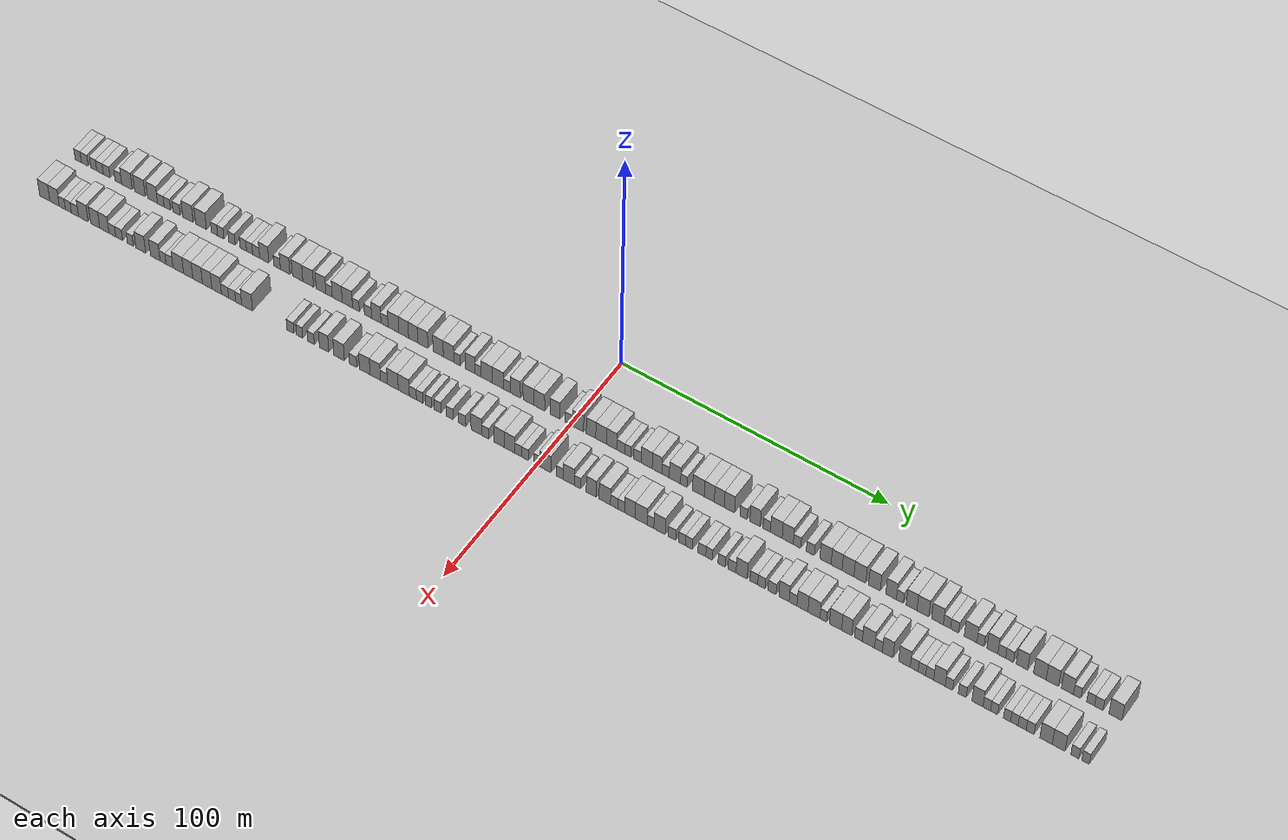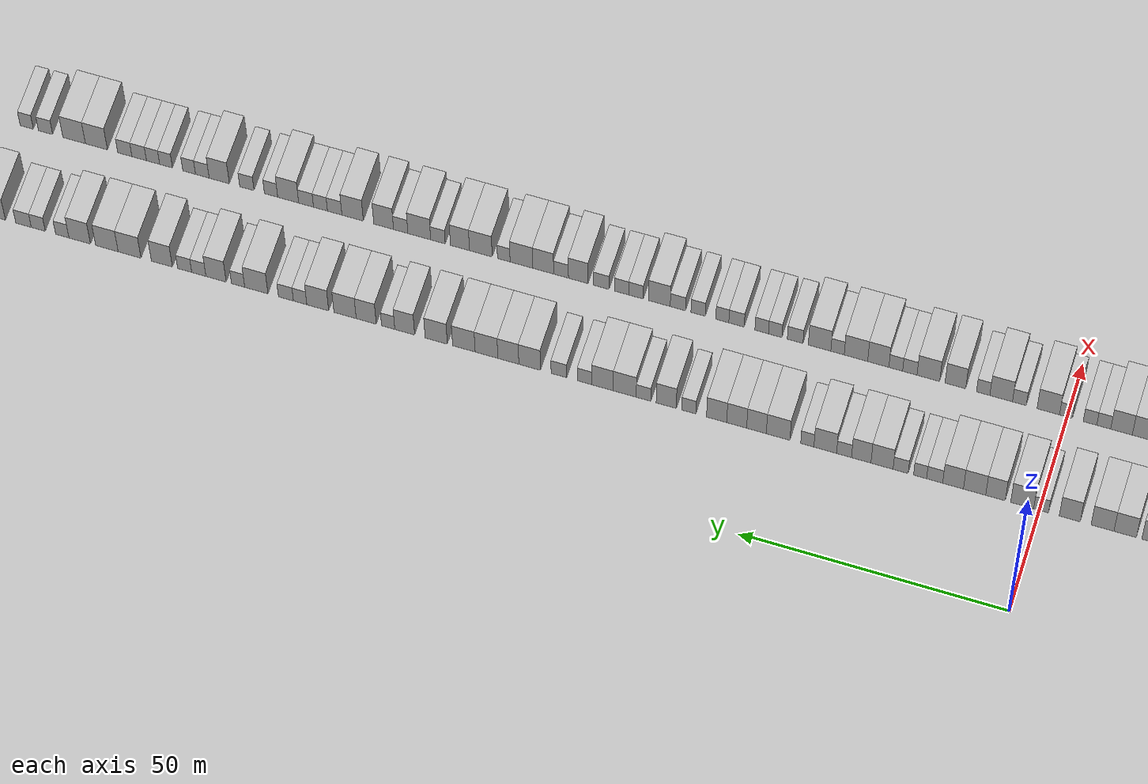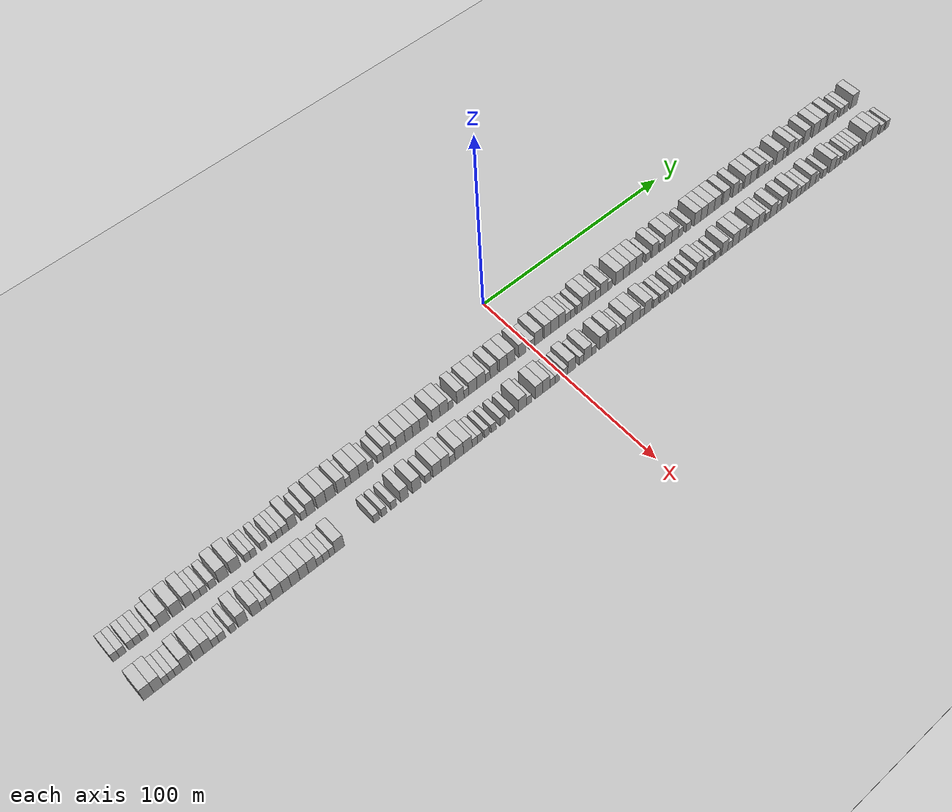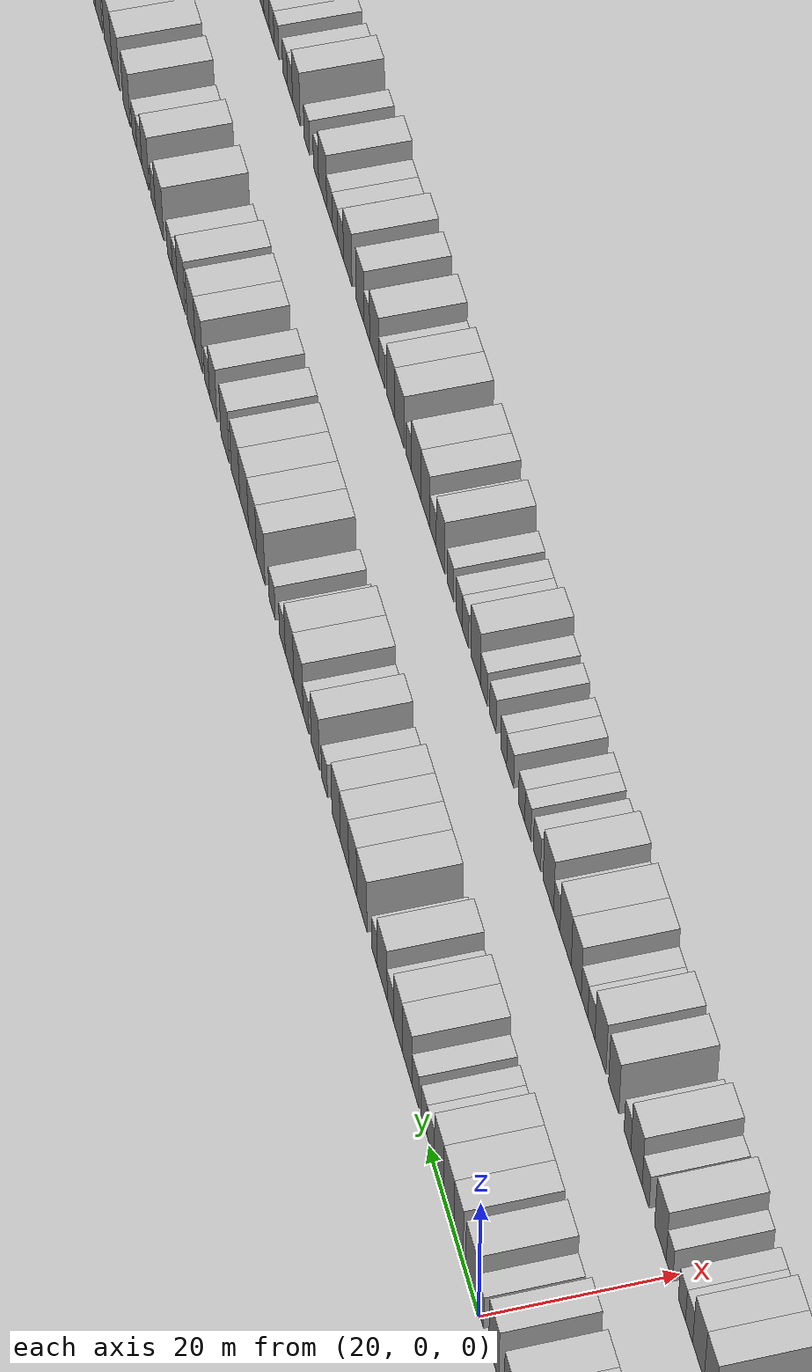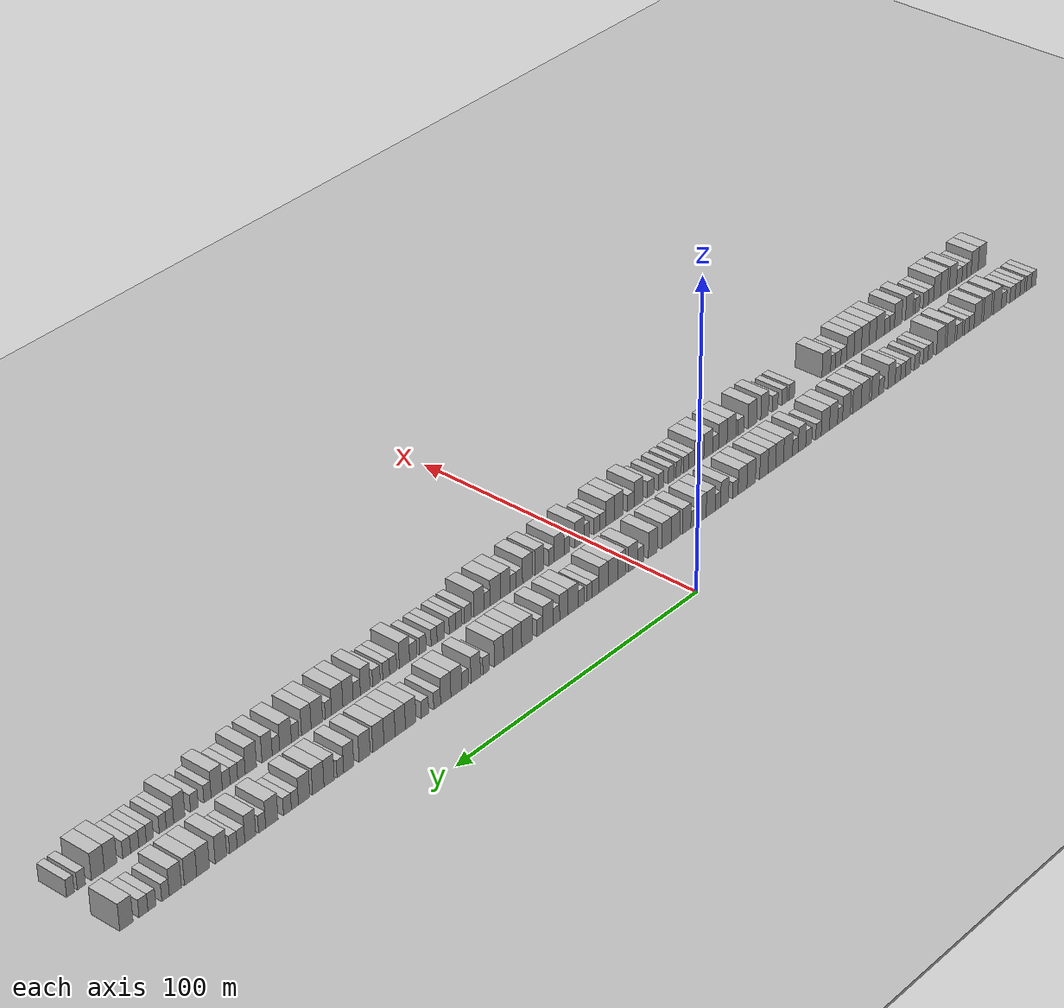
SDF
<?xml version="1.0" encoding="utf-8"?>

<sdf version="1.6">

   <world name="default">

      <gui fullscreen="0">

         <camera name="user_camera">

            <pose>-15 0 4.57585 0 0 0</pose>

            <view_controller>orbit</view_controller>

         </camera>

      </gui>

      <scene>

         <sky>

           <clouds>

             <speed>12</speed>

           </clouds>

         </sky>

         <ambient>0.4 0.4 0.4 1</ambient>

         <background>0.7 0.7 0.7 1</background>

         <shadows>1</shadows>

      </scene>

      <gravity>0 0 -9.8066</gravity>

      <magnetic_field>6e-06 2.3e-05 -4.2e-05</magnetic_field>

      <physics default="0" name="default_physics" type="ode">

         <ode>

            <solver>

               <type>quick</type>

               <iters>10</iters>

               <sor>1.0</sor>

               <use_dynamic_moi_rescaling>0</use_dynamic_moi_rescaling>

            </solver>

            <constraints>

               <cfm>0</cfm>

               <erp>0.2</erp>

               <contact_max_correcting_vel>100</contact_max_correcting_vel>

               <contact_surface_layer>0.001</contact_surface_layer>

            </constraints>

         </ode>

         <max_step_size>0.004</max_step_size>

         <real_time_factor>1</real_time_factor>

         <real_time_update_rate>250</real_time_update_rate>

      </physics>

      <light name="sun" type="directional">

         <cast_shadows>1</cast_shadows>

         <pose>0 0 10 0 0 0</pose>

         <diffuse>0.8 0.8 0.8 1</diffuse>

         <specular>0.2 0.2 0.2 1</specular>

         <attenuation>

            <range>1000</range>

            <constant>0.9</constant>

            <linear>0.01</linear>

            <quadratic>0.001</quadratic>

         </attenuation>

         <direction>-0.5 0.1 -0.9</direction>

      </light>

      <include>

         <name>ground_plane_1</name>

         <uri>model://HANNAS_ground_plane</uri>

         <pose>0 0 0  0 0 0</pose>

      </include>

      <include>

         <name>ground_plane_2</name>

         <uri>model://HANNAS_ground_plane</uri>

         <pose>100 0 0  0 0 0</pose>

      </include>

      <model name="building_1">

         <static>1</static>

         <pose frame="">25.0000 -196.6671 0 0.000000 0.000000 0.000000</pose>

         <link name="link">

            <pose frame="">0 0 3.00 0 0 0</pose>

            <collision name="collision">

               <geometry>

                  <box>

                     <size>10.0000 2.6657 6.0000</size>

                  </box>

               </geometry>

               <max_contacts>10</max_contacts>

               <surface>

                  <contact>

                     <ode/>

                  </contact>

                  <bounce/>

                  <friction>

                     <torsional>

                        <ode/>

                     </torsional>

                     <ode/>

                  </friction>

               </surface>

            </collision>

            <visual name="visual">

               <cast_shadows>0</cast_shadows>

               <geometry>

                  <box>

                     <size>10.0000 2.6657 6.0000</size>

                  </box>

               </geometry>

               <material>

                  <script>

                     <uri>model://HANNAS_wall/materials/scripts</uri>

                     <uri>model://HANNAS_wall/materials/textures</uri>

                     <name>vrc/HANNAS_wall</name>

                  </script>

               </material>

            </visual>

            <self_collide>0</self_collide>

            <enable_wind>0</enable_wind>

            <kinematic>0</kinematic>

         </link>

      </model>

      <model name="building_2">

         <static>1</static>

         <pose frame="">25.0000 -193.9017 0 0.000000 0.000000 0.000000</pose>

         <link name="link">

            <pose frame="">0 0 3.00 0 0 0</pose>

            <collision name="collision">

               <geometry>

                  <box>

                     <size>10.0000 2.8653 6.0000</size>

                  </box>

               </geometry>

               <max_contacts>10</max_contacts>

               <surface>

                  <contact>

                     <ode/>

                  </contact>

                  <bounce/>

                  <friction>

                     <torsional>

                        <ode/>

                     </torsional>

                     <ode/>

                  </friction>

               </surface>

            </collision>

            <visual name="visual">

               <cast_shadows>0</cast_shadows>

               <geometry>

                  <box>

                     <size>10.0000 2.8653 6.0000</size>

                  </box>

               </geometry>

               <material>

                  <script>

                     <uri>model://HANNAS_wall/materials/scripts</uri>

                     <uri>model://HANNAS_wall/materials/textures</uri>

                     <name>vrc/HANNAS_wall</name>

                  </script>

               </material>

            </visual>

            <self_collide>0</self_collide>

            <enable_wind>0</enable_wind>

            <kinematic>0</kinematic>

         </link>

      </model>

      <model name="building_3">

         <static>1</static>

         <pose frame="">25.0000 -190.1941 0 0.000000 0.000000 0.000000</pose>

         <link name="link">

            <pose frame="">0 0 3.00 0 0 0</pose>

            <collision name="collision">

               <geometry>

                  <box>

                     <size>10.0000 2.5499 6.0000</size>

                  </box>

               </geometry>

               <max_contacts>10</max_contacts>

               <surface>

                  <contact>

                     <ode/>

                  </contact>

                  <bounce/>

                  <friction>

                     <torsional>

                        <ode/>

                     </torsional>

                     <ode/>

                  </friction>

               </surface>

            </collision>

            <visual name="visual">

               <cast_shadows>0</cast_shadows>

               <geometry>

                  <box>

                     <size>10.0000 2.5499 6.0000</size>

                  </box>

               </geometry>

               <material>

                  <script>

                     <uri>model://HANNAS_wall/materials/scripts</uri>

                     <uri>model://HANNAS_wall/materials/textures</uri>

                     <name>vrc/HANNAS_wall</name>

                  </script>

               </material>

            </visual>

            <self_collide>0</self_collide>

            <enable_wind>0</enable_wind>

            <kinematic>0</kinematic>

         </link>

      </model>

      <model name="building_4">

         <static>1</static>

         <pose frame="">25.0000 -187.5583 0 0.000000 0.000000 0.000000</pose>

         <link name="link">

            <pose frame="">0 0 3.00 0 0 0</pose>

            <collision name="collision">

               <geometry>

                  <box>

                     <size>10.0000 2.7217 6.0000</size>

                  </box>

               </geometry>

               <max_contacts>10</max_contacts>

               <surface>

                  <contact>

                     <ode/>

                  </contact>

                  <bounce/>

                  <friction>

                     <torsional>

                        <ode/>

                     </torsional>

                     <ode/>

                  </friction>

               </surface>

            </collision>

            <visual name="visual">

               <cast_shadows>0</cast_shadows>

               <geometry>

                  <box>

                     <size>10.0000 2.7217 6.0000</size>

                  </box>

               </geometry>

               <material>

                  <script>

                     <uri>model://HANNAS_wall/materials/scripts</uri>

                     <uri>model://HANNAS_wall/materials/textures</uri>

                     <name>vrc/HANNAS_wall</name>

                  </script>

               </material>

            </visual>

            <self_collide>0</self_collide>

            <enable_wind>0</enable_wind>

            <kinematic>0</kinematic>

         </link>

      </model>

      <model name="building_5">

         <static>1</static>

         <pose frame="">25.0000 -184.7569 0 0.000000 0.000000 0.000000</pose>

         <link name="link">

            <pose frame="">0 0 3.00 0 0 0</pose>

            <collision name="collision">

               <geometry>

                  <box>

                     <size>10.0000 2.8812 6.0000</size>

                  </box>

               </geometry>

               <max_contacts>10</max_contacts>

               <surface>

                  <contact>

                     <ode/>

                  </contact>

                  <bounce/>

                  <friction>

                     <torsional>

                        <ode/>

                     </torsional>

                     <ode/>

                  </friction>

               </surface>

            </collision>

            <visual name="visual">

               <cast_shadows>0</cast_shadows>

               <geometry>

                  <box>

                     <size>10.0000 2.8812 6.0000</size>

                  </box>

               </geometry>

               <material>

                  <script>

                     <uri>model://HANNAS_wall/materials/scripts</uri>

                     <uri>model://HANNAS_wall/materials/textures</uri>

                     <name>vrc/HANNAS_wall</name>

                  </script>

               </material>

            </visual>

            <self_collide>0</self_collide>

            <enable_wind>0</enable_wind>

            <kinematic>0</kinematic>

         </link>

      </model>

      <model name="building_6">

         <static>1</static>

         <pose frame="">25.0000 -179.9197 0 0.000000 0.000000 0.000000</pose>

         <link name="link">

            <pose frame="">0 0 3.00 0 0 0</pose>

            <collision name="collision">

               <geometry>

                  <box>

                     <size>10.0000 2.7931 6.0000</size>

                  </box>

               </geometry>

               <max_contacts>10</max_contacts>

               <surface>

                  <contact>

                     <ode/>

                  </contact>

                  <bounce/>

                  <friction>

                     <torsional>

                        <ode/>

                     </torsional>

                     <ode/>

                  </friction>

               </surface>

            </collision>

            <visual name="visual">

               <cast_shadows>0</cast_shadows>

               <geometry>

                  <box>

                     <size>10.0000 2.7931 6.0000</size>

                  </box>

               </geometry>

               <material>

                  <script>

                     <uri>model://HANNAS_wall/materials/scripts</uri>

                     <uri>model://HANNAS_wall/materials/textures</uri>

                     <name>vrc/HANNAS_wall</name>

                  </script>

               </material>

            </visual>

            <self_collide>0</self_collide>

            <enable_wind>0</enable_wind>

            <kinematic>0</kinematic>

         </link>

      </model>

      <model name="building_7">

         <static>1</static>

         <pose frame="">25.0000 -176.3036 0 0.000000 0.000000 0.000000</pose>

         <link name="link">

            <pose frame="">0 0 4.50 0 0 0</pose>

            <collision name="collision">

               <geometry>

                  <box>

                     <size>10.0000 4.4391 9.0000</size>

                  </box>

               </geometry>

               <max_contacts>10</max_contacts>

               <surface>

                  <contact>

                     <ode/>

                  </contact>

                  <bounce/>

                  <friction>

                     <torsional>

                        <ode/>

                     </torsional>

                     <ode/>

                  </friction>

               </surface>

            </collision>

            <visual name="visual">

               <cast_shadows>0</cast_shadows>

               <geometry>

                  <box>

                     <size>10.0000 4.4391 9.0000</size>

                  </box>

               </geometry>

               <material>

                  <script>

                     <uri>model://HANNAS_wall/materials/scripts</uri>

                     <uri>model://HANNAS_wall/materials/textures</uri>

                     <name>vrc/HANNAS_wall</name>

                  </script>

               </material>

            </visual>

            <self_collide>0</self_collide>

            <enable_wind>0</enable_wind>

            <kinematic>0</kinematic>

         </link>

      </model>

      <model name="building_8">

         <static>1</static>

         <pose frame="">25.0000 -170.8901 0 0.000000 0.000000 0.000000</pose>

         <link name="link">

            <pose frame="">0 0 4.50 0 0 0</pose>

            <collision name="collision">

               <geometry>

                  <box>

                     <size>10.0000 4.3879 9.0000</size>

                  </box>

               </geometry>

               <max_contacts>10</max_contacts>

               <surface>

                  <contact>

                     <ode/>

                  </contact>

                  <bounce/>

                  <friction>

                     <torsional>

                        <ode/>

                     </torsional>

                     <ode/>

                  </friction>

               </surface>

            </collision>

            <visual name="visual">

               <cast_shadows>0</cast_shadows>

               <geometry>

                  <box>

                     <size>10.0000 4.3879 9.0000</size>

                  </box>

               </geometry>

               <material>

                  <script>

                     <uri>model://HANNAS_wall/materials/scripts</uri>

                     <uri>model://HANNAS_wall/materials/textures</uri>

                     <name>vrc/HANNAS_wall</name>

                  </script>

               </material>

            </visual>

            <self_collide>0</self_collide>

            <enable_wind>0</enable_wind>

            <kinematic>0</kinematic>

         </link>

      </model>

      <model name="building_9">

         <static>1</static>

         <pose frame="">25.0000 -165.6503 0 0.000000 0.000000 0.000000</pose>

         <link name="link">

            <pose frame="">0 0 4.50 0 0 0</pose>

            <collision name="collision">

               <geometry>

                  <box>

                     <size>10.0000 4.0917 9.0000</size>

                  </box>

               </geometry>

               <max_contacts>10</max_contacts>

               <surface>

                  <contact>

                     <ode/>

                  </contact>

                  <bounce/>

                  <friction>

                     <torsional>

                        <ode/>

                     </torsional>

                     <ode/>

                  </friction>

               </surface>

            </collision>

            <visual name="visual">

               <cast_shadows>0</cast_shadows>

               <geometry>

                  <box>

                     <size>10.0000 4.0917 9.0000</size>

                  </box>

               </geometry>

               <material>

                  <script>

                     <uri>model://HANNAS_wall/materials/scripts</uri>

                     <uri>model://HANNAS_wall/materials/textures</uri>

                     <name>vrc/HANNAS_wall</name>

                  </script>

               </material>

            </visual>

            <self_collide>0</self_collide>

            <enable_wind>0</enable_wind>

            <kinematic>0</kinematic>

         </link>

      </model>

      <model name="building_10">

         <static>1</static>

         <pose frame="">25.0000 -162.2498 0 0.000000 0.000000 0.000000</pose>

         <link name="link">

            <pose frame="">0 0 3.00 0 0 0</pose>

            <collision name="collision">

               <geometry>

                  <box>

                     <size>10.0000 2.7093 6.0000</size>

                  </box>

               </geometry>

               <max_contacts>10</max_contacts>

               <surface>

                  <contact>

                     <ode/>

                  </contact>

                  <bounce/>

                  <friction>

                     <torsional>

                        <ode/>

                     </torsional>

                     <ode/>

                  </friction>

               </surface>

            </collision>

            <visual name="visual">

               <cast_shadows>0</cast_shadows>

               <geometry>

                  <box>

                     <size>10.0000 2.7093 6.0000</size>

                  </box>

               </geometry>

               <material>

                  <script>

                     <uri>model://HANNAS_wall/materials/scripts</uri>

                     <uri>model://HANNAS_wall/materials/textures</uri>

                     <name>vrc/HANNAS_wall</name>

                  </script>

               </material>

            </visual>

            <self_collide>0</self_collide>

            <enable_wind>0</enable_wind>

            <kinematic>0</kinematic>

         </link>

      </model>

      <model name="building_11">

         <static>1</static>

         <pose frame="">25.0000 -159.5529 0 0.000000 0.000000 0.000000</pose>

         <link name="link">

            <pose frame="">0 0 3.00 0 0 0</pose>

            <collision name="collision">

               <geometry>

                  <box>

                     <size>10.0000 2.6846 6.0000</size>

                  </box>

               </geometry>

               <max_contacts>10</max_contacts>

               <surface>

                  <contact>

                     <ode/>

                  </contact>

                  <bounce/>

                  <friction>

                     <torsional>

                        <ode/>

                     </torsional>

                     <ode/>

                  </friction>

               </surface>

            </collision>

            <visual name="visual">

               <cast_shadows>0</cast_shadows>

               <geometry>

                  <box>

                     <size>10.0000 2.6846 6.0000</size>

                  </box>

               </geometry>

               <material>

                  <script>

                     <uri>model://HANNAS_wall/materials/scripts</uri>

                     <uri>model://HANNAS_wall/materials/textures</uri>

                     <name>vrc/HANNAS_wall</name>

                  </script>

               </material>

            </visual>

            <self_collide>0</self_collide>

            <enable_wind>0</enable_wind>

            <kinematic>0</kinematic>

         </link>

      </model>

      <model name="building_12">

         <static>1</static>

         <pose frame="">25.0000 -155.7123 0 0.000000 0.000000 0.000000</pose>

         <link name="link">

            <pose frame="">0 0 3.00 0 0 0</pose>

            <collision name="collision">

               <geometry>

                  <box>

                     <size>10.0000 2.9966 6.0000</size>

                  </box>

               </geometry>

               <max_contacts>10</max_contacts>

               <surface>

                  <contact>

                     <ode/>

                  </contact>

                  <bounce/>

                  <friction>

                     <torsional>

                        <ode/>

                     </torsional>

                     <ode/>

                  </friction>

               </surface>

            </collision>

            <visual name="visual">

               <cast_shadows>0</cast_shadows>

               <geometry>

                  <box>

                     <size>10.0000 2.9966 6.0000</size>

                  </box>

               </geometry>

               <material>

                  <script>

                     <uri>model://HANNAS_wall/materials/scripts</uri>

                     <uri>model://HANNAS_wall/materials/textures</uri>

                     <name>vrc/HANNAS_wall</name>

                  </script>

               </material>

            </visual>

            <self_collide>0</self_collide>

            <enable_wind>0</enable_wind>

            <kinematic>0</kinematic>

         </link>

      </model>

      <model name="building_13">

         <static>1</static>

         <pose frame="">25.0000 -151.0611 0 0.000000 0.000000 0.000000</pose>

         <link name="link">

            <pose frame="">0 0 4.50 0 0 0</pose>

            <collision name="collision">

               <geometry>

                  <box>

                     <size>10.0000 4.3059 9.0000</size>

                  </box>

               </geometry>

               <max_contacts>10</max_contacts>

               <surface>

                  <contact>

                     <ode/>

                  </contact>

                  <bounce/>

                  <friction>

                     <torsional>

                        <ode/>

                     </torsional>

                     <ode/>

                  </friction>

               </surface>

            </collision>

            <visual name="visual">

               <cast_shadows>0</cast_shadows>

               <geometry>

                  <box>

                     <size>10.0000 4.3059 9.0000</size>

                  </box>

               </geometry>

               <material>

                  <script>

                     <uri>model://HANNAS_wall/materials/scripts</uri>

                     <uri>model://HANNAS_wall/materials/textures</uri>

                     <name>vrc/HANNAS_wall</name>

                  </script>

               </material>

            </visual>

            <self_collide>0</self_collide>

            <enable_wind>0</enable_wind>

            <kinematic>0</kinematic>

         </link>

      </model>

      <model name="building_14">

         <static>1</static>

         <pose frame="">25.0000 -145.6856 0 0.000000 0.000000 0.000000</pose>

         <link name="link">

            <pose frame="">0 0 4.50 0 0 0</pose>

            <collision name="collision">

               <geometry>

                  <box>

                     <size>10.0000 4.4451 9.0000</size>

                  </box>

               </geometry>

               <max_contacts>10</max_contacts>

               <surface>

                  <contact>

                     <ode/>

                  </contact>

                  <bounce/>

                  <friction>

                     <torsional>

                        <ode/>

                     </torsional>

                     <ode/>

                  </friction>

               </surface>

            </collision>

            <visual name="visual">

               <cast_shadows>0</cast_shadows>

               <geometry>

                  <box>

                     <size>10.0000 4.4451 9.0000</size>

                  </box>

               </geometry>

               <material>

                  <script>

                     <uri>model://HANNAS_wall/materials/scripts</uri>

                     <uri>model://HANNAS_wall/materials/textures</uri>

                     <name>vrc/HANNAS_wall</name>

                  </script>

               </material>

            </visual>

            <self_collide>0</self_collide>

            <enable_wind>0</enable_wind>

            <kinematic>0</kinematic>

         </link>

      </model>

      <model name="building_15">

         <static>1</static>

         <pose frame="">25.0000 -140.1893 0 0.000000 0.000000 0.000000</pose>

         <link name="link">

            <pose frame="">0 0 3.00 0 0 0</pose>

            <collision name="collision">

               <geometry>

                  <box>

                     <size>10.0000 2.5474 6.0000</size>

                  </box>

               </geometry>

               <max_contacts>10</max_contacts>

               <surface>

                  <contact>

                     <ode/>

                  </contact>

                  <bounce/>

                  <friction>

                     <torsional>

                        <ode/>

                     </torsional>

                     <ode/>

                  </friction>

               </surface>

            </collision>

            <visual name="visual">

               <cast_shadows>0</cast_shadows>

               <geometry>

                  <box>

                     <size>10.0000 2.5474 6.0000</size>

                  </box>

               </geometry>

               <material>

                  <script>

                     <uri>model://HANNAS_wall/materials/scripts</uri>

                     <uri>model://HANNAS_wall/materials/textures</uri>

                     <name>vrc/HANNAS_wall</name>

                  </script>

               </material>

            </visual>

            <self_collide>0</self_collide>

            <enable_wind>0</enable_wind>

            <kinematic>0</kinematic>

         </link>

      </model>

      <model name="building_16">

         <static>1</static>

         <pose frame="">25.0000 -137.6492 0 0.000000 0.000000 0.000000</pose>

         <link name="link">

            <pose frame="">0 0 3.00 0 0 0</pose>

            <collision name="collision">

               <geometry>

                  <box>

                     <size>10.0000 2.5328 6.0000</size>

                  </box>

               </geometry>

               <max_contacts>10</max_contacts>

               <surface>

                  <contact>

                     <ode/>

                  </contact>

                  <bounce/>

                  <friction>

                     <torsional>

                        <ode/>

                     </torsional>

                     <ode/>

                  </friction>

               </surface>

            </collision>

            <visual name="visual">

               <cast_shadows>0</cast_shadows>

               <geometry>

                  <box>

                     <size>10.0000 2.5328 6.0000</size>

                  </box>

               </geometry>

               <material>

                  <script>

                     <uri>model://HANNAS_wall/materials/scripts</uri>

                     <uri>model://HANNAS_wall/materials/textures</uri>

                     <name>vrc/HANNAS_wall</name>

                  </script>

               </material>

            </visual>

            <self_collide>0</self_collide>

            <enable_wind>0</enable_wind>

            <kinematic>0</kinematic>

         </link>

      </model>

      <model name="building_17">

         <static>1</static>

         <pose frame="">25.0000 -133.0643 0 0.000000 0.000000 0.000000</pose>

         <link name="link">

            <pose frame="">0 0 3.00 0 0 0</pose>

            <collision name="collision">

               <geometry>

                  <box>

                     <size>10.0000 2.6369 6.0000</size>

                  </box>

               </geometry>

               <max_contacts>10</max_contacts>

               <surface>

                  <contact>

                     <ode/>

                  </contact>

                  <bounce/>

                  <friction>

                     <torsional>

                        <ode/>

                     </torsional>

                     <ode/>

                  </friction>

               </surface>

            </collision>

            <visual name="visual">

               <cast_shadows>0</cast_shadows>

               <geometry>

                  <box>

                     <size>10.0000 2.6369 6.0000</size>

                  </box>

               </geometry>

               <material>

                  <script>

                     <uri>model://HANNAS_wall/materials/scripts</uri>

                     <uri>model://HANNAS_wall/materials/textures</uri>

                     <name>vrc/HANNAS_wall</name>

                  </script>

               </material>

            </visual>

            <self_collide>0</self_collide>

            <enable_wind>0</enable_wind>

            <kinematic>0</kinematic>

         </link>

      </model>

      <model name="building_18">

         <static>1</static>

         <pose frame="">25.0000 -128.4281 0 0.000000 0.000000 0.000000</pose>

         <link name="link">

            <pose frame="">0 0 3.00 0 0 0</pose>

            <collision name="collision">

               <geometry>

                  <box>

                     <size>10.0000 2.6356 6.0000</size>

                  </box>

               </geometry>

               <max_contacts>10</max_contacts>

               <surface>

                  <contact>

                     <ode/>

                  </contact>

                  <bounce/>

                  <friction>

                     <torsional>

                        <ode/>

                     </torsional>

                     <ode/>

                  </friction>

               </surface>

            </collision>

            <visual name="visual">

               <cast_shadows>0</cast_shadows>

               <geometry>

                  <box>

                     <size>10.0000 2.6356 6.0000</size>

                  </box>

               </geometry>

               <material>

                  <script>

                     <uri>model://HANNAS_wall/materials/scripts</uri>

                     <uri>model://HANNAS_wall/materials/textures</uri>

                     <name>vrc/HANNAS_wall</name>

                  </script>

               </material>

            </visual>

            <self_collide>0</self_collide>

            <enable_wind>0</enable_wind>

            <kinematic>0</kinematic>

         </link>

      </model>

      <model name="building_19">

         <static>1</static>

         <pose frame="">25.0000 -125.8815 0 0.000000 0.000000 0.000000</pose>

         <link name="link">

            <pose frame="">0 0 3.00 0 0 0</pose>

            <collision name="collision">

               <geometry>

                  <box>

                     <size>10.0000 2.4576 6.0000</size>

                  </box>

               </geometry>

               <max_contacts>10</max_contacts>

               <surface>

                  <contact>

                     <ode/>

                  </contact>

                  <bounce/>

                  <friction>

                     <torsional>

                        <ode/>

                     </torsional>

                     <ode/>

                  </friction>

               </surface>

            </collision>

            <visual name="visual">

               <cast_shadows>0</cast_shadows>

               <geometry>

                  <box>

                     <size>10.0000 2.4576 6.0000</size>

                  </box>

               </geometry>

               <material>

                  <script>

                     <uri>model://HANNAS_wall/materials/scripts</uri>

                     <uri>model://HANNAS_wall/materials/textures</uri>

                     <name>vrc/HANNAS_wall</name>

                  </script>

               </material>

            </visual>

            <self_collide>0</self_collide>

            <enable_wind>0</enable_wind>

            <kinematic>0</kinematic>

         </link>

      </model>

      <model name="building_20">

         <static>1</static>

         <pose frame="">25.0000 -123.2328 0 0.000000 0.000000 0.000000</pose>

         <link name="link">

            <pose frame="">0 0 3.00 0 0 0</pose>

            <collision name="collision">

               <geometry>

                  <box>

                     <size>10.0000 2.8397 6.0000</size>

                  </box>

               </geometry>

               <max_contacts>10</max_contacts>

               <surface>

                  <contact>

                     <ode/>

                  </contact>

                  <bounce/>

                  <friction>

                     <torsional>

                        <ode/>

                     </torsional>

                     <ode/>

                  </friction>

               </surface>

            </collision>

            <visual name="visual">

               <cast_shadows>0</cast_shadows>

               <geometry>

                  <box>

                     <size>10.0000 2.8397 6.0000</size>

                  </box>

               </geometry>

               <material>

                  <script>

                     <uri>model://HANNAS_wall/materials/scripts</uri>

                     <uri>model://HANNAS_wall/materials/textures</uri>

                     <name>vrc/HANNAS_wall</name>

                  </script>

               </material>

            </visual>

            <self_collide>0</self_collide>

            <enable_wind>0</enable_wind>

            <kinematic>0</kinematic>

         </link>

      </model>

      <model name="building_21">

         <static>1</static>

         <pose frame="">25.0000 -119.9275 0 0.000000 0.000000 0.000000</pose>

         <link name="link">

            <pose frame="">0 0 4.50 0 0 0</pose>

            <collision name="collision">

               <geometry>

                  <box>

                     <size>10.0000 3.7709 9.0000</size>

                  </box>

               </geometry>

               <max_contacts>10</max_contacts>

               <surface>

                  <contact>

                     <ode/>

                  </contact>

                  <bounce/>

                  <friction>

                     <torsional>

                        <ode/>

                     </torsional>

                     <ode/>

                  </friction>

               </surface>

            </collision>

            <visual name="visual">

               <cast_shadows>0</cast_shadows>

               <geometry>

                  <box>

                     <size>10.0000 3.7709 9.0000</size>

                  </box>

               </geometry>

               <material>

                  <script>

                     <uri>model://HANNAS_wall/materials/scripts</uri>

                     <uri>model://HANNAS_wall/materials/textures</uri>

                     <name>vrc/HANNAS_wall</name>

                  </script>

               </material>

            </visual>

            <self_collide>0</self_collide>

            <enable_wind>0</enable_wind>

            <kinematic>0</kinematic>

         </link>

      </model>

      <model name="building_22">

         <static>1</static>

         <pose frame="">25.0000 -114.7271 0 0.000000 0.000000 0.000000</pose>

         <link name="link">

            <pose frame="">0 0 3.00 0 0 0</pose>

            <collision name="collision">

               <geometry>

                  <box>

                     <size>10.0000 2.6299 6.0000</size>

                  </box>

               </geometry>

               <max_contacts>10</max_contacts>

               <surface>

                  <contact>

                     <ode/>

                  </contact>

                  <bounce/>

                  <friction>

                     <torsional>

                        <ode/>

                     </torsional>

                     <ode/>

                  </friction>

               </surface>

            </collision>

            <visual name="visual">

               <cast_shadows>0</cast_shadows>

               <geometry>

                  <box>

                     <size>10.0000 2.6299 6.0000</size>

                  </box>

               </geometry>

               <material>

                  <script>

                     <uri>model://HANNAS_wall/materials/scripts</uri>

                     <uri>model://HANNAS_wall/materials/textures</uri>

                     <name>vrc/HANNAS_wall</name>

                  </script>

               </material>

            </visual>

            <self_collide>0</self_collide>

            <enable_wind>0</enable_wind>

            <kinematic>0</kinematic>

         </link>

      </model>

      <model name="building_23">

         <static>1</static>

         <pose frame="">25.0000 -111.5015 0 0.000000 0.000000 0.000000</pose>

         <link name="link">

            <pose frame="">0 0 4.50 0 0 0</pose>

            <collision name="collision">

               <geometry>

                  <box>

                     <size>10.0000 3.8214 9.0000</size>

                  </box>

               </geometry>

               <max_contacts>10</max_contacts>

               <surface>

                  <contact>

                     <ode/>

                  </contact>

                  <bounce/>

                  <friction>

                     <torsional>

                        <ode/>

                     </torsional>

                     <ode/>

                  </friction>

               </surface>

            </collision>

            <visual name="visual">

               <cast_shadows>0</cast_shadows>

               <geometry>

                  <box>

                     <size>10.0000 3.8214 9.0000</size>

                  </box>

               </geometry>

               <material>

                  <script>

                     <uri>model://HANNAS_wall/materials/scripts</uri>

                     <uri>model://HANNAS_wall/materials/textures</uri>

                     <name>vrc/HANNAS_wall</name>

                  </script>

               </material>

            </visual>

            <self_collide>0</self_collide>

            <enable_wind>0</enable_wind>

            <kinematic>0</kinematic>

         </link>

      </model>

      <model name="building_24">

         <static>1</static>

         <pose frame="">25.0000 -106.4917 0 0.000000 0.000000 0.000000</pose>

         <link name="link">

            <pose frame="">0 0 4.50 0 0 0</pose>

            <collision name="collision">

               <geometry>

                  <box>

                     <size>10.0000 4.1983 9.0000</size>

                  </box>

               </geometry>

               <max_contacts>10</max_contacts>

               <surface>

                  <contact>

                     <ode/>

                  </contact>

                  <bounce/>

                  <friction>

                     <torsional>

                        <ode/>

                     </torsional>

                     <ode/>

                  </friction>

               </surface>

            </collision>

            <visual name="visual">

               <cast_shadows>0</cast_shadows>

               <geometry>

                  <box>

                     <size>10.0000 4.1983 9.0000</size>

                  </box>

               </geometry>

               <material>

                  <script>

                     <uri>model://HANNAS_wall/materials/scripts</uri>

                     <uri>model://HANNAS_wall/materials/textures</uri>

                     <name>vrc/HANNAS_wall</name>

                  </script>

               </material>

            </visual>

            <self_collide>0</self_collide>

            <enable_wind>0</enable_wind>

            <kinematic>0</kinematic>

         </link>

      </model>

      <model name="building_25">

         <static>1</static>

         <pose frame="">25.0000 -102.2147 0 0.000000 0.000000 0.000000</pose>

         <link name="link">

            <pose frame="">0 0 4.50 0 0 0</pose>

            <collision name="collision">

               <geometry>

                  <box>

                     <size>10.0000 4.3557 9.0000</size>

                  </box>

               </geometry>

               <max_contacts>10</max_contacts>

               <surface>

                  <contact>

                     <ode/>

                  </contact>

                  <bounce/>

                  <friction>

                     <torsional>

                        <ode/>

                     </torsional>

                     <ode/>

                  </friction>

               </surface>

            </collision>

            <visual name="visual">

               <cast_shadows>0</cast_shadows>

               <geometry>

                  <box>

                     <size>10.0000 4.3557 9.0000</size>

                  </box>

               </geometry>

               <material>

                  <script>

                     <uri>model://HANNAS_wall/materials/scripts</uri>

                     <uri>model://HANNAS_wall/materials/textures</uri>

                     <name>vrc/HANNAS_wall</name>

                  </script>

               </material>

            </visual>

            <self_collide>0</self_collide>

            <enable_wind>0</enable_wind>

            <kinematic>0</kinematic>

         </link>

      </model>

      <model name="building_26">

         <static>1</static>

         <pose frame="">25.0000 -97.0716 0 0.000000 0.000000 0.000000</pose>

         <link name="link">

            <pose frame="">0 0 4.50 0 0 0</pose>

            <collision name="collision">

               <geometry>

                  <box>

                     <size>10.0000 3.9305 9.0000</size>

                  </box>

               </geometry>

               <max_contacts>10</max_contacts>

               <surface>

                  <contact>

                     <ode/>

                  </contact>

                  <bounce/>

                  <friction>

                     <torsional>

                        <ode/>

                     </torsional>

                     <ode/>

                  </friction>

               </surface>

            </collision>

            <visual name="visual">

               <cast_shadows>0</cast_shadows>

               <geometry>

                  <box>

                     <size>10.0000 3.9305 9.0000</size>

                  </box>

               </geometry>

               <material>

                  <script>

                     <uri>model://HANNAS_wall/materials/scripts</uri>

                     <uri>model://HANNAS_wall/materials/textures</uri>

                     <name>vrc/HANNAS_wall</name>

                  </script>

               </material>

            </visual>

            <self_collide>0</self_collide>

            <enable_wind>0</enable_wind>

            <kinematic>0</kinematic>

         </link>

      </model>

      <model name="building_27">

         <static>1</static>

         <pose frame="">25.0000 -93.8565 0 0.000000 0.000000 0.000000</pose>

         <link name="link">

            <pose frame="">0 0 3.00 0 0 0</pose>

            <collision name="collision">

               <geometry>

                  <box>

                     <size>10.0000 2.4998 6.0000</size>

                  </box>

               </geometry>

               <max_contacts>10</max_contacts>

               <surface>

                  <contact>

                     <ode/>

                  </contact>

                  <bounce/>

                  <friction>

                     <torsional>

                        <ode/>

                     </torsional>

                     <ode/>

                  </friction>

               </surface>

            </collision>

            <visual name="visual">

               <cast_shadows>0</cast_shadows>

               <geometry>

                  <box>

                     <size>10.0000 2.4998 6.0000</size>

                  </box>

               </geometry>

               <material>

                  <script>

                     <uri>model://HANNAS_wall/materials/scripts</uri>

                     <uri>model://HANNAS_wall/materials/textures</uri>

                     <name>vrc/HANNAS_wall</name>

                  </script>

               </material>

            </visual>

            <self_collide>0</self_collide>

            <enable_wind>0</enable_wind>

            <kinematic>0</kinematic>

         </link>

      </model>

      <model name="building_28">

         <static>1</static>

         <pose frame="">25.0000 -90.5941 0 0.000000 0.000000 0.000000</pose>

         <link name="link">

            <pose frame="">0 0 4.50 0 0 0</pose>

            <collision name="collision">

               <geometry>

                  <box>

                     <size>10.0000 4.0250 9.0000</size>

                  </box>

               </geometry>

               <max_contacts>10</max_contacts>

               <surface>

                  <contact>

                     <ode/>

                  </contact>

                  <bounce/>

                  <friction>

                     <torsional>

                        <ode/>

                     </torsional>

                     <ode/>

                  </friction>

               </surface>

            </collision>

            <visual name="visual">

               <cast_shadows>0</cast_shadows>

               <geometry>

                  <box>

                     <size>10.0000 4.0250 9.0000</size>

                  </box>

               </geometry>

               <material>

                  <script>

                     <uri>model://HANNAS_wall/materials/scripts</uri>

                     <uri>model://HANNAS_wall/materials/textures</uri>

                     <name>vrc/HANNAS_wall</name>

                  </script>

               </material>

            </visual>

            <self_collide>0</self_collide>

            <enable_wind>0</enable_wind>

            <kinematic>0</kinematic>

         </link>

      </model>

      <model name="building_29">

         <static>1</static>

         <pose frame="">25.0000 -86.5436 0 0.000000 0.000000 0.000000</pose>

         <link name="link">

            <pose frame="">0 0 4.50 0 0 0</pose>

            <collision name="collision">

               <geometry>

                  <box>

                     <size>10.0000 4.0760 9.0000</size>

                  </box>

               </geometry>

               <max_contacts>10</max_contacts>

               <surface>

                  <contact>

                     <ode/>

                  </contact>

                  <bounce/>

                  <friction>

                     <torsional>

                        <ode/>

                     </torsional>

                     <ode/>

                  </friction>

               </surface>

            </collision>

            <visual name="visual">

               <cast_shadows>0</cast_shadows>

               <geometry>

                  <box>

                     <size>10.0000 4.0760 9.0000</size>

                  </box>

               </geometry>

               <material>

                  <script>

                     <uri>model://HANNAS_wall/materials/scripts</uri>

                     <uri>model://HANNAS_wall/materials/textures</uri>

                     <name>vrc/HANNAS_wall</name>

                  </script>

               </material>

            </visual>

            <self_collide>0</self_collide>

            <enable_wind>0</enable_wind>

            <kinematic>0</kinematic>

         </link>

      </model>

      <model name="building_30">

         <static>1</static>

         <pose frame="">25.0000 -83.1639 0 0.000000 0.000000 0.000000</pose>

         <link name="link">

            <pose frame="">0 0 3.00 0 0 0</pose>

            <collision name="collision">

               <geometry>

                  <box>

                     <size>10.0000 2.6834 6.0000</size>

                  </box>

               </geometry>

               <max_contacts>10</max_contacts>

               <surface>

                  <contact>

                     <ode/>

                  </contact>

                  <bounce/>

                  <friction>

                     <torsional>

                        <ode/>

                     </torsional>

                     <ode/>

                  </friction>

               </surface>

            </collision>

            <visual name="visual">

               <cast_shadows>0</cast_shadows>

               <geometry>

                  <box>

                     <size>10.0000 2.6834 6.0000</size>

                  </box>

               </geometry>

               <material>

                  <script>

                     <uri>model://HANNAS_wall/materials/scripts</uri>

                     <uri>model://HANNAS_wall/materials/textures</uri>

                     <name>vrc/HANNAS_wall</name>

                  </script>

               </material>

            </visual>

            <self_collide>0</self_collide>

            <enable_wind>0</enable_wind>

            <kinematic>0</kinematic>

         </link>

      </model>

      <model name="building_31">

         <static>1</static>

         <pose frame="">25.0000 -78.3630 0 0.000000 0.000000 0.000000</pose>

         <link name="link">

            <pose frame="">0 0 3.00 0 0 0</pose>

            <collision name="collision">

               <geometry>

                  <box>

                     <size>10.0000 2.9185 6.0000</size>

                  </box>

               </geometry>

               <max_contacts>10</max_contacts>

               <surface>

                  <contact>

                     <ode/>

                  </contact>

                  <bounce/>

                  <friction>

                     <torsional>

                        <ode/>

                     </torsional>

                     <ode/>

                  </friction>

               </surface>

            </collision>

            <visual name="visual">

               <cast_shadows>0</cast_shadows>

               <geometry>

                  <box>

                     <size>10.0000 2.9185 6.0000</size>

                  </box>

               </geometry>

               <material>

                  <script>

                     <uri>model://HANNAS_wall/materials/scripts</uri>

                     <uri>model://HANNAS_wall/materials/textures</uri>

                     <name>vrc/HANNAS_wall</name>

                  </script>

               </material>

            </visual>

            <self_collide>0</self_collide>

            <enable_wind>0</enable_wind>

            <kinematic>0</kinematic>

         </link>

      </model>

      <model name="building_32">

         <static>1</static>

         <pose frame="">25.0000 -75.0674 0 0.000000 0.000000 0.000000</pose>

         <link name="link">

            <pose frame="">0 0 4.50 0 0 0</pose>

            <collision name="collision">

               <geometry>

                  <box>

                     <size>10.0000 3.6728 9.0000</size>

                  </box>

               </geometry>

               <max_contacts>10</max_contacts>

               <surface>

                  <contact>

                     <ode/>

                  </contact>

                  <bounce/>

                  <friction>

                     <torsional>

                        <ode/>

                     </torsional>

                     <ode/>

                  </friction>

               </surface>

            </collision>

            <visual name="visual">

               <cast_shadows>0</cast_shadows>

               <geometry>

                  <box>

                     <size>10.0000 3.6728 9.0000</size>

                  </box>

               </geometry>

               <material>

                  <script>

                     <uri>model://HANNAS_wall/materials/scripts</uri>

                     <uri>model://HANNAS_wall/materials/textures</uri>

                     <name>vrc/HANNAS_wall</name>

                  </script>

               </material>

            </visual>

            <self_collide>0</self_collide>

            <enable_wind>0</enable_wind>

            <kinematic>0</kinematic>

         </link>

      </model>

      <model name="building_33">

         <static>1</static>

         <pose frame="">25.0000 -71.8355 0 0.000000 0.000000 0.000000</pose>

         <link name="link">

            <pose frame="">0 0 3.00 0 0 0</pose>

            <collision name="collision">

               <geometry>

                  <box>

                     <size>10.0000 2.7911 6.0000</size>

                  </box>

               </geometry>

               <max_contacts>10</max_contacts>

               <surface>

                  <contact>

                     <ode/>

                  </contact>

                  <bounce/>

                  <friction>

                     <torsional>

                        <ode/>

                     </torsional>

                     <ode/>

                  </friction>

               </surface>

            </collision>

            <visual name="visual">

               <cast_shadows>0</cast_shadows>

               <geometry>

                  <box>

                     <size>10.0000 2.7911 6.0000</size>

                  </box>

               </geometry>

               <material>

                  <script>

                     <uri>model://HANNAS_wall/materials/scripts</uri>

                     <uri>model://HANNAS_wall/materials/textures</uri>

                     <name>vrc/HANNAS_wall</name>

                  </script>

               </material>

            </visual>

            <self_collide>0</self_collide>

            <enable_wind>0</enable_wind>

            <kinematic>0</kinematic>

         </link>

      </model>

      <model name="building_34">

         <static>1</static>

         <pose frame="">25.0000 -68.3022 0 0.000000 0.000000 0.000000</pose>

         <link name="link">

            <pose frame="">0 0 4.50 0 0 0</pose>

            <collision name="collision">

               <geometry>

                  <box>

                     <size>10.0000 4.2754 9.0000</size>

                  </box>

               </geometry>

               <max_contacts>10</max_contacts>

               <surface>

                  <contact>

                     <ode/>

                  </contact>

                  <bounce/>

                  <friction>

                     <torsional>

                        <ode/>

                     </torsional>

                     <ode/>

                  </friction>

               </surface>

            </collision>

            <visual name="visual">

               <cast_shadows>0</cast_shadows>

               <geometry>

                  <box>

                     <size>10.0000 4.2754 9.0000</size>

                  </box>

               </geometry>

               <material>

                  <script>

                     <uri>model://HANNAS_wall/materials/scripts</uri>

                     <uri>model://HANNAS_wall/materials/textures</uri>

                     <name>vrc/HANNAS_wall</name>

                  </script>

               </material>

            </visual>

            <self_collide>0</self_collide>

            <enable_wind>0</enable_wind>

            <kinematic>0</kinematic>

         </link>

      </model>

      <model name="building_35">

         <static>1</static>

         <pose frame="">25.0000 -64.2594 0 0.000000 0.000000 0.000000</pose>

         <link name="link">

            <pose frame="">0 0 4.50 0 0 0</pose>

            <collision name="collision">

               <geometry>

                  <box>

                     <size>10.0000 3.8101 9.0000</size>

                  </box>

               </geometry>

               <max_contacts>10</max_contacts>

               <surface>

                  <contact>

                     <ode/>

                  </contact>

                  <bounce/>

                  <friction>

                     <torsional>

                        <ode/>

                     </torsional>

                     <ode/>

                  </friction>

               </surface>

            </collision>

            <visual name="visual">

               <cast_shadows>0</cast_shadows>

               <geometry>

                  <box>

                     <size>10.0000 3.8101 9.0000</size>

                  </box>

               </geometry>

               <material>

                  <script>

                     <uri>model://HANNAS_wall/materials/scripts</uri>

                     <uri>model://HANNAS_wall/materials/textures</uri>

                     <name>vrc/HANNAS_wall</name>

                  </script>

               </material>

            </visual>

            <self_collide>0</self_collide>

            <enable_wind>0</enable_wind>

            <kinematic>0</kinematic>

         </link>

      </model>

      <model name="building_36">

         <static>1</static>

         <pose frame="">25.0000 -60.5467 0 0.000000 0.000000 0.000000</pose>

         <link name="link">

            <pose frame="">0 0 4.50 0 0 0</pose>

            <collision name="collision">

               <geometry>

                  <box>

                     <size>10.0000 3.6154 9.0000</size>

                  </box>

               </geometry>

               <max_contacts>10</max_contacts>

               <surface>

                  <contact>

                     <ode/>

                  </contact>

                  <bounce/>

                  <friction>

                     <torsional>

                        <ode/>

                     </torsional>

                     <ode/>

                  </friction>

               </surface>

            </collision>

            <visual name="visual">

               <cast_shadows>0</cast_shadows>

               <geometry>

                  <box>

                     <size>10.0000 3.6154 9.0000</size>

                  </box>

               </geometry>

               <material>

                  <script>

                     <uri>model://HANNAS_wall/materials/scripts</uri>

                     <uri>model://HANNAS_wall/materials/textures</uri>

                     <name>vrc/HANNAS_wall</name>

                  </script>

               </material>

            </visual>

            <self_collide>0</self_collide>

            <enable_wind>0</enable_wind>

            <kinematic>0</kinematic>

         </link>

      </model>

      <model name="building_37">

         <static>1</static>

         <pose frame="">25.0000 -56.7231 0 0.000000 0.000000 0.000000</pose>

         <link name="link">

            <pose frame="">0 0 4.50 0 0 0</pose>

            <collision name="collision">

               <geometry>

                  <box>

                     <size>10.0000 4.0318 9.0000</size>

                  </box>

               </geometry>

               <max_contacts>10</max_contacts>

               <surface>

                  <contact>

                     <ode/>

                  </contact>

                  <bounce/>

                  <friction>

                     <torsional>

                        <ode/>

                     </torsional>

                     <ode/>

                  </friction>

               </surface>

            </collision>

            <visual name="visual">

               <cast_shadows>0</cast_shadows>

               <geometry>

                  <box>

                     <size>10.0000 4.0318 9.0000</size>

                  </box>

               </geometry>

               <material>

                  <script>

                     <uri>model://HANNAS_wall/materials/scripts</uri>

                     <uri>model://HANNAS_wall/materials/textures</uri>

                     <name>vrc/HANNAS_wall</name>

                  </script>

               </material>

            </visual>

            <self_collide>0</self_collide>

            <enable_wind>0</enable_wind>

            <kinematic>0</kinematic>

         </link>

      </model>

      <model name="building_38">

         <static>1</static>

         <pose frame="">25.0000 -50.7087 0 0.000000 0.000000 0.000000</pose>

         <link name="link">

            <pose frame="">0 0 4.50 0 0 0</pose>

            <collision name="collision">

               <geometry>

                  <box>

                     <size>10.0000 3.9969 9.0000</size>

                  </box>

               </geometry>

               <max_contacts>10</max_contacts>

               <surface>

                  <contact>

                     <ode/>

                  </contact>

                  <bounce/>

                  <friction>

                     <torsional>

                        <ode/>

                     </torsional>

                     <ode/>

                  </friction>

               </surface>

            </collision>

            <visual name="visual">

               <cast_shadows>0</cast_shadows>

               <geometry>

                  <box>

                     <size>10.0000 3.9969 9.0000</size>

                  </box>

               </geometry>

               <material>

                  <script>

                     <uri>model://HANNAS_wall/materials/scripts</uri>

                     <uri>model://HANNAS_wall/materials/textures</uri>

                     <name>vrc/HANNAS_wall</name>

                  </script>

               </material>

            </visual>

            <self_collide>0</self_collide>

            <enable_wind>0</enable_wind>

            <kinematic>0</kinematic>

         </link>

      </model>

      <model name="building_39">

         <static>1</static>

         <pose frame="">25.0000 -46.6285 0 0.000000 0.000000 0.000000</pose>

         <link name="link">

            <pose frame="">0 0 4.50 0 0 0</pose>

            <collision name="collision">

               <geometry>

                  <box>

                     <size>10.0000 4.1634 9.0000</size>

                  </box>

               </geometry>

               <max_contacts>10</max_contacts>

               <surface>

                  <contact>

                     <ode/>

                  </contact>

                  <bounce/>

                  <friction>

                     <torsional>

                        <ode/>

                     </torsional>

                     <ode/>

                  </friction>

               </surface>

            </collision>

            <visual name="visual">

               <cast_shadows>0</cast_shadows>

               <geometry>

                  <box>

                     <size>10.0000 4.1634 9.0000</size>

                  </box>

               </geometry>

               <material>

                  <script>

                     <uri>model://HANNAS_wall/materials/scripts</uri>

                     <uri>model://HANNAS_wall/materials/textures</uri>

                     <name>vrc/HANNAS_wall</name>

                  </script>

               </material>

            </visual>

            <self_collide>0</self_collide>

            <enable_wind>0</enable_wind>

            <kinematic>0</kinematic>

         </link>

      </model>

      <model name="building_40">

         <static>1</static>

         <pose frame="">25.0000 -43.3054 0 0.000000 0.000000 0.000000</pose>

         <link name="link">

            <pose frame="">0 0 3.00 0 0 0</pose>

            <collision name="collision">

               <geometry>

                  <box>

                     <size>10.0000 2.4829 6.0000</size>

                  </box>

               </geometry>

               <max_contacts>10</max_contacts>

               <surface>

                  <contact>

                     <ode/>

                  </contact>

                  <bounce/>

                  <friction>

                     <torsional>

                        <ode/>

                     </torsional>

                     <ode/>

                  </friction>

               </surface>

            </collision>

            <visual name="visual">

               <cast_shadows>0</cast_shadows>

               <geometry>

                  <box>

                     <size>10.0000 2.4829 6.0000</size>

                  </box>

               </geometry>

               <material>

                  <script>

                     <uri>model://HANNAS_wall/materials/scripts</uri>

                     <uri>model://HANNAS_wall/materials/textures</uri>

                     <name>vrc/HANNAS_wall</name>

                  </script>

               </material>

            </visual>

            <self_collide>0</self_collide>

            <enable_wind>0</enable_wind>

            <kinematic>0</kinematic>

         </link>

      </model>

      <model name="building_41">

         <static>1</static>

         <pose frame="">25.0000 -38.2353 0 0.000000 0.000000 0.000000</pose>

         <link name="link">

            <pose frame="">0 0 4.50 0 0 0</pose>

            <collision name="collision">

               <geometry>

                  <box>

                     <size>10.0000 3.6572 9.0000</size>

                  </box>

               </geometry>

               <max_contacts>10</max_contacts>

               <surface>

                  <contact>

                     <ode/>

                  </contact>

                  <bounce/>

                  <friction>

                     <torsional>

                        <ode/>

                     </torsional>

                     <ode/>

                  </friction>

               </surface>

            </collision>

            <visual name="visual">

               <cast_shadows>0</cast_shadows>

               <geometry>

                  <box>

                     <size>10.0000 3.6572 9.0000</size>

                  </box>

               </geometry>

               <material>

                  <script>

                     <uri>model://HANNAS_wall/materials/scripts</uri>

                     <uri>model://HANNAS_wall/materials/textures</uri>

                     <name>vrc/HANNAS_wall</name>

                  </script>

               </material>

            </visual>

            <self_collide>0</self_collide>

            <enable_wind>0</enable_wind>

            <kinematic>0</kinematic>

         </link>

      </model>

      <model name="building_42">

         <static>1</static>

         <pose frame="">25.0000 -35.1828 0 0.000000 0.000000 0.000000</pose>

         <link name="link">

            <pose frame="">0 0 3.00 0 0 0</pose>

            <collision name="collision">

               <geometry>

                  <box>

                     <size>10.0000 2.4476 6.0000</size>

                  </box>

               </geometry>

               <max_contacts>10</max_contacts>

               <surface>

                  <contact>

                     <ode/>

                  </contact>

                  <bounce/>

                  <friction>

                     <torsional>

                        <ode/>

                     </torsional>

                     <ode/>

                  </friction>

               </surface>

            </collision>

            <visual name="visual">

               <cast_shadows>0</cast_shadows>

               <geometry>

                  <box>

                     <size>10.0000 2.4476 6.0000</size>

                  </box>

               </geometry>

               <material>

                  <script>

                     <uri>model://HANNAS_wall/materials/scripts</uri>

                     <uri>model://HANNAS_wall/materials/textures</uri>

                     <name>vrc/HANNAS_wall</name>

                  </script>

               </material>

            </visual>

            <self_collide>0</self_collide>

            <enable_wind>0</enable_wind>

            <kinematic>0</kinematic>

         </link>

      </model>

      <model name="building_43">

         <static>1</static>

         <pose frame="">25.0000 -31.8413 0 0.000000 0.000000 0.000000</pose>

         <link name="link">

            <pose frame="">0 0 4.50 0 0 0</pose>

            <collision name="collision">

               <geometry>

                  <box>

                     <size>10.0000 4.2353 9.0000</size>

                  </box>

               </geometry>

               <max_contacts>10</max_contacts>

               <surface>

                  <contact>

                     <ode/>

                  </contact>

                  <bounce/>

                  <friction>

                     <torsional>

                        <ode/>

                     </torsional>

                     <ode/>

                  </friction>

               </surface>

            </collision>

            <visual name="visual">

               <cast_shadows>0</cast_shadows>

               <geometry>

                  <box>

                     <size>10.0000 4.2353 9.0000</size>

                  </box>

               </geometry>

               <material>

                  <script>

                     <uri>model://HANNAS_wall/materials/scripts</uri>

                     <uri>model://HANNAS_wall/materials/textures</uri>

                     <name>vrc/HANNAS_wall</name>

                  </script>

               </material>

            </visual>

            <self_collide>0</self_collide>

            <enable_wind>0</enable_wind>

            <kinematic>0</kinematic>

         </link>

      </model>

      <model name="building_44">

         <static>1</static>

         <pose frame="">25.0000 -27.4893 0 0.000000 0.000000 0.000000</pose>

         <link name="link">

            <pose frame="">0 0 4.50 0 0 0</pose>

            <collision name="collision">

               <geometry>

                  <box>

                     <size>10.0000 4.4687 9.0000</size>

                  </box>

               </geometry>

               <max_contacts>10</max_contacts>

               <surface>

                  <contact>

                     <ode/>

                  </contact>

                  <bounce/>

                  <friction>

                     <torsional>

                        <ode/>

                     </torsional>

                     <ode/>

                  </friction>

               </surface>

            </collision>

            <visual name="visual">

               <cast_shadows>0</cast_shadows>

               <geometry>

                  <box>

                     <size>10.0000 4.4687 9.0000</size>

                  </box>

               </geometry>

               <material>

                  <script>

                     <uri>model://HANNAS_wall/materials/scripts</uri>

                     <uri>model://HANNAS_wall/materials/textures</uri>

                     <name>vrc/HANNAS_wall</name>

                  </script>

               </material>

            </visual>

            <self_collide>0</self_collide>

            <enable_wind>0</enable_wind>

            <kinematic>0</kinematic>

         </link>

      </model>

      <model name="building_45">

         <static>1</static>

         <pose frame="">25.0000 -23.9686 0 0.000000 0.000000 0.000000</pose>

         <link name="link">

            <pose frame="">0 0 3.00 0 0 0</pose>

            <collision name="collision">

               <geometry>

                  <box>

                     <size>10.0000 2.5726 6.0000</size>

                  </box>

               </geometry>

               <max_contacts>10</max_contacts>

               <surface>

                  <contact>

                     <ode/>

                  </contact>

                  <bounce/>

                  <friction>

                     <torsional>

                        <ode/>

                     </torsional>

                     <ode/>

                  </friction>

               </surface>

            </collision>

            <visual name="visual">

               <cast_shadows>0</cast_shadows>

               <geometry>

                  <box>

                     <size>10.0000 2.5726 6.0000</size>

                  </box>

               </geometry>

               <material>

                  <script>

                     <uri>model://HANNAS_wall/materials/scripts</uri>

                     <uri>model://HANNAS_wall/materials/textures</uri>

                     <name>vrc/HANNAS_wall</name>

                  </script>

               </material>

            </visual>

            <self_collide>0</self_collide>

            <enable_wind>0</enable_wind>

            <kinematic>0</kinematic>

         </link>

      </model>

      <model name="building_46">

         <static>1</static>

         <pose frame="">25.0000 -20.7558 0 0.000000 0.000000 0.000000</pose>

         <link name="link">

            <pose frame="">0 0 4.50 0 0 0</pose>

            <collision name="collision">

               <geometry>

                  <box>

                     <size>10.0000 3.8530 9.0000</size>

                  </box>

               </geometry>

               <max_contacts>10</max_contacts>

               <surface>

                  <contact>

                     <ode/>

                  </contact>

                  <bounce/>

                  <friction>

                     <torsional>

                        <ode/>

                     </torsional>

                     <ode/>

                  </friction>

               </surface>

            </collision>

            <visual name="visual">

               <cast_shadows>0</cast_shadows>

               <geometry>

                  <box>

                     <size>10.0000 3.8530 9.0000</size>

                  </box>

               </geometry>

               <material>

                  <script>

                     <uri>model://HANNAS_wall/materials/scripts</uri>

                     <uri>model://HANNAS_wall/materials/textures</uri>

                     <name>vrc/HANNAS_wall</name>

                  </script>

               </material>

            </visual>

            <self_collide>0</self_collide>

            <enable_wind>0</enable_wind>

            <kinematic>0</kinematic>

         </link>

      </model>

      <model name="building_47">

         <static>1</static>

         <pose frame="">25.0000 -15.7722 0 0.000000 0.000000 0.000000</pose>

         <link name="link">

            <pose frame="">0 0 4.50 0 0 0</pose>

            <collision name="collision">

               <geometry>

                  <box>

                     <size>10.0000 4.1143 9.0000</size>

                  </box>

               </geometry>

               <max_contacts>10</max_contacts>

               <surface>

                  <contact>

                     <ode/>

                  </contact>

                  <bounce/>

                  <friction>

                     <torsional>

                        <ode/>

                     </torsional>

                     <ode/>

                  </friction>

               </surface>

            </collision>

            <visual name="visual">

               <cast_shadows>0</cast_shadows>

               <geometry>

                  <box>

                     <size>10.0000 4.1143 9.0000</size>

                  </box>

               </geometry>

               <material>

                  <script>

                     <uri>model://HANNAS_wall/materials/scripts</uri>

                     <uri>model://HANNAS_wall/materials/textures</uri>

                     <name>vrc/HANNAS_wall</name>

                  </script>

               </material>

            </visual>

            <self_collide>0</self_collide>

            <enable_wind>0</enable_wind>

            <kinematic>0</kinematic>

         </link>

      </model>

      <model name="building_48">

         <static>1</static>

         <pose frame="">25.0000 -11.6120 0 0.000000 0.000000 0.000000</pose>

         <link name="link">

            <pose frame="">0 0 4.50 0 0 0</pose>

            <collision name="collision">

               <geometry>

                  <box>

                     <size>10.0000 4.2062 9.0000</size>

                  </box>

               </geometry>

               <max_contacts>10</max_contacts>

               <surface>

                  <contact>

                     <ode/>

                  </contact>

                  <bounce/>

                  <friction>

                     <torsional>

                        <ode/>

                     </torsional>

                     <ode/>

                  </friction>

               </surface>

            </collision>

            <visual name="visual">

               <cast_shadows>0</cast_shadows>

               <geometry>

                  <box>

                     <size>10.0000 4.2062 9.0000</size>

                  </box>

               </geometry>

               <material>

                  <script>

                     <uri>model://HANNAS_wall/materials/scripts</uri>

                     <uri>model://HANNAS_wall/materials/textures</uri>

                     <name>vrc/HANNAS_wall</name>

                  </script>

               </material>

            </visual>

            <self_collide>0</self_collide>

            <enable_wind>0</enable_wind>

            <kinematic>0</kinematic>

         </link>

      </model>

      <model name="building_49">

         <static>1</static>

         <pose frame="">25.0000 -5.5734 0 0.000000 0.000000 0.000000</pose>

         <link name="link">

            <pose frame="">0 0 4.50 0 0 0</pose>

            <collision name="collision">

               <geometry>

                  <box>

                     <size>10.0000 3.8709 9.0000</size>

                  </box>

               </geometry>

               <max_contacts>10</max_contacts>

               <surface>

                  <contact>

                     <ode/>

                  </contact>

                  <bounce/>

                  <friction>

                     <torsional>

                        <ode/>

                     </torsional>

                     <ode/>

                  </friction>

               </surface>

            </collision>

            <visual name="visual">

               <cast_shadows>0</cast_shadows>

               <geometry>

                  <box>

                     <size>10.0000 3.8709 9.0000</size>

                  </box>

               </geometry>

               <material>

                  <script>

                     <uri>model://HANNAS_wall/materials/scripts</uri>

                     <uri>model://HANNAS_wall/materials/textures</uri>

                     <name>vrc/HANNAS_wall</name>

                  </script>

               </material>

            </visual>

            <self_collide>0</self_collide>

            <enable_wind>0</enable_wind>

            <kinematic>0</kinematic>

         </link>

      </model>

      <model name="building_50">

         <static>1</static>

         <pose frame="">25.0000 -0.2710 0 0.000000 0.000000 0.000000</pose>

         <link name="link">

            <pose frame="">0 0 3.00 0 0 0</pose>

            <collision name="collision">

               <geometry>

                  <box>

                     <size>10.0000 2.7340 6.0000</size>

                  </box>

               </geometry>

               <max_contacts>10</max_contacts>

               <surface>

                  <contact>

                     <ode/>

                  </contact>

                  <bounce/>

                  <friction>

                     <torsional>

                        <ode/>

                     </torsional>

                     <ode/>

                  </friction>

               </surface>

            </collision>

            <visual name="visual">

               <cast_shadows>0</cast_shadows>

               <geometry>

                  <box>

                     <size>10.0000 2.7340 6.0000</size>

                  </box>

               </geometry>

               <material>

                  <script>

                     <uri>model://HANNAS_wall/materials/scripts</uri>

                     <uri>model://HANNAS_wall/materials/textures</uri>

                     <name>vrc/HANNAS_wall</name>

                  </script>

               </material>

            </visual>

            <self_collide>0</self_collide>

            <enable_wind>0</enable_wind>

            <kinematic>0</kinematic>

         </link>

      </model>

      <model name="building_51">

         <static>1</static>

         <pose frame="">25.0000 3.2166 0 0.000000 0.000000 0.000000</pose>

         <link name="link">

            <pose frame="">0 0 4.50 0 0 0</pose>

            <collision name="collision">

               <geometry>

                  <box>

                     <size>10.0000 4.2412 9.0000</size>

                  </box>

               </geometry>

               <max_contacts>10</max_contacts>

               <surface>

                  <contact>

                     <ode/>

                  </contact>

                  <bounce/>

                  <friction>

                     <torsional>

                        <ode/>

                     </torsional>

                     <ode/>

                  </friction>

               </surface>

            </collision>

            <visual name="visual">

               <cast_shadows>0</cast_shadows>

               <geometry>

                  <box>

                     <size>10.0000 4.2412 9.0000</size>

                  </box>

               </geometry>

               <material>

                  <script>

                     <uri>model://HANNAS_wall/materials/scripts</uri>

                     <uri>model://HANNAS_wall/materials/textures</uri>

                     <name>vrc/HANNAS_wall</name>

                  </script>

               </material>

            </visual>

            <self_collide>0</self_collide>

            <enable_wind>0</enable_wind>

            <kinematic>0</kinematic>

         </link>

      </model>

      <model name="building_52">

         <static>1</static>

         <pose frame="">25.0000 8.1420 0 0.000000 0.000000 0.000000</pose>

         <link name="link">

            <pose frame="">0 0 4.50 0 0 0</pose>

            <collision name="collision">

               <geometry>

                  <box>

                     <size>10.0000 3.6095 9.0000</size>

                  </box>

               </geometry>

               <max_contacts>10</max_contacts>

               <surface>

                  <contact>

                     <ode/>

                  </contact>

                  <bounce/>

                  <friction>

                     <torsional>

                        <ode/>

                     </torsional>

                     <ode/>

                  </friction>

               </surface>

            </collision>

            <visual name="visual">

               <cast_shadows>0</cast_shadows>

               <geometry>

                  <box>

                     <size>10.0000 3.6095 9.0000</size>

                  </box>

               </geometry>

               <material>

                  <script>

                     <uri>model://HANNAS_wall/materials/scripts</uri>

                     <uri>model://HANNAS_wall/materials/textures</uri>

                     <name>vrc/HANNAS_wall</name>

                  </script>

               </material>

            </visual>

            <self_collide>0</self_collide>

            <enable_wind>0</enable_wind>

            <kinematic>0</kinematic>

         </link>

      </model>

      <model name="building_53">

         <static>1</static>

         <pose frame="">25.0000 12.0076 0 0.000000 0.000000 0.000000</pose>

         <link name="link">

            <pose frame="">0 0 4.50 0 0 0</pose>

            <collision name="collision">

               <geometry>

                  <box>

                     <size>10.0000 4.1217 9.0000</size>

                  </box>

               </geometry>

               <max_contacts>10</max_contacts>

               <surface>

                  <contact>

                     <ode/>

                  </contact>

                  <bounce/>

                  <friction>

                     <torsional>

                        <ode/>

                     </torsional>

                     <ode/>

                  </friction>

               </surface>

            </collision>

            <visual name="visual">

               <cast_shadows>0</cast_shadows>

               <geometry>

                  <box>

                     <size>10.0000 4.1217 9.0000</size>

                  </box>

               </geometry>

               <material>

                  <script>

                     <uri>model://HANNAS_wall/materials/scripts</uri>

                     <uri>model://HANNAS_wall/materials/textures</uri>

                     <name>vrc/HANNAS_wall</name>

                  </script>

               </material>

            </visual>

            <self_collide>0</self_collide>

            <enable_wind>0</enable_wind>

            <kinematic>0</kinematic>

         </link>

      </model>

      <model name="building_54">

         <static>1</static>

         <pose frame="">25.0000 15.9947 0 0.000000 0.000000 0.000000</pose>

         <link name="link">

            <pose frame="">0 0 4.50 0 0 0</pose>

            <collision name="collision">

               <geometry>

                  <box>

                     <size>10.0000 3.8526 9.0000</size>

                  </box>

               </geometry>

               <max_contacts>10</max_contacts>

               <surface>

                  <contact>

                     <ode/>

                  </contact>

                  <bounce/>

                  <friction>

                     <torsional>

                        <ode/>

                     </torsional>

                     <ode/>

                  </friction>

               </surface>

            </collision>

            <visual name="visual">

               <cast_shadows>0</cast_shadows>

               <geometry>

                  <box>

                     <size>10.0000 3.8526 9.0000</size>

                  </box>

               </geometry>

               <material>

                  <script>

                     <uri>model://HANNAS_wall/materials/scripts</uri>

                     <uri>model://HANNAS_wall/materials/textures</uri>

                     <name>vrc/HANNAS_wall</name>

                  </script>

               </material>

            </visual>

            <self_collide>0</self_collide>

            <enable_wind>0</enable_wind>

            <kinematic>0</kinematic>

         </link>

      </model>

      <model name="building_55">

         <static>1</static>

         <pose frame="">25.0000 19.4131 0 0.000000 0.000000 0.000000</pose>

         <link name="link">

            <pose frame="">0 0 3.00 0 0 0</pose>

            <collision name="collision">

               <geometry>

                  <box>

                     <size>10.0000 2.9841 6.0000</size>

                  </box>

               </geometry>

               <max_contacts>10</max_contacts>

               <surface>

                  <contact>

                     <ode/>

                  </contact>

                  <bounce/>

                  <friction>

                     <torsional>

                        <ode/>

                     </torsional>

                     <ode/>

                  </friction>

               </surface>

            </collision>

            <visual name="visual">

               <cast_shadows>0</cast_shadows>

               <geometry>

                  <box>

                     <size>10.0000 2.9841 6.0000</size>

                  </box>

               </geometry>

               <material>

                  <script>

                     <uri>model://HANNAS_wall/materials/scripts</uri>

                     <uri>model://HANNAS_wall/materials/textures</uri>

                     <name>vrc/HANNAS_wall</name>

                  </script>

               </material>

            </visual>

            <self_collide>0</self_collide>

            <enable_wind>0</enable_wind>

            <kinematic>0</kinematic>

         </link>

      </model>

      <model name="building_56">

         <static>1</static>

         <pose frame="">25.0000 22.1104 0 0.000000 0.000000 0.000000</pose>

         <link name="link">

            <pose frame="">0 0 3.00 0 0 0</pose>

            <collision name="collision">

               <geometry>

                  <box>

                     <size>10.0000 2.4106 6.0000</size>

                  </box>

               </geometry>

               <max_contacts>10</max_contacts>

               <surface>

                  <contact>

                     <ode/>

                  </contact>

                  <bounce/>

                  <friction>

                     <torsional>

                        <ode/>

                     </torsional>

                     <ode/>

                  </friction>

               </surface>

            </collision>

            <visual name="visual">

               <cast_shadows>0</cast_shadows>

               <geometry>

                  <box>

                     <size>10.0000 2.4106 6.0000</size>

                  </box>

               </geometry>

               <material>

                  <script>

                     <uri>model://HANNAS_wall/materials/scripts</uri>

                     <uri>model://HANNAS_wall/materials/textures</uri>

                     <name>vrc/HANNAS_wall</name>

                  </script>

               </material>

            </visual>

            <self_collide>0</self_collide>

            <enable_wind>0</enable_wind>

            <kinematic>0</kinematic>

         </link>

      </model>

      <model name="building_57">

         <static>1</static>

         <pose frame="">25.0000 25.7130 0 0.000000 0.000000 0.000000</pose>

         <link name="link">

            <pose frame="">0 0 3.00 0 0 0</pose>

            <collision name="collision">

               <geometry>

                  <box>

                     <size>10.0000 2.7945 6.0000</size>

                  </box>

               </geometry>

               <max_contacts>10</max_contacts>

               <surface>

                  <contact>

                     <ode/>

                  </contact>

                  <bounce/>

                  <friction>

                     <torsional>

                        <ode/>

                     </torsional>

                     <ode/>

                  </friction>

               </surface>

            </collision>

            <visual name="visual">

               <cast_shadows>0</cast_shadows>

               <geometry>

                  <box>

                     <size>10.0000 2.7945 6.0000</size>

                  </box>

               </geometry>

               <material>

                  <script>

                     <uri>model://HANNAS_wall/materials/scripts</uri>

                     <uri>model://HANNAS_wall/materials/textures</uri>

                     <name>vrc/HANNAS_wall</name>

                  </script>

               </material>

            </visual>

            <self_collide>0</self_collide>

            <enable_wind>0</enable_wind>

            <kinematic>0</kinematic>

         </link>

      </model>

      <model name="building_58">

         <static>1</static>

         <pose frame="">25.0000 29.1658 0 0.000000 0.000000 0.000000</pose>

         <link name="link">

            <pose frame="">0 0 4.50 0 0 0</pose>

            <collision name="collision">

               <geometry>

                  <box>

                     <size>10.0000 4.1110 9.0000</size>

                  </box>

               </geometry>

               <max_contacts>10</max_contacts>

               <surface>

                  <contact>

                     <ode/>

                  </contact>

                  <bounce/>

                  <friction>

                     <torsional>

                        <ode/>

                     </torsional>

                     <ode/>

                  </friction>

               </surface>

            </collision>

            <visual name="visual">

               <cast_shadows>0</cast_shadows>

               <geometry>

                  <box>

                     <size>10.0000 4.1110 9.0000</size>

                  </box>

               </geometry>

               <material>

                  <script>

                     <uri>model://HANNAS_wall/materials/scripts</uri>

                     <uri>model://HANNAS_wall/materials/textures</uri>

                     <name>vrc/HANNAS_wall</name>

                  </script>

               </material>

            </visual>

            <self_collide>0</self_collide>

            <enable_wind>0</enable_wind>

            <kinematic>0</kinematic>

         </link>

      </model>

      <model name="building_59">

         <static>1</static>

         <pose frame="">25.0000 33.0348 0 0.000000 0.000000 0.000000</pose>

         <link name="link">

            <pose frame="">0 0 4.50 0 0 0</pose>

            <collision name="collision">

               <geometry>

                  <box>

                     <size>10.0000 3.6270 9.0000</size>

                  </box>

               </geometry>

               <max_contacts>10</max_contacts>

               <surface>

                  <contact>

                     <ode/>

                  </contact>

                  <bounce/>

                  <friction>

                     <torsional>

                        <ode/>

                     </torsional>

                     <ode/>

                  </friction>

               </surface>

            </collision>

            <visual name="visual">

               <cast_shadows>0</cast_shadows>

               <geometry>

                  <box>

                     <size>10.0000 3.6270 9.0000</size>

                  </box>

               </geometry>

               <material>

                  <script>

                     <uri>model://HANNAS_wall/materials/scripts</uri>

                     <uri>model://HANNAS_wall/materials/textures</uri>

                     <name>vrc/HANNAS_wall</name>

                  </script>

               </material>

            </visual>

            <self_collide>0</self_collide>

            <enable_wind>0</enable_wind>

            <kinematic>0</kinematic>

         </link>

      </model>

      <model name="building_60">

         <static>1</static>

         <pose frame="">25.0000 36.2354 0 0.000000 0.000000 0.000000</pose>

         <link name="link">

            <pose frame="">0 0 3.00 0 0 0</pose>

            <collision name="collision">

               <geometry>

                  <box>

                     <size>10.0000 2.7742 6.0000</size>

                  </box>

               </geometry>

               <max_contacts>10</max_contacts>

               <surface>

                  <contact>

                     <ode/>

                  </contact>

                  <bounce/>

                  <friction>

                     <torsional>

                        <ode/>

                     </torsional>

                     <ode/>

                  </friction>

               </surface>

            </collision>

            <visual name="visual">

               <cast_shadows>0</cast_shadows>

               <geometry>

                  <box>

                     <size>10.0000 2.7742 6.0000</size>

                  </box>

               </geometry>

               <material>

                  <script>

                     <uri>model://HANNAS_wall/materials/scripts</uri>

                     <uri>model://HANNAS_wall/materials/textures</uri>

                     <name>vrc/HANNAS_wall</name>

                  </script>

               </material>

            </visual>

            <self_collide>0</self_collide>

            <enable_wind>0</enable_wind>

            <kinematic>0</kinematic>

         </link>

      </model>

      <model name="building_61">

         <static>1</static>

         <pose frame="">25.0000 39.7331 0 0.000000 0.000000 0.000000</pose>

         <link name="link">

            <pose frame="">0 0 4.50 0 0 0</pose>

            <collision name="collision">

               <geometry>

                  <box>

                     <size>10.0000 4.2213 9.0000</size>

                  </box>

               </geometry>

               <max_contacts>10</max_contacts>

               <surface>

                  <contact>

                     <ode/>

                  </contact>

                  <bounce/>

                  <friction>

                     <torsional>

                        <ode/>

                     </torsional>

                     <ode/>

                  </friction>

               </surface>

            </collision>

            <visual name="visual">

               <cast_shadows>0</cast_shadows>

               <geometry>

                  <box>

                     <size>10.0000 4.2213 9.0000</size>

                  </box>

               </geometry>

               <material>

                  <script>

                     <uri>model://HANNAS_wall/materials/scripts</uri>

                     <uri>model://HANNAS_wall/materials/textures</uri>

                     <name>vrc/HANNAS_wall</name>

                  </script>

               </material>

            </visual>

            <self_collide>0</self_collide>

            <enable_wind>0</enable_wind>

            <kinematic>0</kinematic>

         </link>

      </model>

      <model name="building_62">

         <static>1</static>

         <pose frame="">25.0000 43.0746 0 0.000000 0.000000 0.000000</pose>

         <link name="link">

            <pose frame="">0 0 3.00 0 0 0</pose>

            <collision name="collision">

               <geometry>

                  <box>

                     <size>10.0000 2.4618 6.0000</size>

                  </box>

               </geometry>

               <max_contacts>10</max_contacts>

               <surface>

                  <contact>

                     <ode/>

                  </contact>

                  <bounce/>

                  <friction>

                     <torsional>

                        <ode/>

                     </torsional>

                     <ode/>

                  </friction>

               </surface>

            </collision>

            <visual name="visual">

               <cast_shadows>0</cast_shadows>

               <geometry>

                  <box>

                     <size>10.0000 2.4618 6.0000</size>

                  </box>

               </geometry>

               <material>

                  <script>

                     <uri>model://HANNAS_wall/materials/scripts</uri>

                     <uri>model://HANNAS_wall/materials/textures</uri>

                     <name>vrc/HANNAS_wall</name>

                  </script>

               </material>

            </visual>

            <self_collide>0</self_collide>

            <enable_wind>0</enable_wind>

            <kinematic>0</kinematic>

         </link>

      </model>

      <model name="building_63">

         <static>1</static>

         <pose frame="">25.0000 48.5144 0 0.000000 0.000000 0.000000</pose>

         <link name="link">

            <pose frame="">0 0 4.50 0 0 0</pose>

            <collision name="collision">

               <geometry>

                  <box>

                     <size>10.0000 4.4177 9.0000</size>

                  </box>

               </geometry>

               <max_contacts>10</max_contacts>

               <surface>

                  <contact>

                     <ode/>

                  </contact>

                  <bounce/>

                  <friction>

                     <torsional>

                        <ode/>

                     </torsional>

                     <ode/>

                  </friction>

               </surface>

            </collision>

            <visual name="visual">

               <cast_shadows>0</cast_shadows>

               <geometry>

                  <box>

                     <size>10.0000 4.4177 9.0000</size>

                  </box>

               </geometry>

               <material>

                  <script>

                     <uri>model://HANNAS_wall/materials/scripts</uri>

                     <uri>model://HANNAS_wall/materials/textures</uri>

                     <name>vrc/HANNAS_wall</name>

                  </script>

               </material>

            </visual>

            <self_collide>0</self_collide>

            <enable_wind>0</enable_wind>

            <kinematic>0</kinematic>

         </link>

      </model>

      <model name="building_64">

         <static>1</static>

         <pose frame="">25.0000 52.5567 0 0.000000 0.000000 0.000000</pose>

         <link name="link">

            <pose frame="">0 0 4.50 0 0 0</pose>

            <collision name="collision">

               <geometry>

                  <box>

                     <size>10.0000 3.6669 9.0000</size>

                  </box>

               </geometry>

               <max_contacts>10</max_contacts>

               <surface>

                  <contact>

                     <ode/>

                  </contact>

                  <bounce/>

                  <friction>

                     <torsional>

                        <ode/>

                     </torsional>

                     <ode/>

                  </friction>

               </surface>

            </collision>

            <visual name="visual">

               <cast_shadows>0</cast_shadows>

               <geometry>

                  <box>

                     <size>10.0000 3.6669 9.0000</size>

                  </box>

               </geometry>

               <material>

                  <script>

                     <uri>model://HANNAS_wall/materials/scripts</uri>

                     <uri>model://HANNAS_wall/materials/textures</uri>

                     <name>vrc/HANNAS_wall</name>

                  </script>

               </material>

            </visual>

            <self_collide>0</self_collide>

            <enable_wind>0</enable_wind>

            <kinematic>0</kinematic>

         </link>

      </model>

      <model name="building_65">

         <static>1</static>

         <pose frame="">25.0000 56.2505 0 0.000000 0.000000 0.000000</pose>

         <link name="link">

            <pose frame="">0 0 4.50 0 0 0</pose>

            <collision name="collision">

               <geometry>

                  <box>

                     <size>10.0000 3.7207 9.0000</size>

                  </box>

               </geometry>

               <max_contacts>10</max_contacts>

               <surface>

                  <contact>

                     <ode/>

                  </contact>

                  <bounce/>

                  <friction>

                     <torsional>

                        <ode/>

                     </torsional>

                     <ode/>

                  </friction>

               </surface>

            </collision>

            <visual name="visual">

               <cast_shadows>0</cast_shadows>

               <geometry>

                  <box>

                     <size>10.0000 3.7207 9.0000</size>

                  </box>

               </geometry>

               <material>

                  <script>

                     <uri>model://HANNAS_wall/materials/scripts</uri>

                     <uri>model://HANNAS_wall/materials/textures</uri>

                     <name>vrc/HANNAS_wall</name>

                  </script>

               </material>

            </visual>

            <self_collide>0</self_collide>

            <enable_wind>0</enable_wind>

            <kinematic>0</kinematic>

         </link>

      </model>

      <model name="building_66">

         <static>1</static>

         <pose frame="">25.0000 60.0045 0 0.000000 0.000000 0.000000</pose>

         <link name="link">

            <pose frame="">0 0 4.50 0 0 0</pose>

            <collision name="collision">

               <geometry>

                  <box>

                     <size>10.0000 3.7872 9.0000</size>

                  </box>

               </geometry>

               <max_contacts>10</max_contacts>

               <surface>

                  <contact>

                     <ode/>

                  </contact>

                  <bounce/>

                  <friction>

                     <torsional>

                        <ode/>

                     </torsional>

                     <ode/>

                  </friction>

               </surface>

            </collision>

            <visual name="visual">

               <cast_shadows>0</cast_shadows>

               <geometry>

                  <box>

                     <size>10.0000 3.7872 9.0000</size>

                  </box>

               </geometry>

               <material>

                  <script>

                     <uri>model://HANNAS_wall/materials/scripts</uri>

                     <uri>model://HANNAS_wall/materials/textures</uri>

                     <name>vrc/HANNAS_wall</name>

                  </script>

               </material>

            </visual>

            <self_collide>0</self_collide>

            <enable_wind>0</enable_wind>

            <kinematic>0</kinematic>

         </link>

      </model>

      <model name="building_67">

         <static>1</static>

         <pose frame="">25.0000 65.2268 0 0.000000 0.000000 0.000000</pose>

         <link name="link">

            <pose frame="">0 0 3.00 0 0 0</pose>

            <collision name="collision">

               <geometry>

                  <box>

                     <size>10.0000 2.6575 6.0000</size>

                  </box>

               </geometry>

               <max_contacts>10</max_contacts>

               <surface>

                  <contact>

                     <ode/>

                  </contact>

                  <bounce/>

                  <friction>

                     <torsional>

                        <ode/>

                     </torsional>

                     <ode/>

                  </friction>

               </surface>

            </collision>

            <visual name="visual">

               <cast_shadows>0</cast_shadows>

               <geometry>

                  <box>

                     <size>10.0000 2.6575 6.0000</size>

                  </box>

               </geometry>

               <material>

                  <script>

                     <uri>model://HANNAS_wall/materials/scripts</uri>

                     <uri>model://HANNAS_wall/materials/textures</uri>

                     <name>vrc/HANNAS_wall</name>

                  </script>

               </material>

            </visual>

            <self_collide>0</self_collide>

            <enable_wind>0</enable_wind>

            <kinematic>0</kinematic>

         </link>

      </model>

      <model name="building_68">

         <static>1</static>

         <pose frame="">25.0000 69.4559 0 0.000000 0.000000 0.000000</pose>

         <link name="link">

            <pose frame="">0 0 4.50 0 0 0</pose>

            <collision name="collision">

               <geometry>

                  <box>

                     <size>10.0000 3.8007 9.0000</size>

                  </box>

               </geometry>

               <max_contacts>10</max_contacts>

               <surface>

                  <contact>

                     <ode/>

                  </contact>

                  <bounce/>

                  <friction>

                     <torsional>

                        <ode/>

                     </torsional>

                     <ode/>

                  </friction>

               </surface>

            </collision>

            <visual name="visual">

               <cast_shadows>0</cast_shadows>

               <geometry>

                  <box>

                     <size>10.0000 3.8007 9.0000</size>

                  </box>

               </geometry>

               <material>

                  <script>

                     <uri>model://HANNAS_wall/materials/scripts</uri>

                     <uri>model://HANNAS_wall/materials/textures</uri>

                     <name>vrc/HANNAS_wall</name>

                  </script>

               </material>

            </visual>

            <self_collide>0</self_collide>

            <enable_wind>0</enable_wind>

            <kinematic>0</kinematic>

         </link>

      </model>

      <model name="building_69">

         <static>1</static>

         <pose frame="">25.0000 73.7174 0 0.000000 0.000000 0.000000</pose>

         <link name="link">

            <pose frame="">0 0 3.00 0 0 0</pose>

            <collision name="collision">

               <geometry>

                  <box>

                     <size>10.0000 2.7222 6.0000</size>

                  </box>

               </geometry>

               <max_contacts>10</max_contacts>

               <surface>

                  <contact>

                     <ode/>

                  </contact>

                  <bounce/>

                  <friction>

                     <torsional>

                        <ode/>

                     </torsional>

                     <ode/>

                  </friction>

               </surface>

            </collision>

            <visual name="visual">

               <cast_shadows>0</cast_shadows>

               <geometry>

                  <box>

                     <size>10.0000 2.7222 6.0000</size>

                  </box>

               </geometry>

               <material>

                  <script>

                     <uri>model://HANNAS_wall/materials/scripts</uri>

                     <uri>model://HANNAS_wall/materials/textures</uri>

                     <name>vrc/HANNAS_wall</name>

                  </script>

               </material>

            </visual>

            <self_collide>0</self_collide>

            <enable_wind>0</enable_wind>

            <kinematic>0</kinematic>

         </link>

      </model>

      <model name="building_70">

         <static>1</static>

         <pose frame="">25.0000 77.2315 0 0.000000 0.000000 0.000000</pose>

         <link name="link">

            <pose frame="">0 0 4.50 0 0 0</pose>

            <collision name="collision">

               <geometry>

                  <box>

                     <size>10.0000 4.3060 9.0000</size>

                  </box>

               </geometry>

               <max_contacts>10</max_contacts>

               <surface>

                  <contact>

                     <ode/>

                  </contact>

                  <bounce/>

                  <friction>

                     <torsional>

                        <ode/>

                     </torsional>

                     <ode/>

                  </friction>

               </surface>

            </collision>

            <visual name="visual">

               <cast_shadows>0</cast_shadows>

               <geometry>

                  <box>

                     <size>10.0000 4.3060 9.0000</size>

                  </box>

               </geometry>

               <material>

                  <script>

                     <uri>model://HANNAS_wall/materials/scripts</uri>

                     <uri>model://HANNAS_wall/materials/textures</uri>

                     <name>vrc/HANNAS_wall</name>

                  </script>

               </material>

            </visual>

            <self_collide>0</self_collide>

            <enable_wind>0</enable_wind>

            <kinematic>0</kinematic>

         </link>

      </model>

      <model name="building_71">

         <static>1</static>

         <pose frame="">25.0000 81.4164 0 0.000000 0.000000 0.000000</pose>

         <link name="link">

            <pose frame="">0 0 4.50 0 0 0</pose>

            <collision name="collision">

               <geometry>

                  <box>

                     <size>10.0000 4.0638 9.0000</size>

                  </box>

               </geometry>

               <max_contacts>10</max_contacts>

               <surface>

                  <contact>

                     <ode/>

                  </contact>

                  <bounce/>

                  <friction>

                     <torsional>

                        <ode/>

                     </torsional>

                     <ode/>

                  </friction>

               </surface>

            </collision>

            <visual name="visual">

               <cast_shadows>0</cast_shadows>

               <geometry>

                  <box>

                     <size>10.0000 4.0638 9.0000</size>

                  </box>

               </geometry>

               <material>

                  <script>

                     <uri>model://HANNAS_wall/materials/scripts</uri>

                     <uri>model://HANNAS_wall/materials/textures</uri>

                     <name>vrc/HANNAS_wall</name>

                  </script>

               </material>

            </visual>

            <self_collide>0</self_collide>

            <enable_wind>0</enable_wind>

            <kinematic>0</kinematic>

         </link>

      </model>

      <model name="building_72">

         <static>1</static>

         <pose frame="">25.0000 84.8159 0 0.000000 0.000000 0.000000</pose>

         <link name="link">

            <pose frame="">0 0 3.00 0 0 0</pose>

            <collision name="collision">

               <geometry>

                  <box>

                     <size>10.0000 2.7354 6.0000</size>

                  </box>

               </geometry>

               <max_contacts>10</max_contacts>

               <surface>

                  <contact>

                     <ode/>

                  </contact>

                  <bounce/>

                  <friction>

                     <torsional>

                        <ode/>

                     </torsional>

                     <ode/>

                  </friction>

               </surface>

            </collision>

            <visual name="visual">

               <cast_shadows>0</cast_shadows>

               <geometry>

                  <box>

                     <size>10.0000 2.7354 6.0000</size>

                  </box>

               </geometry>

               <material>

                  <script>

                     <uri>model://HANNAS_wall/materials/scripts</uri>

                     <uri>model://HANNAS_wall/materials/textures</uri>

                     <name>vrc/HANNAS_wall</name>

                  </script>

               </material>

            </visual>

            <self_collide>0</self_collide>

            <enable_wind>0</enable_wind>

            <kinematic>0</kinematic>

         </link>

      </model>

      <model name="building_73">

         <static>1</static>

         <pose frame="">25.0000 89.6539 0 0.000000 0.000000 0.000000</pose>

         <link name="link">

            <pose frame="">0 0 3.00 0 0 0</pose>

            <collision name="collision">

               <geometry>

                  <box>

                     <size>10.0000 2.9406 6.0000</size>

                  </box>

               </geometry>

               <max_contacts>10</max_contacts>

               <surface>

                  <contact>

                     <ode/>

                  </contact>

                  <bounce/>

                  <friction>

                     <torsional>

                        <ode/>

                     </torsional>

                     <ode/>

                  </friction>

               </surface>

            </collision>

            <visual name="visual">

               <cast_shadows>0</cast_shadows>

               <geometry>

                  <box>

                     <size>10.0000 2.9406 6.0000</size>

                  </box>

               </geometry>

               <material>

                  <script>

                     <uri>model://HANNAS_wall/materials/scripts</uri>

                     <uri>model://HANNAS_wall/materials/textures</uri>

                     <name>vrc/HANNAS_wall</name>

                  </script>

               </material>

            </visual>

            <self_collide>0</self_collide>

            <enable_wind>0</enable_wind>

            <kinematic>0</kinematic>

         </link>

      </model>

      <model name="building_74">

         <static>1</static>

         <pose frame="">25.0000 95.1711 0 0.000000 0.000000 0.000000</pose>

         <link name="link">

            <pose frame="">0 0 4.50 0 0 0</pose>

            <collision name="collision">

               <geometry>

                  <box>

                     <size>10.0000 4.0937 9.0000</size>

                  </box>

               </geometry>

               <max_contacts>10</max_contacts>

               <surface>

                  <contact>

                     <ode/>

                  </contact>

                  <bounce/>

                  <friction>

                     <torsional>

                        <ode/>

                     </torsional>

                     <ode/>

                  </friction>

               </surface>

            </collision>

            <visual name="visual">

               <cast_shadows>0</cast_shadows>

               <geometry>

                  <box>

                     <size>10.0000 4.0937 9.0000</size>

                  </box>

               </geometry>

               <material>

                  <script>

                     <uri>model://HANNAS_wall/materials/scripts</uri>

                     <uri>model://HANNAS_wall/materials/textures</uri>

                     <name>vrc/HANNAS_wall</name>

                  </script>

               </material>

            </visual>

            <self_collide>0</self_collide>

            <enable_wind>0</enable_wind>

            <kinematic>0</kinematic>

         </link>

      </model>

      <model name="building_75">

         <static>1</static>

         <pose frame="">25.0000 99.1989 0 0.000000 0.000000 0.000000</pose>

         <link name="link">

            <pose frame="">0 0 4.50 0 0 0</pose>

            <collision name="collision">

               <geometry>

                  <box>

                     <size>10.0000 3.9620 9.0000</size>

                  </box>

               </geometry>

               <max_contacts>10</max_contacts>

               <surface>

                  <contact>

                     <ode/>

                  </contact>

                  <bounce/>

                  <friction>

                     <torsional>

                        <ode/>

                     </torsional>

                     <ode/>

                  </friction>

               </surface>

            </collision>

            <visual name="visual">

               <cast_shadows>0</cast_shadows>

               <geometry>

                  <box>

                     <size>10.0000 3.9620 9.0000</size>

                  </box>

               </geometry>

               <material>

                  <script>

                     <uri>model://HANNAS_wall/materials/scripts</uri>

                     <uri>model://HANNAS_wall/materials/textures</uri>

                     <name>vrc/HANNAS_wall</name>

                  </script>

               </material>

            </visual>

            <self_collide>0</self_collide>

            <enable_wind>0</enable_wind>

            <kinematic>0</kinematic>

         </link>

      </model>

      <model name="building_76">

         <static>1</static>

         <pose frame="">25.0000 103.3308 0 0.000000 0.000000 0.000000</pose>

         <link name="link">

            <pose frame="">0 0 4.50 0 0 0</pose>

            <collision name="collision">

               <geometry>

                  <box>

                     <size>10.0000 4.3018 9.0000</size>

                  </box>

               </geometry>

               <max_contacts>10</max_contacts>

               <surface>

                  <contact>

                     <ode/>

                  </contact>

                  <bounce/>

                  <friction>

                     <torsional>

                        <ode/>

                     </torsional>

                     <ode/>

                  </friction>

               </surface>

            </collision>

            <visual name="visual">

               <cast_shadows>0</cast_shadows>

               <geometry>

                  <box>

                     <size>10.0000 4.3018 9.0000</size>

                  </box>

               </geometry>

               <material>

                  <script>

                     <uri>model://HANNAS_wall/materials/scripts</uri>

                     <uri>model://HANNAS_wall/materials/textures</uri>

                     <name>vrc/HANNAS_wall</name>

                  </script>

               </material>

            </visual>

            <self_collide>0</self_collide>

            <enable_wind>0</enable_wind>

            <kinematic>0</kinematic>

         </link>

      </model>

      <model name="building_77">

         <static>1</static>

         <pose frame="">25.0000 107.6206 0 0.000000 0.000000 0.000000</pose>

         <link name="link">

            <pose frame="">0 0 4.50 0 0 0</pose>

            <collision name="collision">

               <geometry>

                  <box>

                     <size>10.0000 4.2779 9.0000</size>

                  </box>

               </geometry>

               <max_contacts>10</max_contacts>

               <surface>

                  <contact>

                     <ode/>

                  </contact>

                  <bounce/>

                  <friction>

                     <torsional>

                        <ode/>

                     </torsional>

                     <ode/>

                  </friction>

               </surface>

            </collision>

            <visual name="visual">

               <cast_shadows>0</cast_shadows>

               <geometry>

                  <box>

                     <size>10.0000 4.2779 9.0000</size>

                  </box>

               </geometry>

               <material>

                  <script>

                     <uri>model://HANNAS_wall/materials/scripts</uri>

                     <uri>model://HANNAS_wall/materials/textures</uri>

                     <name>vrc/HANNAS_wall</name>

                  </script>

               </material>

            </visual>

            <self_collide>0</self_collide>

            <enable_wind>0</enable_wind>

            <kinematic>0</kinematic>

         </link>

      </model>

      <model name="building_78">

         <static>1</static>

         <pose frame="">25.0000 112.8596 0 0.000000 0.000000 0.000000</pose>

         <link name="link">

            <pose frame="">0 0 4.50 0 0 0</pose>

            <collision name="collision">

               <geometry>

                  <box>

                     <size>10.0000 4.2000 9.0000</size>

                  </box>

               </geometry>

               <max_contacts>10</max_contacts>

               <surface>

                  <contact>

                     <ode/>

                  </contact>

                  <bounce/>

                  <friction>

                     <torsional>

                        <ode/>

                     </torsional>

                     <ode/>

                  </friction>

               </surface>

            </collision>

            <visual name="visual">

               <cast_shadows>0</cast_shadows>

               <geometry>

                  <box>

                     <size>10.0000 4.2000 9.0000</size>

                  </box>

               </geometry>

               <material>

                  <script>

                     <uri>model://HANNAS_wall/materials/scripts</uri>

                     <uri>model://HANNAS_wall/materials/textures</uri>

                     <name>vrc/HANNAS_wall</name>

                  </script>

               </material>

            </visual>

            <self_collide>0</self_collide>

            <enable_wind>0</enable_wind>

            <kinematic>0</kinematic>

         </link>

      </model>

      <model name="building_79">

         <static>1</static>

         <pose frame="">25.0000 118.8472 0 0.000000 0.000000 0.000000</pose>

         <link name="link">

            <pose frame="">0 0 4.50 0 0 0</pose>

            <collision name="collision">

               <geometry>

                  <box>

                     <size>10.0000 3.7751 9.0000</size>

                  </box>

               </geometry>

               <max_contacts>10</max_contacts>

               <surface>

                  <contact>

                     <ode/>

                  </contact>

                  <bounce/>

                  <friction>

                     <torsional>

                        <ode/>

                     </torsional>

                     <ode/>

                  </friction>

               </surface>

            </collision>

            <visual name="visual">

               <cast_shadows>0</cast_shadows>

               <geometry>

                  <box>

                     <size>10.0000 3.7751 9.0000</size>

                  </box>

               </geometry>

               <material>

                  <script>

                     <uri>model://HANNAS_wall/materials/scripts</uri>

                     <uri>model://HANNAS_wall/materials/textures</uri>

                     <name>vrc/HANNAS_wall</name>

                  </script>

               </material>

            </visual>

            <self_collide>0</self_collide>

            <enable_wind>0</enable_wind>

            <kinematic>0</kinematic>

         </link>

      </model>

      <model name="building_80">

         <static>1</static>

         <pose frame="">25.0000 121.9937 0 0.000000 0.000000 0.000000</pose>

         <link name="link">

            <pose frame="">0 0 3.00 0 0 0</pose>

            <collision name="collision">

               <geometry>

                  <box>

                     <size>10.0000 2.5179 6.0000</size>

                  </box>

               </geometry>

               <max_contacts>10</max_contacts>

               <surface>

                  <contact>

                     <ode/>

                  </contact>

                  <bounce/>

                  <friction>

                     <torsional>

                        <ode/>

                     </torsional>

                     <ode/>

                  </friction>

               </surface>

            </collision>

            <visual name="visual">

               <cast_shadows>0</cast_shadows>

               <geometry>

                  <box>

                     <size>10.0000 2.5179 6.0000</size>

                  </box>

               </geometry>

               <material>

                  <script>

                     <uri>model://HANNAS_wall/materials/scripts</uri>

                     <uri>model://HANNAS_wall/materials/textures</uri>

                     <name>vrc/HANNAS_wall</name>

                  </script>

               </material>

            </visual>

            <self_collide>0</self_collide>

            <enable_wind>0</enable_wind>

            <kinematic>0</kinematic>

         </link>

      </model>

      <model name="building_81">

         <static>1</static>

         <pose frame="">25.0000 126.1621 0 0.000000 0.000000 0.000000</pose>

         <link name="link">

            <pose frame="">0 0 4.50 0 0 0</pose>

            <collision name="collision">

               <geometry>

                  <box>

                     <size>10.0000 3.8190 9.0000</size>

                  </box>

               </geometry>

               <max_contacts>10</max_contacts>

               <surface>

                  <contact>

                     <ode/>

                  </contact>

                  <bounce/>

                  <friction>

                     <torsional>

                        <ode/>

                     </torsional>

                     <ode/>

                  </friction>

               </surface>

            </collision>

            <visual name="visual">

               <cast_shadows>0</cast_shadows>

               <geometry>

                  <box>

                     <size>10.0000 3.8190 9.0000</size>

                  </box>

               </geometry>

               <material>

                  <script>

                     <uri>model://HANNAS_wall/materials/scripts</uri>

                     <uri>model://HANNAS_wall/materials/textures</uri>

                     <name>vrc/HANNAS_wall</name>

                  </script>

               </material>

            </visual>

            <self_collide>0</self_collide>

            <enable_wind>0</enable_wind>

            <kinematic>0</kinematic>

         </link>

      </model>

      <model name="building_82">

         <static>1</static>

         <pose frame="">25.0000 130.1893 0 0.000000 0.000000 0.000000</pose>

         <link name="link">

            <pose frame="">0 0 4.50 0 0 0</pose>

            <collision name="collision">

               <geometry>

                  <box>

                     <size>10.0000 4.2354 9.0000</size>

                  </box>

               </geometry>

               <max_contacts>10</max_contacts>

               <surface>

                  <contact>

                     <ode/>

                  </contact>

                  <bounce/>

                  <friction>

                     <torsional>

                        <ode/>

                     </torsional>

                     <ode/>

                  </friction>

               </surface>

            </collision>

            <visual name="visual">

               <cast_shadows>0</cast_shadows>

               <geometry>

                  <box>

                     <size>10.0000 4.2354 9.0000</size>

                  </box>

               </geometry>

               <material>

                  <script>

                     <uri>model://HANNAS_wall/materials/scripts</uri>

                     <uri>model://HANNAS_wall/materials/textures</uri>

                     <name>vrc/HANNAS_wall</name>

                  </script>

               </material>

            </visual>

            <self_collide>0</self_collide>

            <enable_wind>0</enable_wind>

            <kinematic>0</kinematic>

         </link>

      </model>

      <model name="building_83">

         <static>1</static>

         <pose frame="">25.0000 135.3894 0 0.000000 0.000000 0.000000</pose>

         <link name="link">

            <pose frame="">0 0 4.50 0 0 0</pose>

            <collision name="collision">

               <geometry>

                  <box>

                     <size>10.0000 4.1647 9.0000</size>

                  </box>

               </geometry>

               <max_contacts>10</max_contacts>

               <surface>

                  <contact>

                     <ode/>

                  </contact>

                  <bounce/>

                  <friction>

                     <torsional>

                        <ode/>

                     </torsional>

                     <ode/>

                  </friction>

               </surface>

            </collision>

            <visual name="visual">

               <cast_shadows>0</cast_shadows>

               <geometry>

                  <box>

                     <size>10.0000 4.1647 9.0000</size>

                  </box>

               </geometry>

               <material>

                  <script>

                     <uri>model://HANNAS_wall/materials/scripts</uri>

                     <uri>model://HANNAS_wall/materials/textures</uri>

                     <name>vrc/HANNAS_wall</name>

                  </script>

               </material>

            </visual>

            <self_collide>0</self_collide>

            <enable_wind>0</enable_wind>

            <kinematic>0</kinematic>

         </link>

      </model>

      <model name="building_84">

         <static>1</static>

         <pose frame="">25.0000 138.7558 0 0.000000 0.000000 0.000000</pose>

         <link name="link">

            <pose frame="">0 0 3.00 0 0 0</pose>

            <collision name="collision">

               <geometry>

                  <box>

                     <size>10.0000 2.5683 6.0000</size>

                  </box>

               </geometry>

               <max_contacts>10</max_contacts>

               <surface>

                  <contact>

                     <ode/>

                  </contact>

                  <bounce/>

                  <friction>

                     <torsional>

                        <ode/>

                     </torsional>

                     <ode/>

                  </friction>

               </surface>

            </collision>

            <visual name="visual">

               <cast_shadows>0</cast_shadows>

               <geometry>

                  <box>

                     <size>10.0000 2.5683 6.0000</size>

                  </box>

               </geometry>

               <material>

                  <script>

                     <uri>model://HANNAS_wall/materials/scripts</uri>

                     <uri>model://HANNAS_wall/materials/textures</uri>

                     <name>vrc/HANNAS_wall</name>

                  </script>

               </material>

            </visual>

            <self_collide>0</self_collide>

            <enable_wind>0</enable_wind>

            <kinematic>0</kinematic>

         </link>

      </model>

      <model name="building_85">

         <static>1</static>

         <pose frame="">25.0000 141.4679 0 0.000000 0.000000 0.000000</pose>

         <link name="link">

            <pose frame="">0 0 3.00 0 0 0</pose>

            <collision name="collision">

               <geometry>

                  <box>

                     <size>10.0000 2.8558 6.0000</size>

                  </box>

               </geometry>

               <max_contacts>10</max_contacts>

               <surface>

                  <contact>

                     <ode/>

                  </contact>

                  <bounce/>

                  <friction>

                     <torsional>

                        <ode/>

                     </torsional>

                     <ode/>

                  </friction>

               </surface>

            </collision>

            <visual name="visual">

               <cast_shadows>0</cast_shadows>

               <geometry>

                  <box>

                     <size>10.0000 2.8558 6.0000</size>

                  </box>

               </geometry>

               <material>

                  <script>

                     <uri>model://HANNAS_wall/materials/scripts</uri>

                     <uri>model://HANNAS_wall/materials/textures</uri>

                     <name>vrc/HANNAS_wall</name>

                  </script>

               </material>

            </visual>

            <self_collide>0</self_collide>

            <enable_wind>0</enable_wind>

            <kinematic>0</kinematic>

         </link>

      </model>

      <model name="building_86">

         <static>1</static>

         <pose frame="">25.0000 147.1205 0 0.000000 0.000000 0.000000</pose>

         <link name="link">

            <pose frame="">0 0 4.50 0 0 0</pose>

            <collision name="collision">

               <geometry>

                  <box>

                     <size>10.0000 4.4494 9.0000</size>

                  </box>

               </geometry>

               <max_contacts>10</max_contacts>

               <surface>

                  <contact>

                     <ode/>

                  </contact>

                  <bounce/>

                  <friction>

                     <torsional>

                        <ode/>

                     </torsional>

                     <ode/>

                  </friction>

               </surface>

            </collision>

            <visual name="visual">

               <cast_shadows>0</cast_shadows>

               <geometry>

                  <box>

                     <size>10.0000 4.4494 9.0000</size>

                  </box>

               </geometry>

               <material>

                  <script>

                     <uri>model://HANNAS_wall/materials/scripts</uri>

                     <uri>model://HANNAS_wall/materials/textures</uri>

                     <name>vrc/HANNAS_wall</name>

                  </script>

               </material>

            </visual>

            <self_collide>0</self_collide>

            <enable_wind>0</enable_wind>

            <kinematic>0</kinematic>

         </link>

      </model>

      <model name="building_87">

         <static>1</static>

         <pose frame="">25.0000 150.6152 0 0.000000 0.000000 0.000000</pose>

         <link name="link">

            <pose frame="">0 0 3.00 0 0 0</pose>

            <collision name="collision">

               <geometry>

                  <box>

                     <size>10.0000 2.5400 6.0000</size>

                  </box>

               </geometry>

               <max_contacts>10</max_contacts>

               <surface>

                  <contact>

                     <ode/>

                  </contact>

                  <bounce/>

                  <friction>

                     <torsional>

                        <ode/>

                     </torsional>

                     <ode/>

                  </friction>

               </surface>

            </collision>

            <visual name="visual">

               <cast_shadows>0</cast_shadows>

               <geometry>

                  <box>

                     <size>10.0000 2.5400 6.0000</size>

                  </box>

               </geometry>

               <material>

                  <script>

                     <uri>model://HANNAS_wall/materials/scripts</uri>

                     <uri>model://HANNAS_wall/materials/textures</uri>

                     <name>vrc/HANNAS_wall</name>

                  </script>

               </material>

            </visual>

            <self_collide>0</self_collide>

            <enable_wind>0</enable_wind>

            <kinematic>0</kinematic>

         </link>

      </model>

      <model name="building_88">

         <static>1</static>

         <pose frame="">25.0000 154.8274 0 0.000000 0.000000 0.000000</pose>

         <link name="link">

            <pose frame="">0 0 4.50 0 0 0</pose>

            <collision name="collision">

               <geometry>

                  <box>

                     <size>10.0000 3.8843 9.0000</size>

                  </box>

               </geometry>

               <max_contacts>10</max_contacts>

               <surface>

                  <contact>

                     <ode/>

                  </contact>

                  <bounce/>

                  <friction>

                     <torsional>

                        <ode/>

                     </torsional>

                     <ode/>

                  </friction>

               </surface>

            </collision>

            <visual name="visual">

               <cast_shadows>0</cast_shadows>

               <geometry>

                  <box>

                     <size>10.0000 3.8843 9.0000</size>

                  </box>

               </geometry>

               <material>

                  <script>

                     <uri>model://HANNAS_wall/materials/scripts</uri>

                     <uri>model://HANNAS_wall/materials/textures</uri>

                     <name>vrc/HANNAS_wall</name>

                  </script>

               </material>

            </visual>

            <self_collide>0</self_collide>

            <enable_wind>0</enable_wind>

            <kinematic>0</kinematic>

         </link>

      </model>

      <model name="building_89">

         <static>1</static>

         <pose frame="">25.0000 158.1349 0 0.000000 0.000000 0.000000</pose>

         <link name="link">

            <pose frame="">0 0 3.00 0 0 0</pose>

            <collision name="collision">

               <geometry>

                  <box>

                     <size>10.0000 2.7309 6.0000</size>

                  </box>

               </geometry>

               <max_contacts>10</max_contacts>

               <surface>

                  <contact>

                     <ode/>

                  </contact>

                  <bounce/>

                  <friction>

                     <torsional>

                        <ode/>

                     </torsional>

                     <ode/>

                  </friction>

               </surface>

            </collision>

            <visual name="visual">

               <cast_shadows>0</cast_shadows>

               <geometry>

                  <box>

                     <size>10.0000 2.7309 6.0000</size>

                  </box>

               </geometry>

               <material>

                  <script>

                     <uri>model://HANNAS_wall/materials/scripts</uri>

                     <uri>model://HANNAS_wall/materials/textures</uri>

                     <name>vrc/HANNAS_wall</name>

                  </script>

               </material>

            </visual>

            <self_collide>0</self_collide>

            <enable_wind>0</enable_wind>

            <kinematic>0</kinematic>

         </link>

      </model>

      <model name="building_90">

         <static>1</static>

         <pose frame="">25.0000 160.8501 0 0.000000 0.000000 0.000000</pose>

         <link name="link">

            <pose frame="">0 0 3.00 0 0 0</pose>

            <collision name="collision">

               <geometry>

                  <box>

                     <size>10.0000 2.6995 6.0000</size>

                  </box>

               </geometry>

               <max_contacts>10</max_contacts>

               <surface>

                  <contact>

                     <ode/>

                  </contact>

                  <bounce/>

                  <friction>

                     <torsional>

                        <ode/>

                     </torsional>

                     <ode/>

                  </friction>

               </surface>

            </collision>

            <visual name="visual">

               <cast_shadows>0</cast_shadows>

               <geometry>

                  <box>

                     <size>10.0000 2.6995 6.0000</size>

                  </box>

               </geometry>

               <material>

                  <script>

                     <uri>model://HANNAS_wall/materials/scripts</uri>

                     <uri>model://HANNAS_wall/materials/textures</uri>

                     <name>vrc/HANNAS_wall</name>

                  </script>

               </material>

            </visual>

            <self_collide>0</self_collide>

            <enable_wind>0</enable_wind>

            <kinematic>0</kinematic>

         </link>

      </model>

      <model name="building_91">

         <static>1</static>

         <pose frame="">25.0000 165.2189 0 0.000000 0.000000 0.000000</pose>

         <link name="link">

            <pose frame="">0 0 4.50 0 0 0</pose>

            <collision name="collision">

               <geometry>

                  <box>

                     <size>10.0000 4.0380 9.0000</size>

                  </box>

               </geometry>

               <max_contacts>10</max_contacts>

               <surface>

                  <contact>

                     <ode/>

                  </contact>

                  <bounce/>

                  <friction>

                     <torsional>

                        <ode/>

                     </torsional>

                     <ode/>

                  </friction>

               </surface>

            </collision>

            <visual name="visual">

               <cast_shadows>0</cast_shadows>

               <geometry>

                  <box>

                     <size>10.0000 4.0380 9.0000</size>

                  </box>

               </geometry>

               <material>

                  <script>

                     <uri>model://HANNAS_wall/materials/scripts</uri>

                     <uri>model://HANNAS_wall/materials/textures</uri>

                     <name>vrc/HANNAS_wall</name>

                  </script>

               </material>

            </visual>

            <self_collide>0</self_collide>

            <enable_wind>0</enable_wind>

            <kinematic>0</kinematic>

         </link>

      </model>

      <model name="building_92">

         <static>1</static>

         <pose frame="">25.0000 171.4387 0 0.000000 0.000000 0.000000</pose>

         <link name="link">

            <pose frame="">0 0 4.50 0 0 0</pose>

            <collision name="collision">

               <geometry>

                  <box>

                     <size>10.0000 4.4017 9.0000</size>

                  </box>

               </geometry>

               <max_contacts>10</max_contacts>

               <surface>

                  <contact>

                     <ode/>

                  </contact>

                  <bounce/>

                  <friction>

                     <torsional>

                        <ode/>

                     </torsional>

                     <ode/>

                  </friction>

               </surface>

            </collision>

            <visual name="visual">

               <cast_shadows>0</cast_shadows>

               <geometry>

                  <box>

                     <size>10.0000 4.4017 9.0000</size>

                  </box>

               </geometry>

               <material>

                  <script>

                     <uri>model://HANNAS_wall/materials/scripts</uri>

                     <uri>model://HANNAS_wall/materials/textures</uri>

                     <name>vrc/HANNAS_wall</name>

                  </script>

               </material>

            </visual>

            <self_collide>0</self_collide>

            <enable_wind>0</enable_wind>

            <kinematic>0</kinematic>

         </link>

      </model>

      <model name="building_93">

         <static>1</static>

         <pose frame="">25.0000 175.7985 0 0.000000 0.000000 0.000000</pose>

         <link name="link">

            <pose frame="">0 0 4.50 0 0 0</pose>

            <collision name="collision">

               <geometry>

                  <box>

                     <size>10.0000 4.3179 9.0000</size>

                  </box>

               </geometry>

               <max_contacts>10</max_contacts>

               <surface>

                  <contact>

                     <ode/>

                  </contact>

                  <bounce/>

                  <friction>

                     <torsional>

                        <ode/>

                     </torsional>

                     <ode/>

                  </friction>

               </surface>

            </collision>

            <visual name="visual">

               <cast_shadows>0</cast_shadows>

               <geometry>

                  <box>

                     <size>10.0000 4.3179 9.0000</size>

                  </box>

               </geometry>

               <material>

                  <script>

                     <uri>model://HANNAS_wall/materials/scripts</uri>

                     <uri>model://HANNAS_wall/materials/textures</uri>

                     <name>vrc/HANNAS_wall</name>

                  </script>

               </material>

            </visual>

            <self_collide>0</self_collide>

            <enable_wind>0</enable_wind>

            <kinematic>0</kinematic>

         </link>

      </model>

      <model name="building_94">

         <static>1</static>

         <pose frame="">25.0000 181.0391 0 0.000000 0.000000 0.000000</pose>

         <link name="link">

            <pose frame="">0 0 4.50 0 0 0</pose>

            <collision name="collision">

               <geometry>

                  <box>

                     <size>10.0000 4.1634 9.0000</size>

                  </box>

               </geometry>

               <max_contacts>10</max_contacts>

               <surface>

                  <contact>

                     <ode/>

                  </contact>

                  <bounce/>

                  <friction>

                     <torsional>

                        <ode/>

                     </torsional>

                     <ode/>

                  </friction>

               </surface>

            </collision>

            <visual name="visual">

               <cast_shadows>0</cast_shadows>

               <geometry>

                  <box>

                     <size>10.0000 4.1634 9.0000</size>

                  </box>

               </geometry>

               <material>

                  <script>

                     <uri>model://HANNAS_wall/materials/scripts</uri>

                     <uri>model://HANNAS_wall/materials/textures</uri>

                     <name>vrc/HANNAS_wall</name>

                  </script>

               </material>

            </visual>

            <self_collide>0</self_collide>

            <enable_wind>0</enable_wind>

            <kinematic>0</kinematic>

         </link>

      </model>

      <model name="building_95">

         <static>1</static>

         <pose frame="">25.0000 184.4058 0 0.000000 0.000000 0.000000</pose>

         <link name="link">

            <pose frame="">0 0 3.00 0 0 0</pose>

            <collision name="collision">

               <geometry>

                  <box>

                     <size>10.0000 2.5699 6.0000</size>

                  </box>

               </geometry>

               <max_contacts>10</max_contacts>

               <surface>

                  <contact>

                     <ode/>

                  </contact>

                  <bounce/>

                  <friction>

                     <torsional>

                        <ode/>

                     </torsional>

                     <ode/>

                  </friction>

               </surface>

            </collision>

            <visual name="visual">

               <cast_shadows>0</cast_shadows>

               <geometry>

                  <box>

                     <size>10.0000 2.5699 6.0000</size>

                  </box>

               </geometry>

               <material>

                  <script>

                     <uri>model://HANNAS_wall/materials/scripts</uri>

                     <uri>model://HANNAS_wall/materials/textures</uri>

                     <name>vrc/HANNAS_wall</name>

                  </script>

               </material>

            </visual>

            <self_collide>0</self_collide>

            <enable_wind>0</enable_wind>

            <kinematic>0</kinematic>

         </link>

      </model>

      <model name="building_96">

         <static>1</static>

         <pose frame="">25.0000 189.0411 0 0.000000 0.000000 0.000000</pose>

         <link name="link">

            <pose frame="">0 0 3.00 0 0 0</pose>

            <collision name="collision">

               <geometry>

                  <box>

                     <size>10.0000 2.7007 6.0000</size>

                  </box>

               </geometry>

               <max_contacts>10</max_contacts>

               <surface>

                  <contact>

                     <ode/>

                  </contact>

                  <bounce/>

                  <friction>

                     <torsional>

                        <ode/>

                     </torsional>

                     <ode/>

                  </friction>

               </surface>

            </collision>

            <visual name="visual">

               <cast_shadows>0</cast_shadows>

               <geometry>

                  <box>

                     <size>10.0000 2.7007 6.0000</size>

                  </box>

               </geometry>

               <material>

                  <script>

                     <uri>model://HANNAS_wall/materials/scripts</uri>

                     <uri>model://HANNAS_wall/materials/textures</uri>

                     <name>vrc/HANNAS_wall</name>

                  </script>

               </material>

            </visual>

            <self_collide>0</self_collide>

            <enable_wind>0</enable_wind>

            <kinematic>0</kinematic>

         </link>

      </model>

      <model name="building_97">

         <static>1</static>

         <pose frame="">25.0000 191.8899 0 0.000000 0.000000 0.000000</pose>

         <link name="link">

            <pose frame="">0 0 3.00 0 0 0</pose>

            <collision name="collision">

               <geometry>

                  <box>

                     <size>10.0000 2.9970 6.0000</size>

                  </box>

               </geometry>

               <max_contacts>10</max_contacts>

               <surface>

                  <contact>

                     <ode/>

                  </contact>

                  <bounce/>

                  <friction>

                     <torsional>

                        <ode/>

                     </torsional>

                     <ode/>

                  </friction>

               </surface>

            </collision>

            <visual name="visual">

               <cast_shadows>0</cast_shadows>

               <geometry>

                  <box>

                     <size>10.0000 2.9970 6.0000</size>

                  </box>

               </geometry>

               <material>

                  <script>

                     <uri>model://HANNAS_wall/materials/scripts</uri>

                     <uri>model://HANNAS_wall/materials/textures</uri>

                     <name>vrc/HANNAS_wall</name>

                  </script>

               </material>

            </visual>

            <self_collide>0</self_collide>

            <enable_wind>0</enable_wind>

            <kinematic>0</kinematic>

         </link>

      </model>

      <model name="building_98">

         <static>1</static>

         <pose frame="">25.0000 197.6163 0 0.000000 0.000000 0.000000</pose>

         <link name="link">

            <pose frame="">0 0 4.50 0 0 0</pose>

            <collision name="collision">

               <geometry>

                  <box>

                     <size>10.0000 4.4556 9.0000</size>

                  </box>

               </geometry>

               <max_contacts>10</max_contacts>

               <surface>

                  <contact>

                     <ode/>

                  </contact>

                  <bounce/>

                  <friction>

                     <torsional>

                        <ode/>

                     </torsional>

                     <ode/>

                  </friction>

               </surface>

            </collision>

            <visual name="visual">

               <cast_shadows>0</cast_shadows>

               <geometry>

                  <box>

                     <size>10.0000 4.4556 9.0000</size>

                  </box>

               </geometry>

               <material>

                  <script>

                     <uri>model://HANNAS_wall/materials/scripts</uri>

                     <uri>model://HANNAS_wall/materials/textures</uri>

                     <name>vrc/HANNAS_wall</name>

                  </script>

               </material>

            </visual>

            <self_collide>0</self_collide>

            <enable_wind>0</enable_wind>

            <kinematic>0</kinematic>

         </link>

      </model>

      <model name="building_99">

         <static>1</static>

         <pose frame="">44.0000 -195.8763 0 0.000000 0.000000 0.000000</pose>

         <link name="link">

            <pose frame="">0 0 4.50 0 0 0</pose>

            <collision name="collision">

               <geometry>

                  <box>

                     <size>10.0000 4.2473 9.0000</size>

                  </box>

               </geometry>

               <max_contacts>10</max_contacts>

               <surface>

                  <contact>

                     <ode/>

                  </contact>

                  <bounce/>

                  <friction>

                     <torsional>

                        <ode/>

                     </torsional>

                     <ode/>

                  </friction>

               </surface>

            </collision>

            <visual name="visual">

               <cast_shadows>0</cast_shadows>

               <geometry>

                  <box>

                     <size>10.0000 4.2473 9.0000</size>

                  </box>

               </geometry>

               <material>

                  <script>

                     <uri>model://HANNAS_wall/materials/scripts</uri>

                     <uri>model://HANNAS_wall/materials/textures</uri>

                     <name>vrc/HANNAS_wall</name>

                  </script>

               </material>

            </visual>

            <self_collide>0</self_collide>

            <enable_wind>0</enable_wind>

            <kinematic>0</kinematic>

         </link>

      </model>

      <model name="building_100">

         <static>1</static>

         <pose frame="">44.0000 -191.7968 0 0.000000 0.000000 0.000000</pose>

         <link name="link">

            <pose frame="">0 0 4.50 0 0 0</pose>

            <collision name="collision">

               <geometry>

                  <box>

                     <size>10.0000 3.9117 9.0000</size>

                  </box>

               </geometry>

               <max_contacts>10</max_contacts>

               <surface>

                  <contact>

                     <ode/>

                  </contact>

                  <bounce/>

                  <friction>

                     <torsional>

                        <ode/>

                     </torsional>

                     <ode/>

                  </friction>

               </surface>

            </collision>

            <visual name="visual">

               <cast_shadows>0</cast_shadows>

               <geometry>

                  <box>

                     <size>10.0000 3.9117 9.0000</size>

                  </box>

               </geometry>

               <material>

                  <script>

                     <uri>model://HANNAS_wall/materials/scripts</uri>

                     <uri>model://HANNAS_wall/materials/textures</uri>

                     <name>vrc/HANNAS_wall</name>

                  </script>

               </material>

            </visual>

            <self_collide>0</self_collide>

            <enable_wind>0</enable_wind>

            <kinematic>0</kinematic>

         </link>

      </model>

      <model name="building_101">

         <static>1</static>

         <pose frame="">44.0000 -188.5766 0 0.000000 0.000000 0.000000</pose>

         <link name="link">

            <pose frame="">0 0 3.00 0 0 0</pose>

            <collision name="collision">

               <geometry>

                  <box>

                     <size>10.0000 2.5287 6.0000</size>

                  </box>

               </geometry>

               <max_contacts>10</max_contacts>

               <surface>

                  <contact>

                     <ode/>

                  </contact>

                  <bounce/>

                  <friction>

                     <torsional>

                        <ode/>

                     </torsional>

                     <ode/>

                  </friction>

               </surface>

            </collision>

            <visual name="visual">

               <cast_shadows>0</cast_shadows>

               <geometry>

                  <box>

                     <size>10.0000 2.5287 6.0000</size>

                  </box>

               </geometry>

               <material>

                  <script>

                     <uri>model://HANNAS_wall/materials/scripts</uri>

                     <uri>model://HANNAS_wall/materials/textures</uri>

                     <name>vrc/HANNAS_wall</name>

                  </script>

               </material>

            </visual>

            <self_collide>0</self_collide>

            <enable_wind>0</enable_wind>

            <kinematic>0</kinematic>

         </link>

      </model>

      <model name="building_102">

         <static>1</static>

         <pose frame="">44.0000 -186.0329 0 0.000000 0.000000 0.000000</pose>

         <link name="link">

            <pose frame="">0 0 3.00 0 0 0</pose>

            <collision name="collision">

               <geometry>

                  <box>

                     <size>10.0000 2.5588 6.0000</size>

                  </box>

               </geometry>

               <max_contacts>10</max_contacts>

               <surface>

                  <contact>

                     <ode/>

                  </contact>

                  <bounce/>

                  <friction>

                     <torsional>

                        <ode/>

                     </torsional>

                     <ode/>

                  </friction>

               </surface>

            </collision>

            <visual name="visual">

               <cast_shadows>0</cast_shadows>

               <geometry>

                  <box>

                     <size>10.0000 2.5588 6.0000</size>

                  </box>

               </geometry>

               <material>

                  <script>

                     <uri>model://HANNAS_wall/materials/scripts</uri>

                     <uri>model://HANNAS_wall/materials/textures</uri>

                     <name>vrc/HANNAS_wall</name>

                  </script>

               </material>

            </visual>

            <self_collide>0</self_collide>

            <enable_wind>0</enable_wind>

            <kinematic>0</kinematic>

         </link>

      </model>

      <model name="building_103">

         <static>1</static>

         <pose frame="">44.0000 -183.2848 0 0.000000 0.000000 0.000000</pose>

         <link name="link">

            <pose frame="">0 0 3.00 0 0 0</pose>

            <collision name="collision">

               <geometry>

                  <box>

                     <size>10.0000 2.9373 6.0000</size>

                  </box>

               </geometry>

               <max_contacts>10</max_contacts>

               <surface>

                  <contact>

                     <ode/>

                  </contact>

                  <bounce/>

                  <friction>

                     <torsional>

                        <ode/>

                     </torsional>

                     <ode/>

                  </friction>

               </surface>

            </collision>

            <visual name="visual">

               <cast_shadows>0</cast_shadows>

               <geometry>

                  <box>

                     <size>10.0000 2.9373 6.0000</size>

                  </box>

               </geometry>

               <material>

                  <script>

                     <uri>model://HANNAS_wall/materials/scripts</uri>

                     <uri>model://HANNAS_wall/materials/textures</uri>

                     <name>vrc/HANNAS_wall</name>

                  </script>

               </material>

            </visual>

            <self_collide>0</self_collide>

            <enable_wind>0</enable_wind>

            <kinematic>0</kinematic>

         </link>

      </model>

      <model name="building_104">

         <static>1</static>

         <pose frame="">44.0000 -179.8151 0 0.000000 0.000000 0.000000</pose>

         <link name="link">

            <pose frame="">0 0 4.50 0 0 0</pose>

            <collision name="collision">

               <geometry>

                  <box>

                     <size>10.0000 4.0022 9.0000</size>

                  </box>

               </geometry>

               <max_contacts>10</max_contacts>

               <surface>

                  <contact>

                     <ode/>

                  </contact>

                  <bounce/>

                  <friction>

                     <torsional>

                        <ode/>

                     </torsional>

                     <ode/>

                  </friction>

               </surface>

            </collision>

            <visual name="visual">

               <cast_shadows>0</cast_shadows>

               <geometry>

                  <box>

                     <size>10.0000 4.0022 9.0000</size>

                  </box>

               </geometry>

               <material>

                  <script>

                     <uri>model://HANNAS_wall/materials/scripts</uri>

                     <uri>model://HANNAS_wall/materials/textures</uri>

                     <name>vrc/HANNAS_wall</name>

                  </script>

               </material>

            </visual>

            <self_collide>0</self_collide>

            <enable_wind>0</enable_wind>

            <kinematic>0</kinematic>

         </link>

      </model>

      <model name="building_105">

         <static>1</static>

         <pose frame="">44.0000 -174.9073 0 0.000000 0.000000 0.000000</pose>

         <link name="link">

            <pose frame="">0 0 4.50 0 0 0</pose>

            <collision name="collision">

               <geometry>

                  <box>

                     <size>10.0000 3.8133 9.0000</size>

                  </box>

               </geometry>

               <max_contacts>10</max_contacts>

               <surface>

                  <contact>

                     <ode/>

                  </contact>

                  <bounce/>

                  <friction>

                     <torsional>

                        <ode/>

                     </torsional>

                     <ode/>

                  </friction>

               </surface>

            </collision>

            <visual name="visual">

               <cast_shadows>0</cast_shadows>

               <geometry>

                  <box>

                     <size>10.0000 3.8133 9.0000</size>

                  </box>

               </geometry>

               <material>

                  <script>

                     <uri>model://HANNAS_wall/materials/scripts</uri>

                     <uri>model://HANNAS_wall/materials/textures</uri>

                     <name>vrc/HANNAS_wall</name>

                  </script>

               </material>

            </visual>

            <self_collide>0</self_collide>

            <enable_wind>0</enable_wind>

            <kinematic>0</kinematic>

         </link>

      </model>

      <model name="building_106">

         <static>1</static>

         <pose frame="">44.0000 -171.0996 0 0.000000 0.000000 0.000000</pose>

         <link name="link">

            <pose frame="">0 0 4.50 0 0 0</pose>

            <collision name="collision">

               <geometry>

                  <box>

                     <size>10.0000 3.8022 9.0000</size>

                  </box>

               </geometry>

               <max_contacts>10</max_contacts>

               <surface>

                  <contact>

                     <ode/>

                  </contact>

                  <bounce/>

                  <friction>

                     <torsional>

                        <ode/>

                     </torsional>

                     <ode/>

                  </friction>

               </surface>

            </collision>

            <visual name="visual">

               <cast_shadows>0</cast_shadows>

               <geometry>

                  <box>

                     <size>10.0000 3.8022 9.0000</size>

                  </box>

               </geometry>

               <material>

                  <script>

                     <uri>model://HANNAS_wall/materials/scripts</uri>

                     <uri>model://HANNAS_wall/materials/textures</uri>

                     <name>vrc/HANNAS_wall</name>

                  </script>

               </material>

            </visual>

            <self_collide>0</self_collide>

            <enable_wind>0</enable_wind>

            <kinematic>0</kinematic>

         </link>

      </model>

      <model name="building_107">

         <static>1</static>

         <pose frame="">44.0000 -167.8122 0 0.000000 0.000000 0.000000</pose>

         <link name="link">

            <pose frame="">0 0 3.00 0 0 0</pose>

            <collision name="collision">

               <geometry>

                  <box>

                     <size>10.0000 2.7725 6.0000</size>

                  </box>

               </geometry>

               <max_contacts>10</max_contacts>

               <surface>

                  <contact>

                     <ode/>

                  </contact>

                  <bounce/>

                  <friction>

                     <torsional>

                        <ode/>

                     </torsional>

                     <ode/>

                  </friction>

               </surface>

            </collision>

            <visual name="visual">

               <cast_shadows>0</cast_shadows>

               <geometry>

                  <box>

                     <size>10.0000 2.7725 6.0000</size>

                  </box>

               </geometry>

               <material>

                  <script>

                     <uri>model://HANNAS_wall/materials/scripts</uri>

                     <uri>model://HANNAS_wall/materials/textures</uri>

                     <name>vrc/HANNAS_wall</name>

                  </script>

               </material>

            </visual>

            <self_collide>0</self_collide>

            <enable_wind>0</enable_wind>

            <kinematic>0</kinematic>

         </link>

      </model>

      <model name="building_108">

         <static>1</static>

         <pose frame="">44.0000 -165.0087 0 0.000000 0.000000 0.000000</pose>

         <link name="link">

            <pose frame="">0 0 3.00 0 0 0</pose>

            <collision name="collision">

               <geometry>

                  <box>

                     <size>10.0000 2.8345 6.0000</size>

                  </box>

               </geometry>

               <max_contacts>10</max_contacts>

               <surface>

                  <contact>

                     <ode/>

                  </contact>

                  <bounce/>

                  <friction>

                     <torsional>

                        <ode/>

                     </torsional>

                     <ode/>

                  </friction>

               </surface>

            </collision>

            <visual name="visual">

               <cast_shadows>0</cast_shadows>

               <geometry>

                  <box>

                     <size>10.0000 2.8345 6.0000</size>

                  </box>

               </geometry>

               <material>

                  <script>

                     <uri>model://HANNAS_wall/materials/scripts</uri>

                     <uri>model://HANNAS_wall/materials/textures</uri>

                     <name>vrc/HANNAS_wall</name>

                  </script>

               </material>

            </visual>

            <self_collide>0</self_collide>

            <enable_wind>0</enable_wind>

            <kinematic>0</kinematic>

         </link>

      </model>

      <model name="building_109">

         <static>1</static>

         <pose frame="">44.0000 -160.3559 0 0.000000 0.000000 0.000000</pose>

         <link name="link">

            <pose frame="">0 0 3.00 0 0 0</pose>

            <collision name="collision">

               <geometry>

                  <box>

                     <size>10.0000 2.4710 6.0000</size>

                  </box>

               </geometry>

               <max_contacts>10</max_contacts>

               <surface>

                  <contact>

                     <ode/>

                  </contact>

                  <bounce/>

                  <friction>

                     <torsional>

                        <ode/>

                     </torsional>

                     <ode/>

                  </friction>

               </surface>

            </collision>

            <visual name="visual">

               <cast_shadows>0</cast_shadows>

               <geometry>

                  <box>

                     <size>10.0000 2.4710 6.0000</size>

                  </box>

               </geometry>

               <material>

                  <script>

                     <uri>model://HANNAS_wall/materials/scripts</uri>

                     <uri>model://HANNAS_wall/materials/textures</uri>

                     <name>vrc/HANNAS_wall</name>

                  </script>

               </material>

            </visual>

            <self_collide>0</self_collide>

            <enable_wind>0</enable_wind>

            <kinematic>0</kinematic>

         </link>

      </model>

      <model name="building_110">

         <static>1</static>

         <pose frame="">44.0000 -156.1059 0 0.000000 0.000000 0.000000</pose>

         <link name="link">

            <pose frame="">0 0 4.50 0 0 0</pose>

            <collision name="collision">

               <geometry>

                  <box>

                     <size>10.0000 4.0290 9.0000</size>

                  </box>

               </geometry>

               <max_contacts>10</max_contacts>

               <surface>

                  <contact>

                     <ode/>

                  </contact>

                  <bounce/>

                  <friction>

                     <torsional>

                        <ode/>

                     </torsional>

                     <ode/>

                  </friction>

               </surface>

            </collision>

            <visual name="visual">

               <cast_shadows>0</cast_shadows>

               <geometry>

                  <box>

                     <size>10.0000 4.0290 9.0000</size>

                  </box>

               </geometry>

               <material>

                  <script>

                     <uri>model://HANNAS_wall/materials/scripts</uri>

                     <uri>model://HANNAS_wall/materials/textures</uri>

                     <name>vrc/HANNAS_wall</name>

                  </script>

               </material>

            </visual>

            <self_collide>0</self_collide>

            <enable_wind>0</enable_wind>

            <kinematic>0</kinematic>

         </link>

      </model>

      <model name="building_111">

         <static>1</static>

         <pose frame="">44.0000 -150.1373 0 0.000000 0.000000 0.000000</pose>

         <link name="link">

            <pose frame="">0 0 4.50 0 0 0</pose>

            <collision name="collision">

               <geometry>

                  <box>

                     <size>10.0000 3.9082 9.0000</size>

                  </box>

               </geometry>

               <max_contacts>10</max_contacts>

               <surface>

                  <contact>

                     <ode/>

                  </contact>

                  <bounce/>

                  <friction>

                     <torsional>

                        <ode/>

                     </torsional>

                     <ode/>

                  </friction>

               </surface>

            </collision>

            <visual name="visual">

               <cast_shadows>0</cast_shadows>

               <geometry>

                  <box>

                     <size>10.0000 3.9082 9.0000</size>

                  </box>

               </geometry>

               <material>

                  <script>

                     <uri>model://HANNAS_wall/materials/scripts</uri>

                     <uri>model://HANNAS_wall/materials/textures</uri>

                     <name>vrc/HANNAS_wall</name>

                  </script>

               </material>

            </visual>

            <self_collide>0</self_collide>

            <enable_wind>0</enable_wind>

            <kinematic>0</kinematic>

         </link>

      </model>

      <model name="building_112">

         <static>1</static>

         <pose frame="">44.0000 -146.9574 0 0.000000 0.000000 0.000000</pose>

         <link name="link">

            <pose frame="">0 0 3.00 0 0 0</pose>

            <collision name="collision">

               <geometry>

                  <box>

                     <size>10.0000 2.4517 6.0000</size>

                  </box>

               </geometry>

               <max_contacts>10</max_contacts>

               <surface>

                  <contact>

                     <ode/>

                  </contact>

                  <bounce/>

                  <friction>

                     <torsional>

                        <ode/>

                     </torsional>

                     <ode/>

                  </friction>

               </surface>

            </collision>

            <visual name="visual">

               <cast_shadows>0</cast_shadows>

               <geometry>

                  <box>

                     <size>10.0000 2.4517 6.0000</size>

                  </box>

               </geometry>

               <material>

                  <script>

                     <uri>model://HANNAS_wall/materials/scripts</uri>

                     <uri>model://HANNAS_wall/materials/textures</uri>

                     <name>vrc/HANNAS_wall</name>

                  </script>

               </material>

            </visual>

            <self_collide>0</self_collide>

            <enable_wind>0</enable_wind>

            <kinematic>0</kinematic>

         </link>

      </model>

      <model name="building_113">

         <static>1</static>

         <pose frame="">44.0000 -144.3265 0 0.000000 0.000000 0.000000</pose>

         <link name="link">

            <pose frame="">0 0 3.00 0 0 0</pose>

            <collision name="collision">

               <geometry>

                  <box>

                     <size>10.0000 2.8101 6.0000</size>

                  </box>

               </geometry>

               <max_contacts>10</max_contacts>

               <surface>

                  <contact>

                     <ode/>

                  </contact>

                  <bounce/>

                  <friction>

                     <torsional>

                        <ode/>

                     </torsional>

                     <ode/>

                  </friction>

               </surface>

            </collision>

            <visual name="visual">

               <cast_shadows>0</cast_shadows>

               <geometry>

                  <box>

                     <size>10.0000 2.8101 6.0000</size>

                  </box>

               </geometry>

               <material>

                  <script>

                     <uri>model://HANNAS_wall/materials/scripts</uri>

                     <uri>model://HANNAS_wall/materials/textures</uri>

                     <name>vrc/HANNAS_wall</name>

                  </script>

               </material>

            </visual>

            <self_collide>0</self_collide>

            <enable_wind>0</enable_wind>

            <kinematic>0</kinematic>

         </link>

      </model>

      <model name="building_114">

         <static>1</static>

         <pose frame="">44.0000 -140.7600 0 0.000000 0.000000 0.000000</pose>

         <link name="link">

            <pose frame="">0 0 4.50 0 0 0</pose>

            <collision name="collision">

               <geometry>

                  <box>

                     <size>10.0000 4.3229 9.0000</size>

                  </box>

               </geometry>

               <max_contacts>10</max_contacts>

               <surface>

                  <contact>

                     <ode/>

                  </contact>

                  <bounce/>

                  <friction>

                     <torsional>

                        <ode/>

                     </torsional>

                     <ode/>

                  </friction>

               </surface>

            </collision>

            <visual name="visual">

               <cast_shadows>0</cast_shadows>

               <geometry>

                  <box>

                     <size>10.0000 4.3229 9.0000</size>

                  </box>

               </geometry>

               <material>

                  <script>

                     <uri>model://HANNAS_wall/materials/scripts</uri>

                     <uri>model://HANNAS_wall/materials/textures</uri>

                     <name>vrc/HANNAS_wall</name>

                  </script>

               </material>

            </visual>

            <self_collide>0</self_collide>

            <enable_wind>0</enable_wind>

            <kinematic>0</kinematic>

         </link>

      </model>

      <model name="building_115">

         <static>1</static>

         <pose frame="">44.0000 -136.7136 0 0.000000 0.000000 0.000000</pose>

         <link name="link">

            <pose frame="">0 0 4.50 0 0 0</pose>

            <collision name="collision">

               <geometry>

                  <box>

                     <size>10.0000 3.7700 9.0000</size>

                  </box>

               </geometry>

               <max_contacts>10</max_contacts>

               <surface>

                  <contact>

                     <ode/>

                  </contact>

                  <bounce/>

                  <friction>

                     <torsional>

                        <ode/>

                     </torsional>

                     <ode/>

                  </friction>

               </surface>

            </collision>

            <visual name="visual">

               <cast_shadows>0</cast_shadows>

               <geometry>

                  <box>

                     <size>10.0000 3.7700 9.0000</size>

                  </box>

               </geometry>

               <material>

                  <script>

                     <uri>model://HANNAS_wall/materials/scripts</uri>

                     <uri>model://HANNAS_wall/materials/textures</uri>

                     <name>vrc/HANNAS_wall</name>

                  </script>

               </material>

            </visual>

            <self_collide>0</self_collide>

            <enable_wind>0</enable_wind>

            <kinematic>0</kinematic>

         </link>

      </model>

      <model name="building_116">

         <static>1</static>

         <pose frame="">44.0000 -132.8602 0 0.000000 0.000000 0.000000</pose>

         <link name="link">

            <pose frame="">0 0 4.50 0 0 0</pose>

            <collision name="collision">

               <geometry>

                  <box>

                     <size>10.0000 3.9367 9.0000</size>

                  </box>

               </geometry>

               <max_contacts>10</max_contacts>

               <surface>

                  <contact>

                     <ode/>

                  </contact>

                  <bounce/>

                  <friction>

                     <torsional>

                        <ode/>

                     </torsional>

                     <ode/>

                  </friction>

               </surface>

            </collision>

            <visual name="visual">

               <cast_shadows>0</cast_shadows>

               <geometry>

                  <box>

                     <size>10.0000 3.9367 9.0000</size>

                  </box>

               </geometry>

               <material>

                  <script>

                     <uri>model://HANNAS_wall/materials/scripts</uri>

                     <uri>model://HANNAS_wall/materials/textures</uri>

                     <name>vrc/HANNAS_wall</name>

                  </script>

               </material>

            </visual>

            <self_collide>0</self_collide>

            <enable_wind>0</enable_wind>

            <kinematic>0</kinematic>

         </link>

      </model>

      <model name="building_117">

         <static>1</static>

         <pose frame="">44.0000 -128.9895 0 0.000000 0.000000 0.000000</pose>

         <link name="link">

            <pose frame="">0 0 4.50 0 0 0</pose>

            <collision name="collision">

               <geometry>

                  <box>

                     <size>10.0000 3.8049 9.0000</size>

                  </box>

               </geometry>

               <max_contacts>10</max_contacts>

               <surface>

                  <contact>

                     <ode/>

                  </contact>

                  <bounce/>

                  <friction>

                     <torsional>

                        <ode/>

                     </torsional>

                     <ode/>

                  </friction>

               </surface>

            </collision>

            <visual name="visual">

               <cast_shadows>0</cast_shadows>

               <geometry>

                  <box>

                     <size>10.0000 3.8049 9.0000</size>

                  </box>

               </geometry>

               <material>

                  <script>

                     <uri>model://HANNAS_wall/materials/scripts</uri>

                     <uri>model://HANNAS_wall/materials/textures</uri>

                     <name>vrc/HANNAS_wall</name>

                  </script>

               </material>

            </visual>

            <self_collide>0</self_collide>

            <enable_wind>0</enable_wind>

            <kinematic>0</kinematic>

         </link>

      </model>

      <model name="building_118">

         <static>1</static>

         <pose frame="">44.0000 -125.1525 0 0.000000 0.000000 0.000000</pose>

         <link name="link">

            <pose frame="">0 0 4.50 0 0 0</pose>

            <collision name="collision">

               <geometry>

                  <box>

                     <size>10.0000 3.8691 9.0000</size>

                  </box>

               </geometry>

               <max_contacts>10</max_contacts>

               <surface>

                  <contact>

                     <ode/>

                  </contact>

                  <bounce/>

                  <friction>

                     <torsional>

                        <ode/>

                     </torsional>

                     <ode/>

                  </friction>

               </surface>

            </collision>

            <visual name="visual">

               <cast_shadows>0</cast_shadows>

               <geometry>

                  <box>

                     <size>10.0000 3.8691 9.0000</size>

                  </box>

               </geometry>

               <material>

                  <script>

                     <uri>model://HANNAS_wall/materials/scripts</uri>

                     <uri>model://HANNAS_wall/materials/textures</uri>

                     <name>vrc/HANNAS_wall</name>

                  </script>

               </material>

            </visual>

            <self_collide>0</self_collide>

            <enable_wind>0</enable_wind>

            <kinematic>0</kinematic>

         </link>

      </model>

      <model name="building_119">

         <static>1</static>

         <pose frame="">44.0000 -121.7632 0 0.000000 0.000000 0.000000</pose>

         <link name="link">

            <pose frame="">0 0 3.00 0 0 0</pose>

            <collision name="collision">

               <geometry>

                  <box>

                     <size>10.0000 2.9093 6.0000</size>

                  </box>

               </geometry>

               <max_contacts>10</max_contacts>

               <surface>

                  <contact>

                     <ode/>

                  </contact>

                  <bounce/>

                  <friction>

                     <torsional>

                        <ode/>

                     </torsional>

                     <ode/>

                  </friction>

               </surface>

            </collision>

            <visual name="visual">

               <cast_shadows>0</cast_shadows>

               <geometry>

                  <box>

                     <size>10.0000 2.9093 6.0000</size>

                  </box>

               </geometry>

               <material>

                  <script>

                     <uri>model://HANNAS_wall/materials/scripts</uri>

                     <uri>model://HANNAS_wall/materials/textures</uri>

                     <name>vrc/HANNAS_wall</name>

                  </script>

               </material>

            </visual>

            <self_collide>0</self_collide>

            <enable_wind>0</enable_wind>

            <kinematic>0</kinematic>

         </link>

      </model>

      <model name="building_120">

         <static>1</static>

         <pose frame="">44.0000 -118.8971 0 0.000000 0.000000 0.000000</pose>

         <link name="link">

            <pose frame="">0 0 3.00 0 0 0</pose>

            <collision name="collision">

               <geometry>

                  <box>

                     <size>10.0000 2.8230 6.0000</size>

                  </box>

               </geometry>

               <max_contacts>10</max_contacts>

               <surface>

                  <contact>

                     <ode/>

                  </contact>

                  <bounce/>

                  <friction>

                     <torsional>

                        <ode/>

                     </torsional>

                     <ode/>

                  </friction>

               </surface>

            </collision>

            <visual name="visual">

               <cast_shadows>0</cast_shadows>

               <geometry>

                  <box>

                     <size>10.0000 2.8230 6.0000</size>

                  </box>

               </geometry>

               <material>

                  <script>

                     <uri>model://HANNAS_wall/materials/scripts</uri>

                     <uri>model://HANNAS_wall/materials/textures</uri>

                     <name>vrc/HANNAS_wall</name>

                  </script>

               </material>

            </visual>

            <self_collide>0</self_collide>

            <enable_wind>0</enable_wind>

            <kinematic>0</kinematic>

         </link>

      </model>

      <model name="building_121">

         <static>1</static>

         <pose frame="">44.0000 -116.2780 0 0.000000 0.000000 0.000000</pose>

         <link name="link">

            <pose frame="">0 0 3.00 0 0 0</pose>

            <collision name="collision">

               <geometry>

                  <box>

                     <size>10.0000 2.4151 6.0000</size>

                  </box>

               </geometry>

               <max_contacts>10</max_contacts>

               <surface>

                  <contact>

                     <ode/>

                  </contact>

                  <bounce/>

                  <friction>

                     <torsional>

                        <ode/>

                     </torsional>

                     <ode/>

                  </friction>

               </surface>

            </collision>

            <visual name="visual">

               <cast_shadows>0</cast_shadows>

               <geometry>

                  <box>

                     <size>10.0000 2.4151 6.0000</size>

                  </box>

               </geometry>

               <material>

                  <script>

                     <uri>model://HANNAS_wall/materials/scripts</uri>

                     <uri>model://HANNAS_wall/materials/textures</uri>

                     <name>vrc/HANNAS_wall</name>

                  </script>

               </material>

            </visual>

            <self_collide>0</self_collide>

            <enable_wind>0</enable_wind>

            <kinematic>0</kinematic>

         </link>

      </model>

      <model name="building_122">

         <static>1</static>

         <pose frame="">44.0000 -112.8801 0 0.000000 0.000000 0.000000</pose>

         <link name="link">

            <pose frame="">0 0 4.50 0 0 0</pose>

            <collision name="collision">

               <geometry>

                  <box>

                     <size>10.0000 4.3808 9.0000</size>

                  </box>

               </geometry>

               <max_contacts>10</max_contacts>

               <surface>

                  <contact>

                     <ode/>

                  </contact>

                  <bounce/>

                  <friction>

                     <torsional>

                        <ode/>

                     </torsional>

                     <ode/>

                  </friction>

               </surface>

            </collision>

            <visual name="visual">

               <cast_shadows>0</cast_shadows>

               <geometry>

                  <box>

                     <size>10.0000 4.3808 9.0000</size>

                  </box>

               </geometry>

               <material>

                  <script>

                     <uri>model://HANNAS_wall/materials/scripts</uri>

                     <uri>model://HANNAS_wall/materials/textures</uri>

                     <name>vrc/HANNAS_wall</name>

                  </script>

               </material>

            </visual>

            <self_collide>0</self_collide>

            <enable_wind>0</enable_wind>

            <kinematic>0</kinematic>

         </link>

      </model>

      <model name="building_123">

         <static>1</static>

         <pose frame="">44.0000 -95.5357 0 0.000000 0.000000 0.000000</pose>

         <link name="link">

            <pose frame="">0 0 3.00 0 0 0</pose>

            <collision name="collision">

               <geometry>

                  <box>

                     <size>10.0000 2.7693 6.0000</size>

                  </box>

               </geometry>

               <max_contacts>10</max_contacts>

               <surface>

                  <contact>

                     <ode/>

                  </contact>

                  <bounce/>

                  <friction>

                     <torsional>

                        <ode/>

                     </torsional>

                     <ode/>

                  </friction>

               </surface>

            </collision>

            <visual name="visual">

               <cast_shadows>0</cast_shadows>

               <geometry>

                  <box>

                     <size>10.0000 2.7693 6.0000</size>

                  </box>

               </geometry>

               <material>

                  <script>

                     <uri>model://HANNAS_wall/materials/scripts</uri>

                     <uri>model://HANNAS_wall/materials/textures</uri>

                     <name>vrc/HANNAS_wall</name>

                  </script>

               </material>

            </visual>

            <self_collide>0</self_collide>

            <enable_wind>0</enable_wind>

            <kinematic>0</kinematic>

         </link>

      </model>

      <model name="building_124">

         <static>1</static>

         <pose frame="">44.0000 -91.9065 0 0.000000 0.000000 0.000000</pose>

         <link name="link">

            <pose frame="">0 0 3.00 0 0 0</pose>

            <collision name="collision">

               <geometry>

                  <box>

                     <size>10.0000 2.4892 6.0000</size>

                  </box>

               </geometry>

               <max_contacts>10</max_contacts>

               <surface>

                  <contact>

                     <ode/>

                  </contact>

                  <bounce/>

                  <friction>

                     <torsional>

                        <ode/>

                     </torsional>

                     <ode/>

                  </friction>

               </surface>

            </collision>

            <visual name="visual">

               <cast_shadows>0</cast_shadows>

               <geometry>

                  <box>

                     <size>10.0000 2.4892 6.0000</size>

                  </box>

               </geometry>

               <material>

                  <script>

                     <uri>model://HANNAS_wall/materials/scripts</uri>

                     <uri>model://HANNAS_wall/materials/textures</uri>

                     <name>vrc/HANNAS_wall</name>

                  </script>

               </material>

            </visual>

            <self_collide>0</self_collide>

            <enable_wind>0</enable_wind>

            <kinematic>0</kinematic>

         </link>

      </model>

      <model name="building_125">

         <static>1</static>

         <pose frame="">44.0000 -87.3406 0 0.000000 0.000000 0.000000</pose>

         <link name="link">

            <pose frame="">0 0 3.00 0 0 0</pose>

            <collision name="collision">

               <geometry>

                  <box>

                     <size>10.0000 2.6426 6.0000</size>

                  </box>

               </geometry>

               <max_contacts>10</max_contacts>

               <surface>

                  <contact>

                     <ode/>

                  </contact>

                  <bounce/>

                  <friction>

                     <torsional>

                        <ode/>

                     </torsional>

                     <ode/>

                  </friction>

               </surface>

            </collision>

            <visual name="visual">

               <cast_shadows>0</cast_shadows>

               <geometry>

                  <box>

                     <size>10.0000 2.6426 6.0000</size>

                  </box>

               </geometry>

               <material>

                  <script>

                     <uri>model://HANNAS_wall/materials/scripts</uri>

                     <uri>model://HANNAS_wall/materials/textures</uri>

                     <name>vrc/HANNAS_wall</name>

                  </script>

               </material>

            </visual>

            <self_collide>0</self_collide>

            <enable_wind>0</enable_wind>

            <kinematic>0</kinematic>

         </link>

      </model>

      <model name="building_126">

         <static>1</static>

         <pose frame="">44.0000 -82.1664 0 0.000000 0.000000 0.000000</pose>

         <link name="link">

            <pose frame="">0 0 4.50 0 0 0</pose>

            <collision name="collision">

               <geometry>

                  <box>

                     <size>10.0000 3.7058 9.0000</size>

                  </box>

               </geometry>

               <max_contacts>10</max_contacts>

               <surface>

                  <contact>

                     <ode/>

                  </contact>

                  <bounce/>

                  <friction>

                     <torsional>

                        <ode/>

                     </torsional>

                     <ode/>

                  </friction>

               </surface>

            </collision>

            <visual name="visual">

               <cast_shadows>0</cast_shadows>

               <geometry>

                  <box>

                     <size>10.0000 3.7058 9.0000</size>

                  </box>

               </geometry>

               <material>

                  <script>

                     <uri>model://HANNAS_wall/materials/scripts</uri>

                     <uri>model://HANNAS_wall/materials/textures</uri>

                     <name>vrc/HANNAS_wall</name>

                  </script>

               </material>

            </visual>

            <self_collide>0</self_collide>

            <enable_wind>0</enable_wind>

            <kinematic>0</kinematic>

         </link>

      </model>

      <model name="building_127">

         <static>1</static>

         <pose frame="">44.0000 -76.2307 0 0.000000 0.000000 0.000000</pose>

         <link name="link">

            <pose frame="">0 0 4.50 0 0 0</pose>

            <collision name="collision">

               <geometry>

                  <box>

                     <size>10.0000 4.1656 9.0000</size>

                  </box>

               </geometry>

               <max_contacts>10</max_contacts>

               <surface>

                  <contact>

                     <ode/>

                  </contact>

                  <bounce/>

                  <friction>

                     <torsional>

                        <ode/>

                     </torsional>

                     <ode/>

                  </friction>

               </surface>

            </collision>

            <visual name="visual">

               <cast_shadows>0</cast_shadows>

               <geometry>

                  <box>

                     <size>10.0000 4.1656 9.0000</size>

                  </box>

               </geometry>

               <material>

                  <script>

                     <uri>model://HANNAS_wall/materials/scripts</uri>

                     <uri>model://HANNAS_wall/materials/textures</uri>

                     <name>vrc/HANNAS_wall</name>

                  </script>

               </material>

            </visual>

            <self_collide>0</self_collide>

            <enable_wind>0</enable_wind>

            <kinematic>0</kinematic>

         </link>

      </model>

      <model name="building_128">

         <static>1</static>

         <pose frame="">44.0000 -70.6885 0 0.000000 0.000000 0.000000</pose>

         <link name="link">

            <pose frame="">0 0 3.00 0 0 0</pose>

            <collision name="collision">

               <geometry>

                  <box>

                     <size>10.0000 2.9189 6.0000</size>

                  </box>

               </geometry>

               <max_contacts>10</max_contacts>

               <surface>

                  <contact>

                     <ode/>

                  </contact>

                  <bounce/>

                  <friction>

                     <torsional>

                        <ode/>

                     </torsional>

                     <ode/>

                  </friction>

               </surface>

            </collision>

            <visual name="visual">

               <cast_shadows>0</cast_shadows>

               <geometry>

                  <box>

                     <size>10.0000 2.9189 6.0000</size>

                  </box>

               </geometry>

               <material>

                  <script>

                     <uri>model://HANNAS_wall/materials/scripts</uri>

                     <uri>model://HANNAS_wall/materials/textures</uri>

                     <name>vrc/HANNAS_wall</name>

                  </script>

               </material>

            </visual>

            <self_collide>0</self_collide>

            <enable_wind>0</enable_wind>

            <kinematic>0</kinematic>

         </link>

      </model>

      <model name="building_129">

         <static>1</static>

         <pose frame="">44.0000 -66.1423 0 0.000000 0.000000 0.000000</pose>

         <link name="link">

            <pose frame="">0 0 4.50 0 0 0</pose>

            <collision name="collision">

               <geometry>

                  <box>

                     <size>10.0000 4.1734 9.0000</size>

                  </box>

               </geometry>

               <max_contacts>10</max_contacts>

               <surface>

                  <contact>

                     <ode/>

                  </contact>

                  <bounce/>

                  <friction>

                     <torsional>

                        <ode/>

                     </torsional>

                     <ode/>

                  </friction>

               </surface>

            </collision>

            <visual name="visual">

               <cast_shadows>0</cast_shadows>

               <geometry>

                  <box>

                     <size>10.0000 4.1734 9.0000</size>

                  </box>

               </geometry>

               <material>

                  <script>

                     <uri>model://HANNAS_wall/materials/scripts</uri>

                     <uri>model://HANNAS_wall/materials/textures</uri>

                     <name>vrc/HANNAS_wall</name>

                  </script>

               </material>

            </visual>

            <self_collide>0</self_collide>

            <enable_wind>0</enable_wind>

            <kinematic>0</kinematic>

         </link>

      </model>

      <model name="building_130">

         <static>1</static>

         <pose frame="">44.0000 -62.0064 0 0.000000 0.000000 0.000000</pose>

         <link name="link">

            <pose frame="">0 0 4.50 0 0 0</pose>

            <collision name="collision">

               <geometry>

                  <box>

                     <size>10.0000 4.0985 9.0000</size>

                  </box>

               </geometry>

               <max_contacts>10</max_contacts>

               <surface>

                  <contact>

                     <ode/>

                  </contact>

                  <bounce/>

                  <friction>

                     <torsional>

                        <ode/>

                     </torsional>

                     <ode/>

                  </friction>

               </surface>

            </collision>

            <visual name="visual">

               <cast_shadows>0</cast_shadows>

               <geometry>

                  <box>

                     <size>10.0000 4.0985 9.0000</size>

                  </box>

               </geometry>

               <material>

                  <script>

                     <uri>model://HANNAS_wall/materials/scripts</uri>

                     <uri>model://HANNAS_wall/materials/textures</uri>

                     <name>vrc/HANNAS_wall</name>

                  </script>

               </material>

            </visual>

            <self_collide>0</self_collide>

            <enable_wind>0</enable_wind>

            <kinematic>0</kinematic>

         </link>

      </model>

      <model name="building_131">

         <static>1</static>

         <pose frame="">44.0000 -58.6073 0 0.000000 0.000000 0.000000</pose>

         <link name="link">

            <pose frame="">0 0 3.00 0 0 0</pose>

            <collision name="collision">

               <geometry>

                  <box>

                     <size>10.0000 2.6997 6.0000</size>

                  </box>

               </geometry>

               <max_contacts>10</max_contacts>

               <surface>

                  <contact>

                     <ode/>

                  </contact>

                  <bounce/>

                  <friction>

                     <torsional>

                        <ode/>

                     </torsional>

                     <ode/>

                  </friction>

               </surface>

            </collision>

            <visual name="visual">

               <cast_shadows>0</cast_shadows>

               <geometry>

                  <box>

                     <size>10.0000 2.6997 6.0000</size>

                  </box>

               </geometry>

               <material>

                  <script>

                     <uri>model://HANNAS_wall/materials/scripts</uri>

                     <uri>model://HANNAS_wall/materials/textures</uri>

                     <name>vrc/HANNAS_wall</name>

                  </script>

               </material>

            </visual>

            <self_collide>0</self_collide>

            <enable_wind>0</enable_wind>

            <kinematic>0</kinematic>

         </link>

      </model>

      <model name="building_132">

         <static>1</static>

         <pose frame="">44.0000 -55.1274 0 0.000000 0.000000 0.000000</pose>

         <link name="link">

            <pose frame="">0 0 4.50 0 0 0</pose>

            <collision name="collision">

               <geometry>

                  <box>

                     <size>10.0000 4.2602 9.0000</size>

                  </box>

               </geometry>

               <max_contacts>10</max_contacts>

               <surface>

                  <contact>

                     <ode/>

                  </contact>

                  <bounce/>

                  <friction>

                     <torsional>

                        <ode/>

                     </torsional>

                     <ode/>

                  </friction>

               </surface>

            </collision>

            <visual name="visual">

               <cast_shadows>0</cast_shadows>

               <geometry>

                  <box>

                     <size>10.0000 4.2602 9.0000</size>

                  </box>

               </geometry>

               <material>

                  <script>

                     <uri>model://HANNAS_wall/materials/scripts</uri>

                     <uri>model://HANNAS_wall/materials/textures</uri>

                     <name>vrc/HANNAS_wall</name>

                  </script>

               </material>

            </visual>

            <self_collide>0</self_collide>

            <enable_wind>0</enable_wind>

            <kinematic>0</kinematic>

         </link>

      </model>

      <model name="building_133">

         <static>1</static>

         <pose frame="">44.0000 -50.8398 0 0.000000 0.000000 0.000000</pose>

         <link name="link">

            <pose frame="">0 0 4.50 0 0 0</pose>

            <collision name="collision">

               <geometry>

                  <box>

                     <size>10.0000 4.3149 9.0000</size>

                  </box>

               </geometry>

               <max_contacts>10</max_contacts>

               <surface>

                  <contact>

                     <ode/>

                  </contact>

                  <bounce/>

                  <friction>

                     <torsional>

                        <ode/>

                     </torsional>

                     <ode/>

                  </friction>

               </surface>

            </collision>

            <visual name="visual">

               <cast_shadows>0</cast_shadows>

               <geometry>

                  <box>

                     <size>10.0000 4.3149 9.0000</size>

                  </box>

               </geometry>

               <material>

                  <script>

                     <uri>model://HANNAS_wall/materials/scripts</uri>

                     <uri>model://HANNAS_wall/materials/textures</uri>

                     <name>vrc/HANNAS_wall</name>

                  </script>

               </material>

            </visual>

            <self_collide>0</self_collide>

            <enable_wind>0</enable_wind>

            <kinematic>0</kinematic>

         </link>

      </model>

      <model name="building_134">

         <static>1</static>

         <pose frame="">44.0000 -47.3145 0 0.000000 0.000000 0.000000</pose>

         <link name="link">

            <pose frame="">0 0 3.00 0 0 0</pose>

            <collision name="collision">

               <geometry>

                  <box>

                     <size>10.0000 2.7357 6.0000</size>

                  </box>

               </geometry>

               <max_contacts>10</max_contacts>

               <surface>

                  <contact>

                     <ode/>

                  </contact>

                  <bounce/>

                  <friction>

                     <torsional>

                        <ode/>

                     </torsional>

                     <ode/>

                  </friction>

               </surface>

            </collision>

            <visual name="visual">

               <cast_shadows>0</cast_shadows>

               <geometry>

                  <box>

                     <size>10.0000 2.7357 6.0000</size>

                  </box>

               </geometry>

               <material>

                  <script>

                     <uri>model://HANNAS_wall/materials/scripts</uri>

                     <uri>model://HANNAS_wall/materials/textures</uri>

                     <name>vrc/HANNAS_wall</name>

                  </script>

               </material>

            </visual>

            <self_collide>0</self_collide>

            <enable_wind>0</enable_wind>

            <kinematic>0</kinematic>

         </link>

      </model>

      <model name="building_135">

         <static>1</static>

         <pose frame="">44.0000 -44.6923 0 0.000000 0.000000 0.000000</pose>

         <link name="link">

            <pose frame="">0 0 3.00 0 0 0</pose>

            <collision name="collision">

               <geometry>

                  <box>

                     <size>10.0000 2.5086 6.0000</size>

                  </box>

               </geometry>

               <max_contacts>10</max_contacts>

               <surface>

                  <contact>

                     <ode/>

                  </contact>

                  <bounce/>

                  <friction>

                     <torsional>

                        <ode/>

                     </torsional>

                     <ode/>

                  </friction>

               </surface>

            </collision>

            <visual name="visual">

               <cast_shadows>0</cast_shadows>

               <geometry>

                  <box>

                     <size>10.0000 2.5086 6.0000</size>

                  </box>

               </geometry>

               <material>

                  <script>

                     <uri>model://HANNAS_wall/materials/scripts</uri>

                     <uri>model://HANNAS_wall/materials/textures</uri>

                     <name>vrc/HANNAS_wall</name>

                  </script>

               </material>

            </visual>

            <self_collide>0</self_collide>

            <enable_wind>0</enable_wind>

            <kinematic>0</kinematic>

         </link>

      </model>

      <model name="building_136">

         <static>1</static>

         <pose frame="">44.0000 -41.2274 0 0.000000 0.000000 0.000000</pose>

         <link name="link">

            <pose frame="">0 0 3.00 0 0 0</pose>

            <collision name="collision">

               <geometry>

                  <box>

                     <size>10.0000 2.4212 6.0000</size>

                  </box>

               </geometry>

               <max_contacts>10</max_contacts>

               <surface>

                  <contact>

                     <ode/>

                  </contact>

                  <bounce/>

                  <friction>

                     <torsional>

                        <ode/>

                     </torsional>

                     <ode/>

                  </friction>

               </surface>

            </collision>

            <visual name="visual">

               <cast_shadows>0</cast_shadows>

               <geometry>

                  <box>

                     <size>10.0000 2.4212 6.0000</size>

                  </box>

               </geometry>

               <material>

                  <script>

                     <uri>model://HANNAS_wall/materials/scripts</uri>

                     <uri>model://HANNAS_wall/materials/textures</uri>

                     <name>vrc/HANNAS_wall</name>

                  </script>

               </material>

            </visual>

            <self_collide>0</self_collide>

            <enable_wind>0</enable_wind>

            <kinematic>0</kinematic>

         </link>

      </model>

      <model name="building_137">

         <static>1</static>

         <pose frame="">44.0000 -37.7191 0 0.000000 0.000000 0.000000</pose>

         <link name="link">

            <pose frame="">0 0 3.00 0 0 0</pose>

            <collision name="collision">

               <geometry>

                  <box>

                     <size>10.0000 2.5956 6.0000</size>

                  </box>

               </geometry>

               <max_contacts>10</max_contacts>

               <surface>

                  <contact>

                     <ode/>

                  </contact>

                  <bounce/>

                  <friction>

                     <torsional>

                        <ode/>

                     </torsional>

                     <ode/>

                  </friction>

               </surface>

            </collision>

            <visual name="visual">

               <cast_shadows>0</cast_shadows>

               <geometry>

                  <box>

                     <size>10.0000 2.5956 6.0000</size>

                  </box>

               </geometry>

               <material>

                  <script>

                     <uri>model://HANNAS_wall/materials/scripts</uri>

                     <uri>model://HANNAS_wall/materials/textures</uri>

                     <name>vrc/HANNAS_wall</name>

                  </script>

               </material>

            </visual>

            <self_collide>0</self_collide>

            <enable_wind>0</enable_wind>

            <kinematic>0</kinematic>

         </link>

      </model>

      <model name="building_138">

         <static>1</static>

         <pose frame="">44.0000 -33.0919 0 0.000000 0.000000 0.000000</pose>

         <link name="link">

            <pose frame="">0 0 3.00 0 0 0</pose>

            <collision name="collision">

               <geometry>

                  <box>

                     <size>10.0000 2.6587 6.0000</size>

                  </box>

               </geometry>

               <max_contacts>10</max_contacts>

               <surface>

                  <contact>

                     <ode/>

                  </contact>

                  <bounce/>

                  <friction>

                     <torsional>

                        <ode/>

                     </torsional>

                     <ode/>

                  </friction>

               </surface>

            </collision>

            <visual name="visual">

               <cast_shadows>0</cast_shadows>

               <geometry>

                  <box>

                     <size>10.0000 2.6587 6.0000</size>

                  </box>

               </geometry>

               <material>

                  <script>

                     <uri>model://HANNAS_wall/materials/scripts</uri>

                     <uri>model://HANNAS_wall/materials/textures</uri>

                     <name>vrc/HANNAS_wall</name>

                  </script>

               </material>

            </visual>

            <self_collide>0</self_collide>

            <enable_wind>0</enable_wind>

            <kinematic>0</kinematic>

         </link>

      </model>

      <model name="building_139">

         <static>1</static>

         <pose frame="">44.0000 -28.3121 0 0.000000 0.000000 0.000000</pose>

         <link name="link">

            <pose frame="">0 0 3.00 0 0 0</pose>

            <collision name="collision">

               <geometry>

                  <box>

                     <size>10.0000 2.9008 6.0000</size>

                  </box>

               </geometry>

               <max_contacts>10</max_contacts>

               <surface>

                  <contact>

                     <ode/>

                  </contact>

                  <bounce/>

                  <friction>

                     <torsional>

                        <ode/>

                     </torsional>

                     <ode/>

                  </friction>

               </surface>

            </collision>

            <visual name="visual">

               <cast_shadows>0</cast_shadows>

               <geometry>

                  <box>

                     <size>10.0000 2.9008 6.0000</size>

                  </box>

               </geometry>

               <material>

                  <script>

                     <uri>model://HANNAS_wall/materials/scripts</uri>

                     <uri>model://HANNAS_wall/materials/textures</uri>

                     <name>vrc/HANNAS_wall</name>

                  </script>

               </material>

            </visual>

            <self_collide>0</self_collide>

            <enable_wind>0</enable_wind>

            <kinematic>0</kinematic>

         </link>

      </model>

      <model name="building_140">

         <static>1</static>

         <pose frame="">44.0000 -22.7869 0 0.000000 0.000000 0.000000</pose>

         <link name="link">

            <pose frame="">0 0 4.50 0 0 0</pose>

            <collision name="collision">

               <geometry>

                  <box>

                     <size>10.0000 4.1496 9.0000</size>

                  </box>

               </geometry>

               <max_contacts>10</max_contacts>

               <surface>

                  <contact>

                     <ode/>

                  </contact>

                  <bounce/>

                  <friction>

                     <torsional>

                        <ode/>

                     </torsional>

                     <ode/>

                  </friction>

               </surface>

            </collision>

            <visual name="visual">

               <cast_shadows>0</cast_shadows>

               <geometry>

                  <box>

                     <size>10.0000 4.1496 9.0000</size>

                  </box>

               </geometry>

               <material>

                  <script>

                     <uri>model://HANNAS_wall/materials/scripts</uri>

                     <uri>model://HANNAS_wall/materials/textures</uri>

                     <name>vrc/HANNAS_wall</name>

                  </script>

               </material>

            </visual>

            <self_collide>0</self_collide>

            <enable_wind>0</enable_wind>

            <kinematic>0</kinematic>

         </link>

      </model>

      <model name="building_141">

         <static>1</static>

         <pose frame="">44.0000 -19.3143 0 0.000000 0.000000 0.000000</pose>

         <link name="link">

            <pose frame="">0 0 3.00 0 0 0</pose>

            <collision name="collision">

               <geometry>

                  <box>

                     <size>10.0000 2.7956 6.0000</size>

                  </box>

               </geometry>

               <max_contacts>10</max_contacts>

               <surface>

                  <contact>

                     <ode/>

                  </contact>

                  <bounce/>

                  <friction>

                     <torsional>

                        <ode/>

                     </torsional>

                     <ode/>

                  </friction>

               </surface>

            </collision>

            <visual name="visual">

               <cast_shadows>0</cast_shadows>

               <geometry>

                  <box>

                     <size>10.0000 2.7956 6.0000</size>

                  </box>

               </geometry>

               <material>

                  <script>

                     <uri>model://HANNAS_wall/materials/scripts</uri>

                     <uri>model://HANNAS_wall/materials/textures</uri>

                     <name>vrc/HANNAS_wall</name>

                  </script>

               </material>

            </visual>

            <self_collide>0</self_collide>

            <enable_wind>0</enable_wind>

            <kinematic>0</kinematic>

         </link>

      </model>

      <model name="building_142">

         <static>1</static>

         <pose frame="">44.0000 -13.9696 0 0.000000 0.000000 0.000000</pose>

         <link name="link">

            <pose frame="">0 0 4.50 0 0 0</pose>

            <collision name="collision">

               <geometry>

                  <box>

                     <size>10.0000 3.8938 9.0000</size>

                  </box>

               </geometry>

               <max_contacts>10</max_contacts>

               <surface>

                  <contact>

                     <ode/>

                  </contact>

                  <bounce/>

                  <friction>

                     <torsional>

                        <ode/>

                     </torsional>

                     <ode/>

                  </friction>

               </surface>

            </collision>

            <visual name="visual">

               <cast_shadows>0</cast_shadows>

               <geometry>

                  <box>

                     <size>10.0000 3.8938 9.0000</size>

                  </box>

               </geometry>

               <material>

                  <script>

                     <uri>model://HANNAS_wall/materials/scripts</uri>

                     <uri>model://HANNAS_wall/materials/textures</uri>

                     <name>vrc/HANNAS_wall</name>

                  </script>

               </material>

            </visual>

            <self_collide>0</self_collide>

            <enable_wind>0</enable_wind>

            <kinematic>0</kinematic>

         </link>

      </model>

      <model name="building_143">

         <static>1</static>

         <pose frame="">44.0000 -10.0180 0 0.000000 0.000000 0.000000</pose>

         <link name="link">

            <pose frame="">0 0 4.50 0 0 0</pose>

            <collision name="collision">

               <geometry>

                  <box>

                     <size>10.0000 4.0095 9.0000</size>

                  </box>

               </geometry>

               <max_contacts>10</max_contacts>

               <surface>

                  <contact>

                     <ode/>

                  </contact>

                  <bounce/>

                  <friction>

                     <torsional>

                        <ode/>

                     </torsional>

                     <ode/>

                  </friction>

               </surface>

            </collision>

            <visual name="visual">

               <cast_shadows>0</cast_shadows>

               <geometry>

                  <box>

                     <size>10.0000 4.0095 9.0000</size>

                  </box>

               </geometry>

               <material>

                  <script>

                     <uri>model://HANNAS_wall/materials/scripts</uri>

                     <uri>model://HANNAS_wall/materials/textures</uri>

                     <name>vrc/HANNAS_wall</name>

                  </script>

               </material>

            </visual>

            <self_collide>0</self_collide>

            <enable_wind>0</enable_wind>

            <kinematic>0</kinematic>

         </link>

      </model>

      <model name="building_144">

         <static>1</static>

         <pose frame="">44.0000 -6.7232 0 0.000000 0.000000 0.000000</pose>

         <link name="link">

            <pose frame="">0 0 3.00 0 0 0</pose>

            <collision name="collision">

               <geometry>

                  <box>

                     <size>10.0000 2.5800 6.0000</size>

                  </box>

               </geometry>

               <max_contacts>10</max_contacts>

               <surface>

                  <contact>

                     <ode/>

                  </contact>

                  <bounce/>

                  <friction>

                     <torsional>

                        <ode/>

                     </torsional>

                     <ode/>

                  </friction>

               </surface>

            </collision>

            <visual name="visual">

               <cast_shadows>0</cast_shadows>

               <geometry>

                  <box>

                     <size>10.0000 2.5800 6.0000</size>

                  </box>

               </geometry>

               <material>

                  <script>

                     <uri>model://HANNAS_wall/materials/scripts</uri>

                     <uri>model://HANNAS_wall/materials/textures</uri>

                     <name>vrc/HANNAS_wall</name>

                  </script>

               </material>

            </visual>

            <self_collide>0</self_collide>

            <enable_wind>0</enable_wind>

            <kinematic>0</kinematic>

         </link>

      </model>

      <model name="building_145">

         <static>1</static>

         <pose frame="">44.0000 -4.1764 0 0.000000 0.000000 0.000000</pose>

         <link name="link">

            <pose frame="">0 0 3.00 0 0 0</pose>

            <collision name="collision">

               <geometry>

                  <box>

                     <size>10.0000 2.5137 6.0000</size>

                  </box>

               </geometry>

               <max_contacts>10</max_contacts>

               <surface>

                  <contact>

                     <ode/>

                  </contact>

                  <bounce/>

                  <friction>

                     <torsional>

                        <ode/>

                     </torsional>

                     <ode/>

                  </friction>

               </surface>

            </collision>

            <visual name="visual">

               <cast_shadows>0</cast_shadows>

               <geometry>

                  <box>

                     <size>10.0000 2.5137 6.0000</size>

                  </box>

               </geometry>

               <material>

                  <script>

                     <uri>model://HANNAS_wall/materials/scripts</uri>

                     <uri>model://HANNAS_wall/materials/textures</uri>

                     <name>vrc/HANNAS_wall</name>

                  </script>

               </material>

            </visual>

            <self_collide>0</self_collide>

            <enable_wind>0</enable_wind>

            <kinematic>0</kinematic>

         </link>

      </model>

      <model name="building_146">

         <static>1</static>

         <pose frame="">44.0000 0.2824 0 0.000000 0.000000 0.000000</pose>

         <link name="link">

            <pose frame="">0 0 3.00 0 0 0</pose>

            <collision name="collision">

               <geometry>

                  <box>

                     <size>10.0000 2.4039 6.0000</size>

                  </box>

               </geometry>

               <max_contacts>10</max_contacts>

               <surface>

                  <contact>

                     <ode/>

                  </contact>

                  <bounce/>

                  <friction>

                     <torsional>

                        <ode/>

                     </torsional>

                     <ode/>

                  </friction>

               </surface>

            </collision>

            <visual name="visual">

               <cast_shadows>0</cast_shadows>

               <geometry>

                  <box>

                     <size>10.0000 2.4039 6.0000</size>

                  </box>

               </geometry>

               <material>

                  <script>

                     <uri>model://HANNAS_wall/materials/scripts</uri>

                     <uri>model://HANNAS_wall/materials/textures</uri>

                     <name>vrc/HANNAS_wall</name>

                  </script>

               </material>

            </visual>

            <self_collide>0</self_collide>

            <enable_wind>0</enable_wind>

            <kinematic>0</kinematic>

         </link>

      </model>

      <model name="building_147">

         <static>1</static>

         <pose frame="">44.0000 3.5744 0 0.000000 0.000000 0.000000</pose>

         <link name="link">

            <pose frame="">0 0 4.50 0 0 0</pose>

            <collision name="collision">

               <geometry>

                  <box>

                     <size>10.0000 4.1801 9.0000</size>

                  </box>

               </geometry>

               <max_contacts>10</max_contacts>

               <surface>

                  <contact>

                     <ode/>

                  </contact>

                  <bounce/>

                  <friction>

                     <torsional>

                        <ode/>

                     </torsional>

                     <ode/>

                  </friction>

               </surface>

            </collision>

            <visual name="visual">

               <cast_shadows>0</cast_shadows>

               <geometry>

                  <box>

                     <size>10.0000 4.1801 9.0000</size>

                  </box>

               </geometry>

               <material>

                  <script>

                     <uri>model://HANNAS_wall/materials/scripts</uri>

                     <uri>model://HANNAS_wall/materials/textures</uri>

                     <name>vrc/HANNAS_wall</name>

                  </script>

               </material>

            </visual>

            <self_collide>0</self_collide>

            <enable_wind>0</enable_wind>

            <kinematic>0</kinematic>

         </link>

      </model>

      <model name="building_148">

         <static>1</static>

         <pose frame="">44.0000 8.9497 0 0.000000 0.000000 0.000000</pose>

         <link name="link">

            <pose frame="">0 0 3.00 0 0 0</pose>

            <collision name="collision">

               <geometry>

                  <box>

                     <size>10.0000 2.5704 6.0000</size>

                  </box>

               </geometry>

               <max_contacts>10</max_contacts>

               <surface>

                  <contact>

                     <ode/>

                  </contact>

                  <bounce/>

                  <friction>

                     <torsional>

                        <ode/>

                     </torsional>

                     <ode/>

                  </friction>

               </surface>

            </collision>

            <visual name="visual">

               <cast_shadows>0</cast_shadows>

               <geometry>

                  <box>

                     <size>10.0000 2.5704 6.0000</size>

                  </box>

               </geometry>

               <material>

                  <script>

                     <uri>model://HANNAS_wall/materials/scripts</uri>

                     <uri>model://HANNAS_wall/materials/textures</uri>

                     <name>vrc/HANNAS_wall</name>

                  </script>

               </material>

            </visual>

            <self_collide>0</self_collide>

            <enable_wind>0</enable_wind>

            <kinematic>0</kinematic>

         </link>

      </model>

      <model name="building_149">

         <static>1</static>

         <pose frame="">44.0000 12.3462 0 0.000000 0.000000 0.000000</pose>

         <link name="link">

            <pose frame="">0 0 4.50 0 0 0</pose>

            <collision name="collision">

               <geometry>

                  <box>

                     <size>10.0000 4.2227 9.0000</size>

                  </box>

               </geometry>

               <max_contacts>10</max_contacts>

               <surface>

                  <contact>

                     <ode/>

                  </contact>

                  <bounce/>

                  <friction>

                     <torsional>

                        <ode/>

                     </torsional>

                     <ode/>

                  </friction>

               </surface>

            </collision>

            <visual name="visual">

               <cast_shadows>0</cast_shadows>

               <geometry>

                  <box>

                     <size>10.0000 4.2227 9.0000</size>

                  </box>

               </geometry>

               <material>

                  <script>

                     <uri>model://HANNAS_wall/materials/scripts</uri>

                     <uri>model://HANNAS_wall/materials/textures</uri>

                     <name>vrc/HANNAS_wall</name>

                  </script>

               </material>

            </visual>

            <self_collide>0</self_collide>

            <enable_wind>0</enable_wind>

            <kinematic>0</kinematic>

         </link>

      </model>

      <model name="building_150">

         <static>1</static>

         <pose frame="">44.0000 15.7061 0 0.000000 0.000000 0.000000</pose>

         <link name="link">

            <pose frame="">0 0 3.00 0 0 0</pose>

            <collision name="collision">

               <geometry>

                  <box>

                     <size>10.0000 2.4971 6.0000</size>

                  </box>

               </geometry>

               <max_contacts>10</max_contacts>

               <surface>

                  <contact>

                     <ode/>

                  </contact>

                  <bounce/>

                  <friction>

                     <torsional>

                        <ode/>

                     </torsional>

                     <ode/>

                  </friction>

               </surface>

            </collision>

            <visual name="visual">

               <cast_shadows>0</cast_shadows>

               <geometry>

                  <box>

                     <size>10.0000 2.4971 6.0000</size>

                  </box>

               </geometry>

               <material>

                  <script>

                     <uri>model://HANNAS_wall/materials/scripts</uri>

                     <uri>model://HANNAS_wall/materials/textures</uri>

                     <name>vrc/HANNAS_wall</name>

                  </script>

               </material>

            </visual>

            <self_collide>0</self_collide>

            <enable_wind>0</enable_wind>

            <kinematic>0</kinematic>

         </link>

      </model>

      <model name="building_151">

         <static>1</static>

         <pose frame="">44.0000 20.8841 0 0.000000 0.000000 0.000000</pose>

         <link name="link">

            <pose frame="">0 0 4.50 0 0 0</pose>

            <collision name="collision">

               <geometry>

                  <box>

                     <size>10.0000 3.8590 9.0000</size>

                  </box>

               </geometry>

               <max_contacts>10</max_contacts>

               <surface>

                  <contact>

                     <ode/>

                  </contact>

                  <bounce/>

                  <friction>

                     <torsional>

                        <ode/>

                     </torsional>

                     <ode/>

                  </friction>

               </surface>

            </collision>

            <visual name="visual">

               <cast_shadows>0</cast_shadows>

               <geometry>

                  <box>

                     <size>10.0000 3.8590 9.0000</size>

                  </box>

               </geometry>

               <material>

                  <script>

                     <uri>model://HANNAS_wall/materials/scripts</uri>

                     <uri>model://HANNAS_wall/materials/textures</uri>

                     <name>vrc/HANNAS_wall</name>

                  </script>

               </material>

            </visual>

            <self_collide>0</self_collide>

            <enable_wind>0</enable_wind>

            <kinematic>0</kinematic>

         </link>

      </model>

      <model name="building_152">

         <static>1</static>

         <pose frame="">44.0000 25.9338 0 0.000000 0.000000 0.000000</pose>

         <link name="link">

            <pose frame="">0 0 4.50 0 0 0</pose>

            <collision name="collision">

               <geometry>

                  <box>

                     <size>10.0000 4.2404 9.0000</size>

                  </box>

               </geometry>

               <max_contacts>10</max_contacts>

               <surface>

                  <contact>

                     <ode/>

                  </contact>

                  <bounce/>

                  <friction>

                     <torsional>

                        <ode/>

                     </torsional>

                     <ode/>

                  </friction>

               </surface>

            </collision>

            <visual name="visual">

               <cast_shadows>0</cast_shadows>

               <geometry>

                  <box>

                     <size>10.0000 4.2404 9.0000</size>

                  </box>

               </geometry>

               <material>

                  <script>

                     <uri>model://HANNAS_wall/materials/scripts</uri>

                     <uri>model://HANNAS_wall/materials/textures</uri>

                     <name>vrc/HANNAS_wall</name>

                  </script>

               </material>

            </visual>

            <self_collide>0</self_collide>

            <enable_wind>0</enable_wind>

            <kinematic>0</kinematic>

         </link>

      </model>

      <model name="building_153">

         <static>1</static>

         <pose frame="">44.0000 29.4019 0 0.000000 0.000000 0.000000</pose>

         <link name="link">

            <pose frame="">0 0 3.00 0 0 0</pose>

            <collision name="collision">

               <geometry>

                  <box>

                     <size>10.0000 2.6959 6.0000</size>

                  </box>

               </geometry>

               <max_contacts>10</max_contacts>

               <surface>

                  <contact>

                     <ode/>

                  </contact>

                  <bounce/>

                  <friction>

                     <torsional>

                        <ode/>

                     </torsional>

                     <ode/>

                  </friction>

               </surface>

            </collision>

            <visual name="visual">

               <cast_shadows>0</cast_shadows>

               <geometry>

                  <box>

                     <size>10.0000 2.6959 6.0000</size>

                  </box>

               </geometry>

               <material>

                  <script>

                     <uri>model://HANNAS_wall/materials/scripts</uri>

                     <uri>model://HANNAS_wall/materials/textures</uri>

                     <name>vrc/HANNAS_wall</name>

                  </script>

               </material>

            </visual>

            <self_collide>0</self_collide>

            <enable_wind>0</enable_wind>

            <kinematic>0</kinematic>

         </link>

      </model>

      <model name="building_154">

         <static>1</static>

         <pose frame="">44.0000 32.0384 0 0.000000 0.000000 0.000000</pose>

         <link name="link">

            <pose frame="">0 0 3.00 0 0 0</pose>

            <collision name="collision">

               <geometry>

                  <box>

                     <size>10.0000 2.5769 6.0000</size>

                  </box>

               </geometry>

               <max_contacts>10</max_contacts>

               <surface>

                  <contact>

                     <ode/>

                  </contact>

                  <bounce/>

                  <friction>

                     <torsional>

                        <ode/>

                     </torsional>

                     <ode/>

                  </friction>

               </surface>

            </collision>

            <visual name="visual">

               <cast_shadows>0</cast_shadows>

               <geometry>

                  <box>

                     <size>10.0000 2.5769 6.0000</size>

                  </box>

               </geometry>

               <material>

                  <script>

                     <uri>model://HANNAS_wall/materials/scripts</uri>

                     <uri>model://HANNAS_wall/materials/textures</uri>

                     <name>vrc/HANNAS_wall</name>

                  </script>

               </material>

            </visual>

            <self_collide>0</self_collide>

            <enable_wind>0</enable_wind>

            <kinematic>0</kinematic>

         </link>

      </model>

      <model name="building_155">

         <static>1</static>

         <pose frame="">44.0000 35.3079 0 0.000000 0.000000 0.000000</pose>

         <link name="link">

            <pose frame="">0 0 4.50 0 0 0</pose>

            <collision name="collision">

               <geometry>

                  <box>

                     <size>10.0000 3.9622 9.0000</size>

                  </box>

               </geometry>

               <max_contacts>10</max_contacts>

               <surface>

                  <contact>

                     <ode/>

                  </contact>

                  <bounce/>

                  <friction>

                     <torsional>

                        <ode/>

                     </torsional>

                     <ode/>

                  </friction>

               </surface>

            </collision>

            <visual name="visual">

               <cast_shadows>0</cast_shadows>

               <geometry>

                  <box>

                     <size>10.0000 3.9622 9.0000</size>

                  </box>

               </geometry>

               <material>

                  <script>

                     <uri>model://HANNAS_wall/materials/scripts</uri>

                     <uri>model://HANNAS_wall/materials/textures</uri>

                     <name>vrc/HANNAS_wall</name>

                  </script>

               </material>

            </visual>

            <self_collide>0</self_collide>

            <enable_wind>0</enable_wind>

            <kinematic>0</kinematic>

         </link>

      </model>

      <model name="building_156">

         <static>1</static>

         <pose frame="">44.0000 39.4911 0 0.000000 0.000000 0.000000</pose>

         <link name="link">

            <pose frame="">0 0 4.50 0 0 0</pose>

            <collision name="collision">

               <geometry>

                  <box>

                     <size>10.0000 4.4041 9.0000</size>

                  </box>

               </geometry>

               <max_contacts>10</max_contacts>

               <surface>

                  <contact>

                     <ode/>

                  </contact>

                  <bounce/>

                  <friction>

                     <torsional>

                        <ode/>

                     </torsional>

                     <ode/>

                  </friction>

               </surface>

            </collision>

            <visual name="visual">

               <cast_shadows>0</cast_shadows>

               <geometry>

                  <box>

                     <size>10.0000 4.4041 9.0000</size>

                  </box>

               </geometry>

               <material>

                  <script>

                     <uri>model://HANNAS_wall/materials/scripts</uri>

                     <uri>model://HANNAS_wall/materials/textures</uri>

                     <name>vrc/HANNAS_wall</name>

                  </script>

               </material>

            </visual>

            <self_collide>0</self_collide>

            <enable_wind>0</enable_wind>

            <kinematic>0</kinematic>

         </link>

      </model>

      <model name="building_157">

         <static>1</static>

         <pose frame="">44.0000 42.9483 0 0.000000 0.000000 0.000000</pose>

         <link name="link">

            <pose frame="">0 0 3.00 0 0 0</pose>

            <collision name="collision">

               <geometry>

                  <box>

                     <size>10.0000 2.5104 6.0000</size>

                  </box>

               </geometry>

               <max_contacts>10</max_contacts>

               <surface>

                  <contact>

                     <ode/>

                  </contact>

                  <bounce/>

                  <friction>

                     <torsional>

                        <ode/>

                     </torsional>

                     <ode/>

                  </friction>

               </surface>

            </collision>

            <visual name="visual">

               <cast_shadows>0</cast_shadows>

               <geometry>

                  <box>

                     <size>10.0000 2.5104 6.0000</size>

                  </box>

               </geometry>

               <material>

                  <script>

                     <uri>model://HANNAS_wall/materials/scripts</uri>

                     <uri>model://HANNAS_wall/materials/textures</uri>

                     <name>vrc/HANNAS_wall</name>

                  </script>

               </material>

            </visual>

            <self_collide>0</self_collide>

            <enable_wind>0</enable_wind>

            <kinematic>0</kinematic>

         </link>

      </model>

      <model name="building_158">

         <static>1</static>

         <pose frame="">44.0000 46.3220 0 0.000000 0.000000 0.000000</pose>

         <link name="link">

            <pose frame="">0 0 4.50 0 0 0</pose>

            <collision name="collision">

               <geometry>

                  <box>

                     <size>10.0000 4.2370 9.0000</size>

                  </box>

               </geometry>

               <max_contacts>10</max_contacts>

               <surface>

                  <contact>

                     <ode/>

                  </contact>

                  <bounce/>

                  <friction>

                     <torsional>

                        <ode/>

                     </torsional>

                     <ode/>

                  </friction>

               </surface>

            </collision>

            <visual name="visual">

               <cast_shadows>0</cast_shadows>

               <geometry>

                  <box>

                     <size>10.0000 4.2370 9.0000</size>

                  </box>

               </geometry>

               <material>

                  <script>

                     <uri>model://HANNAS_wall/materials/scripts</uri>

                     <uri>model://HANNAS_wall/materials/textures</uri>

                     <name>vrc/HANNAS_wall</name>

                  </script>

               </material>

            </visual>

            <self_collide>0</self_collide>

            <enable_wind>0</enable_wind>

            <kinematic>0</kinematic>

         </link>

      </model>

      <model name="building_159">

         <static>1</static>

         <pose frame="">44.0000 50.9167 0 0.000000 0.000000 0.000000</pose>

         <link name="link">

            <pose frame="">0 0 3.00 0 0 0</pose>

            <collision name="collision">

               <geometry>

                  <box>

                     <size>10.0000 2.9523 6.0000</size>

                  </box>

               </geometry>

               <max_contacts>10</max_contacts>

               <surface>

                  <contact>

                     <ode/>

                  </contact>

                  <bounce/>

                  <friction>

                     <torsional>

                        <ode/>

                     </torsional>

                     <ode/>

                  </friction>

               </surface>

            </collision>

            <visual name="visual">

               <cast_shadows>0</cast_shadows>

               <geometry>

                  <box>

                     <size>10.0000 2.9523 6.0000</size>

                  </box>

               </geometry>

               <material>

                  <script>

                     <uri>model://HANNAS_wall/materials/scripts</uri>

                     <uri>model://HANNAS_wall/materials/textures</uri>

                     <name>vrc/HANNAS_wall</name>

                  </script>

               </material>

            </visual>

            <self_collide>0</self_collide>

            <enable_wind>0</enable_wind>

            <kinematic>0</kinematic>

         </link>

      </model>

      <model name="building_160">

         <static>1</static>

         <pose frame="">44.0000 54.6610 0 0.000000 0.000000 0.000000</pose>

         <link name="link">

            <pose frame="">0 0 3.00 0 0 0</pose>

            <collision name="collision">

               <geometry>

                  <box>

                     <size>10.0000 2.5364 6.0000</size>

                  </box>

               </geometry>

               <max_contacts>10</max_contacts>

               <surface>

                  <contact>

                     <ode/>

                  </contact>

                  <bounce/>

                  <friction>

                     <torsional>

                        <ode/>

                     </torsional>

                     <ode/>

                  </friction>

               </surface>

            </collision>

            <visual name="visual">

               <cast_shadows>0</cast_shadows>

               <geometry>

                  <box>

                     <size>10.0000 2.5364 6.0000</size>

                  </box>

               </geometry>

               <material>

                  <script>

                     <uri>model://HANNAS_wall/materials/scripts</uri>

                     <uri>model://HANNAS_wall/materials/textures</uri>

                     <name>vrc/HANNAS_wall</name>

                  </script>

               </material>

            </visual>

            <self_collide>0</self_collide>

            <enable_wind>0</enable_wind>

            <kinematic>0</kinematic>

         </link>

      </model>

      <model name="building_161">

         <static>1</static>

         <pose frame="">44.0000 57.2105 0 0.000000 0.000000 0.000000</pose>

         <link name="link">

            <pose frame="">0 0 3.00 0 0 0</pose>

            <collision name="collision">

               <geometry>

                  <box>

                     <size>10.0000 2.5627 6.0000</size>

                  </box>

               </geometry>

               <max_contacts>10</max_contacts>

               <surface>

                  <contact>

                     <ode/>

                  </contact>

                  <bounce/>

                  <friction>

                     <torsional>

                        <ode/>

                     </torsional>

                     <ode/>

                  </friction>

               </surface>

            </collision>

            <visual name="visual">

               <cast_shadows>0</cast_shadows>

               <geometry>

                  <box>

                     <size>10.0000 2.5627 6.0000</size>

                  </box>

               </geometry>

               <material>

                  <script>

                     <uri>model://HANNAS_wall/materials/scripts</uri>

                     <uri>model://HANNAS_wall/materials/textures</uri>

                     <name>vrc/HANNAS_wall</name>

                  </script>

               </material>

            </visual>

            <self_collide>0</self_collide>

            <enable_wind>0</enable_wind>

            <kinematic>0</kinematic>

         </link>

      </model>

      <model name="building_162">

         <static>1</static>

         <pose frame="">44.0000 61.9540 0 0.000000 0.000000 0.000000</pose>

         <link name="link">

            <pose frame="">0 0 3.00 0 0 0</pose>

            <collision name="collision">

               <geometry>

                  <box>

                     <size>10.0000 2.9241 6.0000</size>

                  </box>

               </geometry>

               <max_contacts>10</max_contacts>

               <surface>

                  <contact>

                     <ode/>

                  </contact>

                  <bounce/>

                  <friction>

                     <torsional>

                        <ode/>

                     </torsional>

                     <ode/>

                  </friction>

               </surface>

            </collision>

            <visual name="visual">

               <cast_shadows>0</cast_shadows>

               <geometry>

                  <box>

                     <size>10.0000 2.9241 6.0000</size>

                  </box>

               </geometry>

               <material>

                  <script>

                     <uri>model://HANNAS_wall/materials/scripts</uri>

                     <uri>model://HANNAS_wall/materials/textures</uri>

                     <name>vrc/HANNAS_wall</name>

                  </script>

               </material>

            </visual>

            <self_collide>0</self_collide>

            <enable_wind>0</enable_wind>

            <kinematic>0</kinematic>

         </link>

      </model>

      <model name="building_163">

         <static>1</static>

         <pose frame="">44.0000 64.6337 0 0.000000 0.000000 0.000000</pose>

         <link name="link">

            <pose frame="">0 0 3.00 0 0 0</pose>

            <collision name="collision">

               <geometry>

                  <box>

                     <size>10.0000 2.4354 6.0000</size>

                  </box>

               </geometry>

               <max_contacts>10</max_contacts>

               <surface>

                  <contact>

                     <ode/>

                  </contact>

                  <bounce/>

                  <friction>

                     <torsional>

                        <ode/>

                     </torsional>

                     <ode/>

                  </friction>

               </surface>

            </collision>

            <visual name="visual">

               <cast_shadows>0</cast_shadows>

               <geometry>

                  <box>

                     <size>10.0000 2.4354 6.0000</size>

                  </box>

               </geometry>

               <material>

                  <script>

                     <uri>model://HANNAS_wall/materials/scripts</uri>

                     <uri>model://HANNAS_wall/materials/textures</uri>

                     <name>vrc/HANNAS_wall</name>

                  </script>

               </material>

            </visual>

            <self_collide>0</self_collide>

            <enable_wind>0</enable_wind>

            <kinematic>0</kinematic>

         </link>

      </model>

      <model name="building_164">

         <static>1</static>

         <pose frame="">44.0000 69.2109 0 0.000000 0.000000 0.000000</pose>

         <link name="link">

            <pose frame="">0 0 3.00 0 0 0</pose>

            <collision name="collision">

               <geometry>

                  <box>

                     <size>10.0000 2.7190 6.0000</size>

                  </box>

               </geometry>

               <max_contacts>10</max_contacts>

               <surface>

                  <contact>

                     <ode/>

                  </contact>

                  <bounce/>

                  <friction>

                     <torsional>

                        <ode/>

                     </torsional>

                     <ode/>

                  </friction>

               </surface>

            </collision>

            <visual name="visual">

               <cast_shadows>0</cast_shadows>

               <geometry>

                  <box>

                     <size>10.0000 2.7190 6.0000</size>

                  </box>

               </geometry>

               <material>

                  <script>

                     <uri>model://HANNAS_wall/materials/scripts</uri>

                     <uri>model://HANNAS_wall/materials/textures</uri>

                     <name>vrc/HANNAS_wall</name>

                  </script>

               </material>

            </visual>

            <self_collide>0</self_collide>

            <enable_wind>0</enable_wind>

            <kinematic>0</kinematic>

         </link>

      </model>

      <model name="building_165">

         <static>1</static>

         <pose frame="">44.0000 73.0182 0 0.000000 0.000000 0.000000</pose>

         <link name="link">

            <pose frame="">0 0 3.00 0 0 0</pose>

            <collision name="collision">

               <geometry>

                  <box>

                     <size>10.0000 2.8957 6.0000</size>

                  </box>

               </geometry>

               <max_contacts>10</max_contacts>

               <surface>

                  <contact>

                     <ode/>

                  </contact>

                  <bounce/>

                  <friction>

                     <torsional>

                        <ode/>

                     </torsional>

                     <ode/>

                  </friction>

               </surface>

            </collision>

            <visual name="visual">

               <cast_shadows>0</cast_shadows>

               <geometry>

                  <box>

                     <size>10.0000 2.8957 6.0000</size>

                  </box>

               </geometry>

               <material>

                  <script>

                     <uri>model://HANNAS_wall/materials/scripts</uri>

                     <uri>model://HANNAS_wall/materials/textures</uri>

                     <name>vrc/HANNAS_wall</name>

                  </script>

               </material>

            </visual>

            <self_collide>0</self_collide>

            <enable_wind>0</enable_wind>

            <kinematic>0</kinematic>

         </link>

      </model>

      <model name="building_166">

         <static>1</static>

         <pose frame="">44.0000 76.5158 0 0.000000 0.000000 0.000000</pose>

         <link name="link">

            <pose frame="">0 0 4.50 0 0 0</pose>

            <collision name="collision">

               <geometry>

                  <box>

                     <size>10.0000 4.0994 9.0000</size>

                  </box>

               </geometry>

               <max_contacts>10</max_contacts>

               <surface>

                  <contact>

                     <ode/>

                  </contact>

                  <bounce/>

                  <friction>

                     <torsional>

                        <ode/>

                     </torsional>

                     <ode/>

                  </friction>

               </surface>

            </collision>

            <visual name="visual">

               <cast_shadows>0</cast_shadows>

               <geometry>

                  <box>

                     <size>10.0000 4.0994 9.0000</size>

                  </box>

               </geometry>

               <material>

                  <script>

                     <uri>model://HANNAS_wall/materials/scripts</uri>

                     <uri>model://HANNAS_wall/materials/textures</uri>

                     <name>vrc/HANNAS_wall</name>

                  </script>

               </material>

            </visual>

            <self_collide>0</self_collide>

            <enable_wind>0</enable_wind>

            <kinematic>0</kinematic>

         </link>

      </model>

      <model name="building_167">

         <static>1</static>

         <pose frame="">44.0000 80.9676 0 0.000000 0.000000 0.000000</pose>

         <link name="link">

            <pose frame="">0 0 3.00 0 0 0</pose>

            <collision name="collision">

               <geometry>

                  <box>

                     <size>10.0000 2.8043 6.0000</size>

                  </box>

               </geometry>

               <max_contacts>10</max_contacts>

               <surface>

                  <contact>

                     <ode/>

                  </contact>

                  <bounce/>

                  <friction>

                     <torsional>

                        <ode/>

                     </torsional>

                     <ode/>

                  </friction>

               </surface>

            </collision>

            <visual name="visual">

               <cast_shadows>0</cast_shadows>

               <geometry>

                  <box>

                     <size>10.0000 2.8043 6.0000</size>

                  </box>

               </geometry>

               <material>

                  <script>

                     <uri>model://HANNAS_wall/materials/scripts</uri>

                     <uri>model://HANNAS_wall/materials/textures</uri>

                     <name>vrc/HANNAS_wall</name>

                  </script>

               </material>

            </visual>

            <self_collide>0</self_collide>

            <enable_wind>0</enable_wind>

            <kinematic>0</kinematic>

         </link>

      </model>

      <model name="building_168">

         <static>1</static>

         <pose frame="">44.0000 83.7204 0 0.000000 0.000000 0.000000</pose>

         <link name="link">

            <pose frame="">0 0 3.00 0 0 0</pose>

            <collision name="collision">

               <geometry>

                  <box>

                     <size>10.0000 2.7013 6.0000</size>

                  </box>

               </geometry>

               <max_contacts>10</max_contacts>

               <surface>

                  <contact>

                     <ode/>

                  </contact>

                  <bounce/>

                  <friction>

                     <torsional>

                        <ode/>

                     </torsional>

                     <ode/>

                  </friction>

               </surface>

            </collision>

            <visual name="visual">

               <cast_shadows>0</cast_shadows>

               <geometry>

                  <box>

                     <size>10.0000 2.7013 6.0000</size>

                  </box>

               </geometry>

               <material>

                  <script>

                     <uri>model://HANNAS_wall/materials/scripts</uri>

                     <uri>model://HANNAS_wall/materials/textures</uri>

                     <name>vrc/HANNAS_wall</name>

                  </script>

               </material>

            </visual>

            <self_collide>0</self_collide>

            <enable_wind>0</enable_wind>

            <kinematic>0</kinematic>

         </link>

      </model>

      <model name="building_169">

         <static>1</static>

         <pose frame="">44.0000 87.5551 0 0.000000 0.000000 0.000000</pose>

         <link name="link">

            <pose frame="">0 0 3.00 0 0 0</pose>

            <collision name="collision">

               <geometry>

                  <box>

                     <size>10.0000 2.9681 6.0000</size>

                  </box>

               </geometry>

               <max_contacts>10</max_contacts>

               <surface>

                  <contact>

                     <ode/>

                  </contact>

                  <bounce/>

                  <friction>

                     <torsional>

                        <ode/>

                     </torsional>

                     <ode/>

                  </friction>

               </surface>

            </collision>

            <visual name="visual">

               <cast_shadows>0</cast_shadows>

               <geometry>

                  <box>

                     <size>10.0000 2.9681 6.0000</size>

                  </box>

               </geometry>

               <material>

                  <script>

                     <uri>model://HANNAS_wall/materials/scripts</uri>

                     <uri>model://HANNAS_wall/materials/textures</uri>

                     <name>vrc/HANNAS_wall</name>

                  </script>

               </material>

            </visual>

            <self_collide>0</self_collide>

            <enable_wind>0</enable_wind>

            <kinematic>0</kinematic>

         </link>

      </model>

      <model name="building_170">

         <static>1</static>

         <pose frame="">44.0000 91.9113 0 0.000000 0.000000 0.000000</pose>

         <link name="link">

            <pose frame="">0 0 4.50 0 0 0</pose>

            <collision name="collision">

               <geometry>

                  <box>

                     <size>10.0000 3.7442 9.0000</size>

                  </box>

               </geometry>

               <max_contacts>10</max_contacts>

               <surface>

                  <contact>

                     <ode/>

                  </contact>

                  <bounce/>

                  <friction>

                     <torsional>

                        <ode/>

                     </torsional>

                     <ode/>

                  </friction>

               </surface>

            </collision>

            <visual name="visual">

               <cast_shadows>0</cast_shadows>

               <geometry>

                  <box>

                     <size>10.0000 3.7442 9.0000</size>

                  </box>

               </geometry>

               <material>

                  <script>

                     <uri>model://HANNAS_wall/materials/scripts</uri>

                     <uri>model://HANNAS_wall/materials/textures</uri>

                     <name>vrc/HANNAS_wall</name>

                  </script>

               </material>

            </visual>

            <self_collide>0</self_collide>

            <enable_wind>0</enable_wind>

            <kinematic>0</kinematic>

         </link>

      </model>

      <model name="building_171">

         <static>1</static>

         <pose frame="">44.0000 95.1846 0 0.000000 0.000000 0.000000</pose>

         <link name="link">

            <pose frame="">0 0 3.00 0 0 0</pose>

            <collision name="collision">

               <geometry>

                  <box>

                     <size>10.0000 2.8024 6.0000</size>

                  </box>

               </geometry>

               <max_contacts>10</max_contacts>

               <surface>

                  <contact>

                     <ode/>

                  </contact>

                  <bounce/>

                  <friction>

                     <torsional>

                        <ode/>

                     </torsional>

                     <ode/>

                  </friction>

               </surface>

            </collision>

            <visual name="visual">

               <cast_shadows>0</cast_shadows>

               <geometry>

                  <box>

                     <size>10.0000 2.8024 6.0000</size>

                  </box>

               </geometry>

               <material>

                  <script>

                     <uri>model://HANNAS_wall/materials/scripts</uri>

                     <uri>model://HANNAS_wall/materials/textures</uri>

                     <name>vrc/HANNAS_wall</name>

                  </script>

               </material>

            </visual>

            <self_collide>0</self_collide>

            <enable_wind>0</enable_wind>

            <kinematic>0</kinematic>

         </link>

      </model>

      <model name="building_172">

         <static>1</static>

         <pose frame="">44.0000 98.5721 0 0.000000 0.000000 0.000000</pose>

         <link name="link">

            <pose frame="">0 0 4.50 0 0 0</pose>

            <collision name="collision">

               <geometry>

                  <box>

                     <size>10.0000 3.9727 9.0000</size>

                  </box>

               </geometry>

               <max_contacts>10</max_contacts>

               <surface>

                  <contact>

                     <ode/>

                  </contact>

                  <bounce/>

                  <friction>

                     <torsional>

                        <ode/>

                     </torsional>

                     <ode/>

                  </friction>

               </surface>

            </collision>

            <visual name="visual">

               <cast_shadows>0</cast_shadows>

               <geometry>

                  <box>

                     <size>10.0000 3.9727 9.0000</size>

                  </box>

               </geometry>

               <material>

                  <script>

                     <uri>model://HANNAS_wall/materials/scripts</uri>

                     <uri>model://HANNAS_wall/materials/textures</uri>

                     <name>vrc/HANNAS_wall</name>

                  </script>

               </material>

            </visual>

            <self_collide>0</self_collide>

            <enable_wind>0</enable_wind>

            <kinematic>0</kinematic>

         </link>

      </model>

      <model name="building_173">

         <static>1</static>

         <pose frame="">44.0000 102.7237 0 0.000000 0.000000 0.000000</pose>

         <link name="link">

            <pose frame="">0 0 4.50 0 0 0</pose>

            <collision name="collision">

               <geometry>

                  <box>

                     <size>10.0000 4.3306 9.0000</size>

                  </box>

               </geometry>

               <max_contacts>10</max_contacts>

               <surface>

                  <contact>

                     <ode/>

                  </contact>

                  <bounce/>

                  <friction>

                     <torsional>

                        <ode/>

                     </torsional>

                     <ode/>

                  </friction>

               </surface>

            </collision>

            <visual name="visual">

               <cast_shadows>0</cast_shadows>

               <geometry>

                  <box>

                     <size>10.0000 4.3306 9.0000</size>

                  </box>

               </geometry>

               <material>

                  <script>

                     <uri>model://HANNAS_wall/materials/scripts</uri>

                     <uri>model://HANNAS_wall/materials/textures</uri>

                     <name>vrc/HANNAS_wall</name>

                  </script>

               </material>

            </visual>

            <self_collide>0</self_collide>

            <enable_wind>0</enable_wind>

            <kinematic>0</kinematic>

         </link>

      </model>

      <model name="building_174">

         <static>1</static>

         <pose frame="">44.0000 106.0937 0 0.000000 0.000000 0.000000</pose>

         <link name="link">

            <pose frame="">0 0 3.00 0 0 0</pose>

            <collision name="collision">

               <geometry>

                  <box>

                     <size>10.0000 2.4094 6.0000</size>

                  </box>

               </geometry>

               <max_contacts>10</max_contacts>

               <surface>

                  <contact>

                     <ode/>

                  </contact>

                  <bounce/>

                  <friction>

                     <torsional>

                        <ode/>

                     </torsional>

                     <ode/>

                  </friction>

               </surface>

            </collision>

            <visual name="visual">

               <cast_shadows>0</cast_shadows>

               <geometry>

                  <box>

                     <size>10.0000 2.4094 6.0000</size>

                  </box>

               </geometry>

               <material>

                  <script>

                     <uri>model://HANNAS_wall/materials/scripts</uri>

                     <uri>model://HANNAS_wall/materials/textures</uri>

                     <name>vrc/HANNAS_wall</name>

                  </script>

               </material>

            </visual>

            <self_collide>0</self_collide>

            <enable_wind>0</enable_wind>

            <kinematic>0</kinematic>

         </link>

      </model>

      <model name="building_175">

         <static>1</static>

         <pose frame="">44.0000 110.4657 0 0.000000 0.000000 0.000000</pose>

         <link name="link">

            <pose frame="">0 0 4.50 0 0 0</pose>

            <collision name="collision">

               <geometry>

                  <box>

                     <size>10.0000 4.3346 9.0000</size>

                  </box>

               </geometry>

               <max_contacts>10</max_contacts>

               <surface>

                  <contact>

                     <ode/>

                  </contact>

                  <bounce/>

                  <friction>

                     <torsional>

                        <ode/>

                     </torsional>

                     <ode/>

                  </friction>

               </surface>

            </collision>

            <visual name="visual">

               <cast_shadows>0</cast_shadows>

               <geometry>

                  <box>

                     <size>10.0000 4.3346 9.0000</size>

                  </box>

               </geometry>

               <material>

                  <script>

                     <uri>model://HANNAS_wall/materials/scripts</uri>

                     <uri>model://HANNAS_wall/materials/textures</uri>

                     <name>vrc/HANNAS_wall</name>

                  </script>

               </material>

            </visual>

            <self_collide>0</self_collide>

            <enable_wind>0</enable_wind>

            <kinematic>0</kinematic>

         </link>

      </model>

      <model name="building_176">

         <static>1</static>

         <pose frame="">44.0000 114.4547 0 0.000000 0.000000 0.000000</pose>

         <link name="link">

            <pose frame="">0 0 4.50 0 0 0</pose>

            <collision name="collision">

               <geometry>

                  <box>

                     <size>10.0000 3.6434 9.0000</size>

                  </box>

               </geometry>

               <max_contacts>10</max_contacts>

               <surface>

                  <contact>

                     <ode/>

                  </contact>

                  <bounce/>

                  <friction>

                     <torsional>

                        <ode/>

                     </torsional>

                     <ode/>

                  </friction>

               </surface>

            </collision>

            <visual name="visual">

               <cast_shadows>0</cast_shadows>

               <geometry>

                  <box>

                     <size>10.0000 3.6434 9.0000</size>

                  </box>

               </geometry>

               <material>

                  <script>

                     <uri>model://HANNAS_wall/materials/scripts</uri>

                     <uri>model://HANNAS_wall/materials/textures</uri>

                     <name>vrc/HANNAS_wall</name>

                  </script>

               </material>

            </visual>

            <self_collide>0</self_collide>

            <enable_wind>0</enable_wind>

            <kinematic>0</kinematic>

         </link>

      </model>

      <model name="building_177">

         <static>1</static>

         <pose frame="">44.0000 118.6627 0 0.000000 0.000000 0.000000</pose>

         <link name="link">

            <pose frame="">0 0 3.00 0 0 0</pose>

            <collision name="collision">

               <geometry>

                  <box>

                     <size>10.0000 2.7724 6.0000</size>

                  </box>

               </geometry>

               <max_contacts>10</max_contacts>

               <surface>

                  <contact>

                     <ode/>

                  </contact>

                  <bounce/>

                  <friction>

                     <torsional>

                        <ode/>

                     </torsional>

                     <ode/>

                  </friction>

               </surface>

            </collision>

            <visual name="visual">

               <cast_shadows>0</cast_shadows>

               <geometry>

                  <box>

                     <size>10.0000 2.7724 6.0000</size>

                  </box>

               </geometry>

               <material>

                  <script>

                     <uri>model://HANNAS_wall/materials/scripts</uri>

                     <uri>model://HANNAS_wall/materials/textures</uri>

                     <name>vrc/HANNAS_wall</name>

                  </script>

               </material>

            </visual>

            <self_collide>0</self_collide>

            <enable_wind>0</enable_wind>

            <kinematic>0</kinematic>

         </link>

      </model>

      <model name="building_178">

         <static>1</static>

         <pose frame="">44.0000 122.2330 0 0.000000 0.000000 0.000000</pose>

         <link name="link">

            <pose frame="">0 0 4.50 0 0 0</pose>

            <collision name="collision">

               <geometry>

                  <box>

                     <size>10.0000 4.3684 9.0000</size>

                  </box>

               </geometry>

               <max_contacts>10</max_contacts>

               <surface>

                  <contact>

                     <ode/>

                  </contact>

                  <bounce/>

                  <friction>

                     <torsional>

                        <ode/>

                     </torsional>

                     <ode/>

                  </friction>

               </surface>

            </collision>

            <visual name="visual">

               <cast_shadows>0</cast_shadows>

               <geometry>

                  <box>

                     <size>10.0000 4.3684 9.0000</size>

                  </box>

               </geometry>

               <material>

                  <script>

                     <uri>model://HANNAS_wall/materials/scripts</uri>

                     <uri>model://HANNAS_wall/materials/textures</uri>

                     <name>vrc/HANNAS_wall</name>

                  </script>

               </material>

            </visual>

            <self_collide>0</self_collide>

            <enable_wind>0</enable_wind>

            <kinematic>0</kinematic>

         </link>

      </model>

      <model name="building_179">

         <static>1</static>

         <pose frame="">44.0000 125.7917 0 0.000000 0.000000 0.000000</pose>

         <link name="link">

            <pose frame="">0 0 3.00 0 0 0</pose>

            <collision name="collision">

               <geometry>

                  <box>

                     <size>10.0000 2.7489 6.0000</size>

                  </box>

               </geometry>

               <max_contacts>10</max_contacts>

               <surface>

                  <contact>

                     <ode/>

                  </contact>

                  <bounce/>

                  <friction>

                     <torsional>

                        <ode/>

                     </torsional>

                     <ode/>

                  </friction>

               </surface>

            </collision>

            <visual name="visual">

               <cast_shadows>0</cast_shadows>

               <geometry>

                  <box>

                     <size>10.0000 2.7489 6.0000</size>

                  </box>

               </geometry>

               <material>

                  <script>

                     <uri>model://HANNAS_wall/materials/scripts</uri>

                     <uri>model://HANNAS_wall/materials/textures</uri>

                     <name>vrc/HANNAS_wall</name>

                  </script>

               </material>

            </visual>

            <self_collide>0</self_collide>

            <enable_wind>0</enable_wind>

            <kinematic>0</kinematic>

         </link>

      </model>

      <model name="building_180">

         <static>1</static>

         <pose frame="">44.0000 129.0615 0 0.000000 0.000000 0.000000</pose>

         <link name="link">

            <pose frame="">0 0 4.50 0 0 0</pose>

            <collision name="collision">

               <geometry>

                  <box>

                     <size>10.0000 3.7906 9.0000</size>

                  </box>

               </geometry>

               <max_contacts>10</max_contacts>

               <surface>

                  <contact>

                     <ode/>

                  </contact>

                  <bounce/>

                  <friction>

                     <torsional>

                        <ode/>

                     </torsional>

                     <ode/>

                  </friction>

               </surface>

            </collision>

            <visual name="visual">

               <cast_shadows>0</cast_shadows>

               <geometry>

                  <box>

                     <size>10.0000 3.7906 9.0000</size>

                  </box>

               </geometry>

               <material>

                  <script>

                     <uri>model://HANNAS_wall/materials/scripts</uri>

                     <uri>model://HANNAS_wall/materials/textures</uri>

                     <name>vrc/HANNAS_wall</name>

                  </script>

               </material>

            </visual>

            <self_collide>0</self_collide>

            <enable_wind>0</enable_wind>

            <kinematic>0</kinematic>

         </link>

      </model>

      <model name="building_181">

         <static>1</static>

         <pose frame="">44.0000 135.0156 0 0.000000 0.000000 0.000000</pose>

         <link name="link">

            <pose frame="">0 0 4.50 0 0 0</pose>

            <collision name="collision">

               <geometry>

                  <box>

                     <size>10.0000 4.1175 9.0000</size>

                  </box>

               </geometry>

               <max_contacts>10</max_contacts>

               <surface>

                  <contact>

                     <ode/>

                  </contact>

                  <bounce/>

                  <friction>

                     <torsional>

                        <ode/>

                     </torsional>

                     <ode/>

                  </friction>

               </surface>

            </collision>

            <visual name="visual">

               <cast_shadows>0</cast_shadows>

               <geometry>

                  <box>

                     <size>10.0000 4.1175 9.0000</size>

                  </box>

               </geometry>

               <material>

                  <script>

                     <uri>model://HANNAS_wall/materials/scripts</uri>

                     <uri>model://HANNAS_wall/materials/textures</uri>

                     <name>vrc/HANNAS_wall</name>

                  </script>

               </material>

            </visual>

            <self_collide>0</self_collide>

            <enable_wind>0</enable_wind>

            <kinematic>0</kinematic>

         </link>

      </model>

      <model name="building_182">

         <static>1</static>

         <pose frame="">44.0000 138.4654 0 0.000000 0.000000 0.000000</pose>

         <link name="link">

            <pose frame="">0 0 3.00 0 0 0</pose>

            <collision name="collision">

               <geometry>

                  <box>

                     <size>10.0000 2.7822 6.0000</size>

                  </box>

               </geometry>

               <max_contacts>10</max_contacts>

               <surface>

                  <contact>

                     <ode/>

                  </contact>

                  <bounce/>

                  <friction>

                     <torsional>

                        <ode/>

                     </torsional>

                     <ode/>

                  </friction>

               </surface>

            </collision>

            <visual name="visual">

               <cast_shadows>0</cast_shadows>

               <geometry>

                  <box>

                     <size>10.0000 2.7822 6.0000</size>

                  </box>

               </geometry>

               <material>

                  <script>

                     <uri>model://HANNAS_wall/materials/scripts</uri>

                     <uri>model://HANNAS_wall/materials/textures</uri>

                     <name>vrc/HANNAS_wall</name>

                  </script>

               </material>

            </visual>

            <self_collide>0</self_collide>

            <enable_wind>0</enable_wind>

            <kinematic>0</kinematic>

         </link>

      </model>

      <model name="building_183">

         <static>1</static>

         <pose frame="">44.0000 141.1943 0 0.000000 0.000000 0.000000</pose>

         <link name="link">

            <pose frame="">0 0 3.00 0 0 0</pose>

            <collision name="collision">

               <geometry>

                  <box>

                     <size>10.0000 2.6756 6.0000</size>

                  </box>

               </geometry>

               <max_contacts>10</max_contacts>

               <surface>

                  <contact>

                     <ode/>

                  </contact>

                  <bounce/>

                  <friction>

                     <torsional>

                        <ode/>

                     </torsional>

                     <ode/>

                  </friction>

               </surface>

            </collision>

            <visual name="visual">

               <cast_shadows>0</cast_shadows>

               <geometry>

                  <box>

                     <size>10.0000 2.6756 6.0000</size>

                  </box>

               </geometry>

               <material>

                  <script>

                     <uri>model://HANNAS_wall/materials/scripts</uri>

                     <uri>model://HANNAS_wall/materials/textures</uri>

                     <name>vrc/HANNAS_wall</name>

                  </script>

               </material>

            </visual>

            <self_collide>0</self_collide>

            <enable_wind>0</enable_wind>

            <kinematic>0</kinematic>

         </link>

      </model>

      <model name="building_184">

         <static>1</static>

         <pose frame="">44.0000 143.9566 0 0.000000 0.000000 0.000000</pose>

         <link name="link">

            <pose frame="">0 0 3.00 0 0 0</pose>

            <collision name="collision">

               <geometry>

                  <box>

                     <size>10.0000 2.8489 6.0000</size>

                  </box>

               </geometry>

               <max_contacts>10</max_contacts>

               <surface>

                  <contact>

                     <ode/>

                  </contact>

                  <bounce/>

                  <friction>

                     <torsional>

                        <ode/>

                     </torsional>

                     <ode/>

                  </friction>

               </surface>

            </collision>

            <visual name="visual">

               <cast_shadows>0</cast_shadows>

               <geometry>

                  <box>

                     <size>10.0000 2.8489 6.0000</size>

                  </box>

               </geometry>

               <material>

                  <script>

                     <uri>model://HANNAS_wall/materials/scripts</uri>

                     <uri>model://HANNAS_wall/materials/textures</uri>

                     <name>vrc/HANNAS_wall</name>

                  </script>

               </material>

            </visual>

            <self_collide>0</self_collide>

            <enable_wind>0</enable_wind>

            <kinematic>0</kinematic>

         </link>

      </model>

      <model name="building_185">

         <static>1</static>

         <pose frame="">44.0000 147.3994 0 0.000000 0.000000 0.000000</pose>

         <link name="link">

            <pose frame="">0 0 4.50 0 0 0</pose>

            <collision name="collision">

               <geometry>

                  <box>

                     <size>10.0000 4.0367 9.0000</size>

                  </box>

               </geometry>

               <max_contacts>10</max_contacts>

               <surface>

                  <contact>

                     <ode/>

                  </contact>

                  <bounce/>

                  <friction>

                     <torsional>

                        <ode/>

                     </torsional>

                     <ode/>

                  </friction>

               </surface>

            </collision>

            <visual name="visual">

               <cast_shadows>0</cast_shadows>

               <geometry>

                  <box>

                     <size>10.0000 4.0367 9.0000</size>

                  </box>

               </geometry>

               <material>

                  <script>

                     <uri>model://HANNAS_wall/materials/scripts</uri>

                     <uri>model://HANNAS_wall/materials/textures</uri>

                     <name>vrc/HANNAS_wall</name>

                  </script>

               </material>

            </visual>

            <self_collide>0</self_collide>

            <enable_wind>0</enable_wind>

            <kinematic>0</kinematic>

         </link>

      </model>

      <model name="building_186">

         <static>1</static>

         <pose frame="">44.0000 150.7005 0 0.000000 0.000000 0.000000</pose>

         <link name="link">

            <pose frame="">0 0 3.00 0 0 0</pose>

            <collision name="collision">

               <geometry>

                  <box>

                     <size>10.0000 2.5656 6.0000</size>

                  </box>

               </geometry>

               <max_contacts>10</max_contacts>

               <surface>

                  <contact>

                     <ode/>

                  </contact>

                  <bounce/>

                  <friction>

                     <torsional>

                        <ode/>

                     </torsional>

                     <ode/>

                  </friction>

               </surface>

            </collision>

            <visual name="visual">

               <cast_shadows>0</cast_shadows>

               <geometry>

                  <box>

                     <size>10.0000 2.5656 6.0000</size>

                  </box>

               </geometry>

               <material>

                  <script>

                     <uri>model://HANNAS_wall/materials/scripts</uri>

                     <uri>model://HANNAS_wall/materials/textures</uri>

                     <name>vrc/HANNAS_wall</name>

                  </script>

               </material>

            </visual>

            <self_collide>0</self_collide>

            <enable_wind>0</enable_wind>

            <kinematic>0</kinematic>

         </link>

      </model>

      <model name="building_187">

         <static>1</static>

         <pose frame="">44.0000 155.3651 0 0.000000 0.000000 0.000000</pose>

         <link name="link">

            <pose frame="">0 0 3.00 0 0 0</pose>

            <collision name="collision">

               <geometry>

                  <box>

                     <size>10.0000 2.7636 6.0000</size>

                  </box>

               </geometry>

               <max_contacts>10</max_contacts>

               <surface>

                  <contact>

                     <ode/>

                  </contact>

                  <bounce/>

                  <friction>

                     <torsional>

                        <ode/>

                     </torsional>

                     <ode/>

                  </friction>

               </surface>

            </collision>

            <visual name="visual">

               <cast_shadows>0</cast_shadows>

               <geometry>

                  <box>

                     <size>10.0000 2.7636 6.0000</size>

                  </box>

               </geometry>

               <material>

                  <script>

                     <uri>model://HANNAS_wall/materials/scripts</uri>

                     <uri>model://HANNAS_wall/materials/textures</uri>

                     <name>vrc/HANNAS_wall</name>

                  </script>

               </material>

            </visual>

            <self_collide>0</self_collide>

            <enable_wind>0</enable_wind>

            <kinematic>0</kinematic>

         </link>

      </model>

      <model name="building_188">

         <static>1</static>

         <pose frame="">44.0000 160.6976 0 0.000000 0.000000 0.000000</pose>

         <link name="link">

            <pose frame="">0 0 4.50 0 0 0</pose>

            <collision name="collision">

               <geometry>

                  <box>

                     <size>10.0000 3.9015 9.0000</size>

                  </box>

               </geometry>

               <max_contacts>10</max_contacts>

               <surface>

                  <contact>

                     <ode/>

                  </contact>

                  <bounce/>

                  <friction>

                     <torsional>

                        <ode/>

                     </torsional>

                     <ode/>

                  </friction>

               </surface>

            </collision>

            <visual name="visual">

               <cast_shadows>0</cast_shadows>

               <geometry>

                  <box>

                     <size>10.0000 3.9015 9.0000</size>

                  </box>

               </geometry>

               <material>

                  <script>

                     <uri>model://HANNAS_wall/materials/scripts</uri>

                     <uri>model://HANNAS_wall/materials/textures</uri>

                     <name>vrc/HANNAS_wall</name>

                  </script>

               </material>

            </visual>

            <self_collide>0</self_collide>

            <enable_wind>0</enable_wind>

            <kinematic>0</kinematic>

         </link>

      </model>

      <model name="building_189">

         <static>1</static>

         <pose frame="">44.0000 163.9713 0 0.000000 0.000000 0.000000</pose>

         <link name="link">

            <pose frame="">0 0 3.00 0 0 0</pose>

            <collision name="collision">

               <geometry>

                  <box>

                     <size>10.0000 2.6459 6.0000</size>

                  </box>

               </geometry>

               <max_contacts>10</max_contacts>

               <surface>

                  <contact>

                     <ode/>

                  </contact>

                  <bounce/>

                  <friction>

                     <torsional>

                        <ode/>

                     </torsional>

                     <ode/>

                  </friction>

               </surface>

            </collision>

            <visual name="visual">

               <cast_shadows>0</cast_shadows>

               <geometry>

                  <box>

                     <size>10.0000 2.6459 6.0000</size>

                  </box>

               </geometry>

               <material>

                  <script>

                     <uri>model://HANNAS_wall/materials/scripts</uri>

                     <uri>model://HANNAS_wall/materials/textures</uri>

                     <name>vrc/HANNAS_wall</name>

                  </script>

               </material>

            </visual>

            <self_collide>0</self_collide>

            <enable_wind>0</enable_wind>

            <kinematic>0</kinematic>

         </link>

      </model>

      <model name="building_190">

         <static>1</static>

         <pose frame="">44.0000 166.5235 0 0.000000 0.000000 0.000000</pose>

         <link name="link">

            <pose frame="">0 0 3.00 0 0 0</pose>

            <collision name="collision">

               <geometry>

                  <box>

                     <size>10.0000 2.4585 6.0000</size>

                  </box>

               </geometry>

               <max_contacts>10</max_contacts>

               <surface>

                  <contact>

                     <ode/>

                  </contact>

                  <bounce/>

                  <friction>

                     <torsional>

                        <ode/>

                     </torsional>

                     <ode/>

                  </friction>

               </surface>

            </collision>

            <visual name="visual">

               <cast_shadows>0</cast_shadows>

               <geometry>

                  <box>

                     <size>10.0000 2.4585 6.0000</size>

                  </box>

               </geometry>

               <material>

                  <script>

                     <uri>model://HANNAS_wall/materials/scripts</uri>

                     <uri>model://HANNAS_wall/materials/textures</uri>

                     <name>vrc/HANNAS_wall</name>

                  </script>

               </material>

            </visual>

            <self_collide>0</self_collide>

            <enable_wind>0</enable_wind>

            <kinematic>0</kinematic>

         </link>

      </model>

      <model name="building_191">

         <static>1</static>

         <pose frame="">44.0000 170.9919 0 0.000000 0.000000 0.000000</pose>

         <link name="link">

            <pose frame="">0 0 3.00 0 0 0</pose>

            <collision name="collision">

               <geometry>

                  <box>

                     <size>10.0000 2.4784 6.0000</size>

                  </box>

               </geometry>

               <max_contacts>10</max_contacts>

               <surface>

                  <contact>

                     <ode/>

                  </contact>

                  <bounce/>

                  <friction>

                     <torsional>

                        <ode/>

                     </torsional>

                     <ode/>

                  </friction>

               </surface>

            </collision>

            <visual name="visual">

               <cast_shadows>0</cast_shadows>

               <geometry>

                  <box>

                     <size>10.0000 2.4784 6.0000</size>

                  </box>

               </geometry>

               <material>

                  <script>

                     <uri>model://HANNAS_wall/materials/scripts</uri>

                     <uri>model://HANNAS_wall/materials/textures</uri>

                     <name>vrc/HANNAS_wall</name>

                  </script>

               </material>

            </visual>

            <self_collide>0</self_collide>

            <enable_wind>0</enable_wind>

            <kinematic>0</kinematic>

         </link>

      </model>

      <model name="building_192">

         <static>1</static>

         <pose frame="">44.0000 173.5091 0 0.000000 0.000000 0.000000</pose>

         <link name="link">

            <pose frame="">0 0 3.00 0 0 0</pose>

            <collision name="collision">

               <geometry>

                  <box>

                     <size>10.0000 2.5560 6.0000</size>

                  </box>

               </geometry>

               <max_contacts>10</max_contacts>

               <surface>

                  <contact>

                     <ode/>

                  </contact>

                  <bounce/>

                  <friction>

                     <torsional>

                        <ode/>

                     </torsional>

                     <ode/>

                  </friction>

               </surface>

            </collision>

            <visual name="visual">

               <cast_shadows>0</cast_shadows>

               <geometry>

                  <box>

                     <size>10.0000 2.5560 6.0000</size>

                  </box>

               </geometry>

               <material>

                  <script>

                     <uri>model://HANNAS_wall/materials/scripts</uri>

                     <uri>model://HANNAS_wall/materials/textures</uri>

                     <name>vrc/HANNAS_wall</name>

                  </script>

               </material>

            </visual>

            <self_collide>0</self_collide>

            <enable_wind>0</enable_wind>

            <kinematic>0</kinematic>

         </link>

      </model>

      <model name="building_193">

         <static>1</static>

         <pose frame="">44.0000 176.1960 0 0.000000 0.000000 0.000000</pose>

         <link name="link">

            <pose frame="">0 0 3.00 0 0 0</pose>

            <collision name="collision">

               <geometry>

                  <box>

                     <size>10.0000 2.8177 6.0000</size>

                  </box>

               </geometry>

               <max_contacts>10</max_contacts>

               <surface>

                  <contact>

                     <ode/>

                  </contact>

                  <bounce/>

                  <friction>

                     <torsional>

                        <ode/>

                     </torsional>

                     <ode/>

                  </friction>

               </surface>

            </collision>

            <visual name="visual">

               <cast_shadows>0</cast_shadows>

               <geometry>

                  <box>

                     <size>10.0000 2.8177 6.0000</size>

                  </box>

               </geometry>

               <material>

                  <script>

                     <uri>model://HANNAS_wall/materials/scripts</uri>

                     <uri>model://HANNAS_wall/materials/textures</uri>

                     <name>vrc/HANNAS_wall</name>

                  </script>

               </material>

            </visual>

            <self_collide>0</self_collide>

            <enable_wind>0</enable_wind>

            <kinematic>0</kinematic>

         </link>

      </model>

      <model name="building_194">

         <static>1</static>

         <pose frame="">44.0000 178.9809 0 0.000000 0.000000 0.000000</pose>

         <link name="link">

            <pose frame="">0 0 3.00 0 0 0</pose>

            <collision name="collision">

               <geometry>

                  <box>

                     <size>10.0000 2.7520 6.0000</size>

                  </box>

               </geometry>

               <max_contacts>10</max_contacts>

               <surface>

                  <contact>

                     <ode/>

                  </contact>

                  <bounce/>

                  <friction>

                     <torsional>

                        <ode/>

                     </torsional>

                     <ode/>

                  </friction>

               </surface>

            </collision>

            <visual name="visual">

               <cast_shadows>0</cast_shadows>

               <geometry>

                  <box>

                     <size>10.0000 2.7520 6.0000</size>

                  </box>

               </geometry>

               <material>

                  <script>

                     <uri>model://HANNAS_wall/materials/scripts</uri>

                     <uri>model://HANNAS_wall/materials/textures</uri>

                     <name>vrc/HANNAS_wall</name>

                  </script>

               </material>

            </visual>

            <self_collide>0</self_collide>

            <enable_wind>0</enable_wind>

            <kinematic>0</kinematic>

         </link>

      </model>

      <model name="building_195">

         <static>1</static>

         <pose frame="">44.0000 184.5010 0 0.000000 0.000000 0.000000</pose>

         <link name="link">

            <pose frame="">0 0 4.50 0 0 0</pose>

            <collision name="collision">

               <geometry>

                  <box>

                     <size>10.0000 4.2883 9.0000</size>

                  </box>

               </geometry>

               <max_contacts>10</max_contacts>

               <surface>

                  <contact>

                     <ode/>

                  </contact>

                  <bounce/>

                  <friction>

                     <torsional>

                        <ode/>

                     </torsional>

                     <ode/>

                  </friction>

               </surface>

            </collision>

            <visual name="visual">

               <cast_shadows>0</cast_shadows>

               <geometry>

                  <box>

                     <size>10.0000 4.2883 9.0000</size>

                  </box>

               </geometry>

               <material>

                  <script>

                     <uri>model://HANNAS_wall/materials/scripts</uri>

                     <uri>model://HANNAS_wall/materials/textures</uri>

                     <name>vrc/HANNAS_wall</name>

                  </script>

               </material>

            </visual>

            <self_collide>0</self_collide>

            <enable_wind>0</enable_wind>

            <kinematic>0</kinematic>

         </link>

      </model>

      <model name="building_196">

         <static>1</static>

         <pose frame="">44.0000 188.8301 0 0.000000 0.000000 0.000000</pose>

         <link name="link">

            <pose frame="">0 0 4.50 0 0 0</pose>

            <collision name="collision">

               <geometry>

                  <box>

                     <size>10.0000 4.3699 9.0000</size>

                  </box>

               </geometry>

               <max_contacts>10</max_contacts>

               <surface>

                  <contact>

                     <ode/>

                  </contact>

                  <bounce/>

                  <friction>

                     <torsional>

                        <ode/>

                     </torsional>

                     <ode/>

                  </friction>

               </surface>

            </collision>

            <visual name="visual">

               <cast_shadows>0</cast_shadows>

               <geometry>

                  <box>

                     <size>10.0000 4.3699 9.0000</size>

                  </box>

               </geometry>

               <material>

                  <script>

                     <uri>model://HANNAS_wall/materials/scripts</uri>

                     <uri>model://HANNAS_wall/materials/textures</uri>

                     <name>vrc/HANNAS_wall</name>

                  </script>

               </material>

            </visual>

            <self_collide>0</self_collide>

            <enable_wind>0</enable_wind>

            <kinematic>0</kinematic>

         </link>

      </model>

      <model name="building_197">

         <static>1</static>

         <pose frame="">44.0000 194.3908 0 0.000000 0.000000 0.000000</pose>

         <link name="link">

            <pose frame="">0 0 3.00 0 0 0</pose>

            <collision name="collision">

               <geometry>

                  <box>

                     <size>10.0000 2.7515 6.0000</size>

                  </box>

               </geometry>

               <max_contacts>10</max_contacts>

               <surface>

                  <contact>

                     <ode/>

                  </contact>

                  <bounce/>

                  <friction>

                     <torsional>

                        <ode/>

                     </torsional>

                     <ode/>

                  </friction>

               </surface>

            </collision>

            <visual name="visual">

               <cast_shadows>0</cast_shadows>

               <geometry>

                  <box>

                     <size>10.0000 2.7515 6.0000</size>

                  </box>

               </geometry>

               <material>

                  <script>

                     <uri>model://HANNAS_wall/materials/scripts</uri>

                     <uri>model://HANNAS_wall/materials/textures</uri>

                     <name>vrc/HANNAS_wall</name>

                  </script>

               </material>

            </visual>

            <self_collide>0</self_collide>

            <enable_wind>0</enable_wind>

            <kinematic>0</kinematic>

         </link>

      </model>

      <model name="building_198">

         <static>1</static>

         <pose frame="">44.0000 198.0511 0 0.000000 0.000000 0.000000</pose>

         <link name="link">

            <pose frame="">0 0 3.00 0 0 0</pose>

            <collision name="collision">

               <geometry>

                  <box>

                     <size>10.0000 2.5691 6.0000</size>

                  </box>

               </geometry>

               <max_contacts>10</max_contacts>

               <surface>

                  <contact>

                     <ode/>

                  </contact>

                  <bounce/>

                  <friction>

                     <torsional>

                        <ode/>

                     </torsional>

                     <ode/>

                  </friction>

               </surface>

            </collision>

            <visual name="visual">

               <cast_shadows>0</cast_shadows>

               <geometry>

                  <box>

                     <size>10.0000 2.5691 6.0000</size>

                  </box>

               </geometry>

               <material>

                  <script>

                     <uri>model://HANNAS_wall/materials/scripts</uri>

                     <uri>model://HANNAS_wall/materials/textures</uri>

                     <name>vrc/HANNAS_wall</name>

                  </script>

               </material>

            </visual>

            <self_collide>0</self_collide>

            <enable_wind>0</enable_wind>

            <kinematic>0</kinematic>

         </link>

      </model>

   </world>

</sdf>

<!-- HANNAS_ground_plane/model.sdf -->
<sdf version="1.4">
<model name="HANNAS_ground_plane">
  <static>true</static>
    <link name="link">
      <collision name="collision">
        <geometry>
          <plane>
            <normal>0 0 1</normal>
            <size>1000 1000</size>
          </plane>
        </geometry>
        <surface>
          <friction>
            <ode>
              <mu>100</mu>
              <mu2>50</mu2>
            </ode>
          </friction>
        </surface>
      </collision>
      <visual name="visual">
        <cast_shadows>false</cast_shadows>
        <geometry>
          <plane>
            <normal>0 0 1</normal>
            <size>1000 1000</size>
          </plane>
        </geometry>
        <material>
          <script>
            <uri>model://HANNAS_ground_plane/materials/scripts/HANNAS_ground_plane.material</uri>
	    <uri>model://HANNAS_ground_plane/materials/textures</uri>
            <name>HANNASGroundPlane/Image</name>
          </script>
        </material>
      </visual>
    </link>
  </model>
</sdf>
